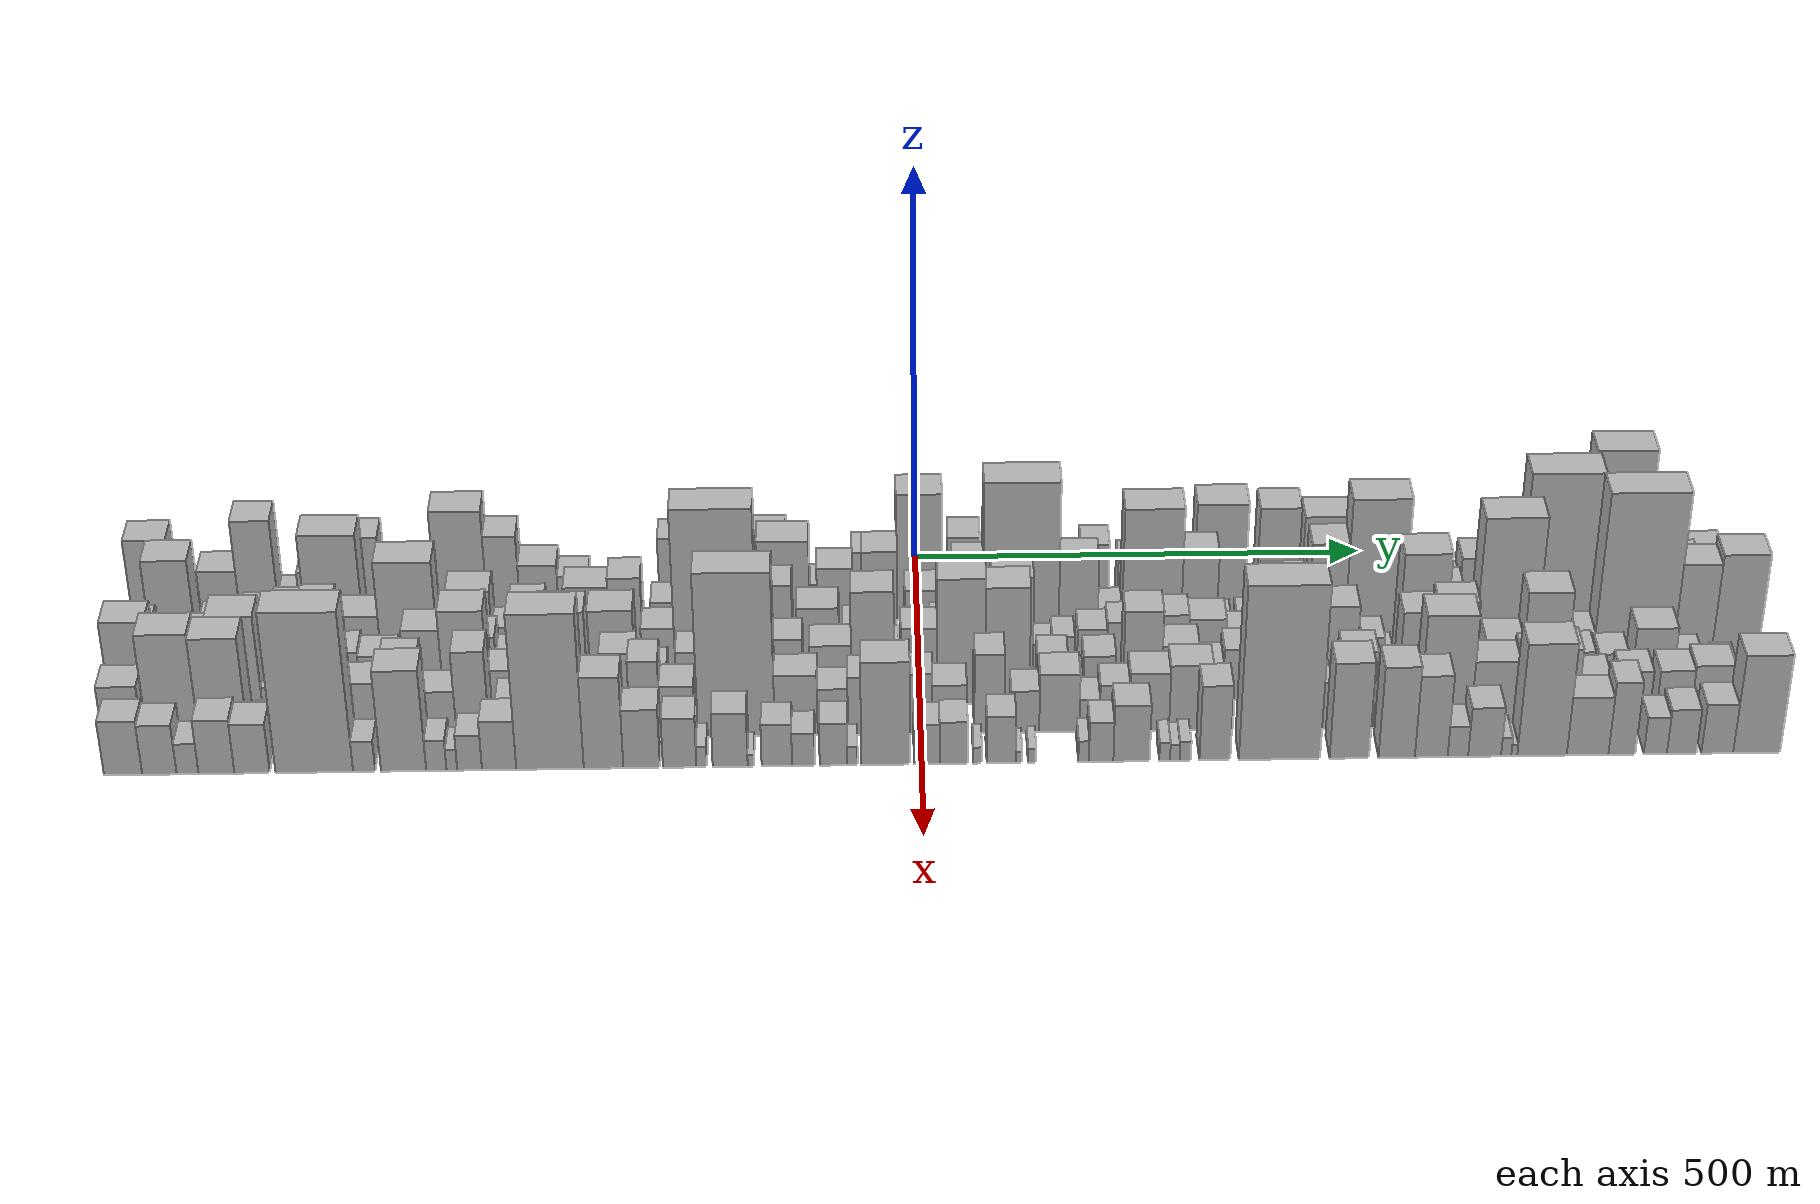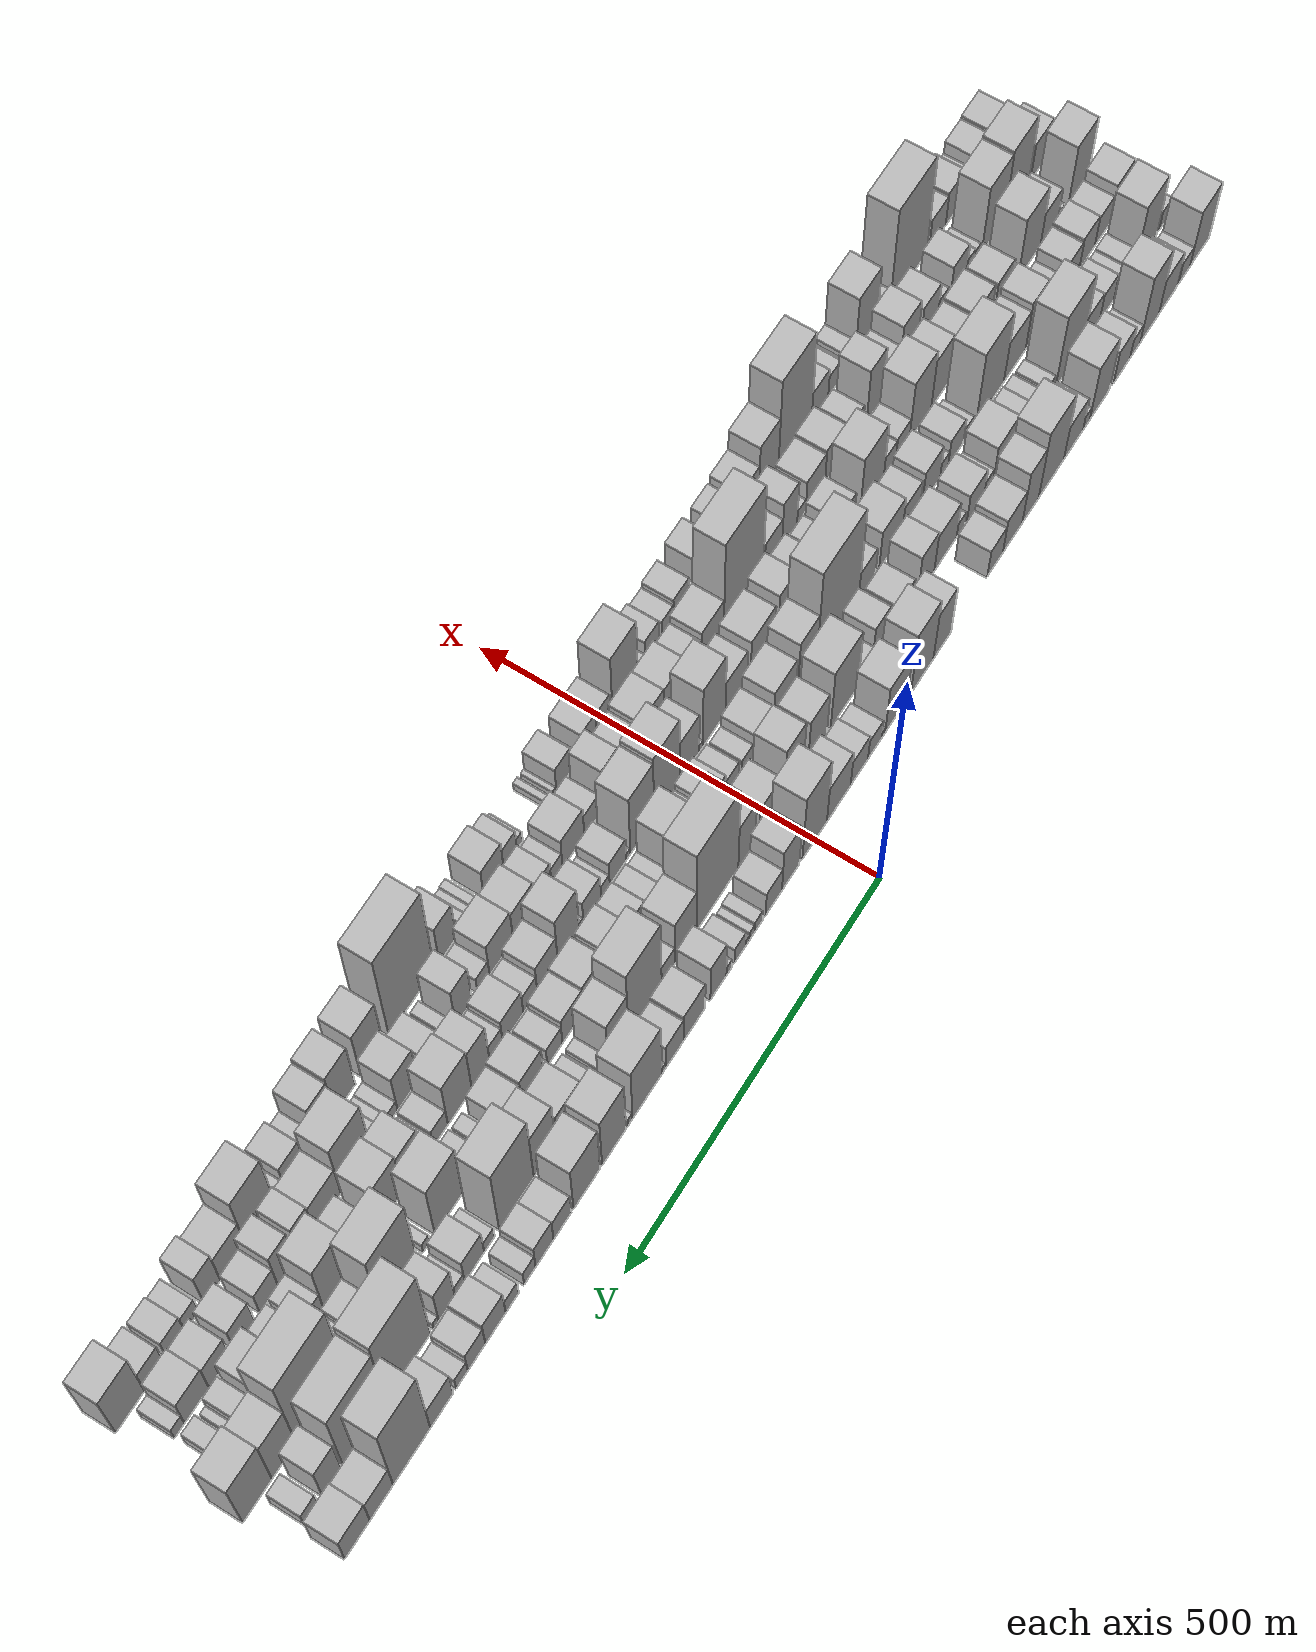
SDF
<sdf version="1.6">
 <world name="default">
  <scene>
   <sky><clouds><speed>12</speed></clouds></sky>
   <ambient>0.4 0.4 0.4 1</ambient>
   <background>0.7 0.7 0.7 1</background>
   <shadows>1</shadows>
  </scene>
  <gravity>0 0 -9.8066</gravity>
  <magnetic_field>6e-06 2.3e-05 -4.2e-05</magnetic_field>
  <physics default="0" name="default_physics" type="ode">
   <ode>
    <solver>
     <type>quick</type>
     <iters>10</iters>
     <sor>1.0</sor>
     <use_dynamic_moi_rescaling>0</use_dynamic_moi_rescaling>
    </solver>
    <constraints>
     <cfm>0</cfm>
     <erp>0.2</erp>
     <contact_max_correcting_vel>100</contact_max_correcting_vel>
     <contact_surface_layer>0.001</contact_surface_layer>
    </constraints>
   </ode>
   <max_step_size>0.004</max_step_size>
   <real_time_factor>1</real_time_factor>
   <real_time_update_rate>250</real_time_update_rate>
  </physics>
  <light name="sun" type="directional">
   <pose>0 0 10 0 0 0</pose>
   <diffuse>0.8 0.8 0.8 1</diffuse>
   <specular>0.2 0.2 0.2 1</specular>
   <attenuation>
    <range>1000</range>
    <constant>0.9</constant>
    <linear>0.01</linear>
    <quadratic>0.001</quadratic>
   </attenuation>
   <direction>-0.5 0.1 -0.9</direction>
  </light>
  <model name="building_1">
   <static>1</static>
   <pose>100.0000 -836.9546 0 0.000000 0.000000 0.000000</pose>
   <link name="link">
    <pose>0 0 58.50 0 0 0</pose>
    <collision name="collision"><geometry><box><size>40.0000 46.0908 117.0000</size></box></geometry></collision>
    <visual name="visual">
     <cast_shadows>0</cast_shadows>
     <geometry><box><size>40.0000 46.0908 117.0000</size></box></geometry>
     <material>
      <script>
       <uri>model://HANNAS_wall/materials/scripts</uri>
       <uri>model://HANNAS_wall/materials/textures</uri>
       <name>vrc/HANNAS_wall</name>
      </script>
     </material>
    </visual>
   </link>
  </model>
  <model name="building_2">
   <static>1</static>
   <pose>100.0000 -800.7105 0 0.000000 0.000000 0.000000</pose>
   <link name="link">
    <pose>0 0 22.50 0 0 0</pose>
    <collision name="collision"><geometry><box><size>40.0000 26.3974 45.0000</size></box></geometry></collision>
    <visual name="visual">
     <cast_shadows>0</cast_shadows>
     <geometry><box><size>40.0000 26.3974 45.0000</size></box></geometry>
     <material>
      <script>
       <uri>model://HANNAS_wall/materials/scripts</uri>
       <uri>model://HANNAS_wall/materials/textures</uri>
       <name>vrc/HANNAS_wall</name>
      </script>
     </material>
    </visual>
   </link>
  </model>
  <model name="building_3">
   <static>1</static>
   <pose>100.0000 -763.3502 0 0.000000 0.000000 0.000000</pose>
   <link name="link">
    <pose>0 0 37.50 0 0 0</pose>
    <collision name="collision"><geometry><box><size>40.0000 42.3233 75.0000</size></box></geometry></collision>
    <visual name="visual">
     <cast_shadows>0</cast_shadows>
     <geometry><box><size>40.0000 42.3233 75.0000</size></box></geometry>
     <material>
      <script>
       <uri>model://HANNAS_wall/materials/scripts</uri>
       <uri>model://HANNAS_wall/materials/textures</uri>
       <name>vrc/HANNAS_wall</name>
      </script>
     </material>
    </visual>
   </link>
  </model>
  <model name="building_4">
   <static>1</static>
   <pose>100.0000 -720.8452 0 0.000000 0.000000 0.000000</pose>
   <link name="link">
    <pose>0 0 70.50 0 0 0</pose>
    <collision name="collision"><geometry><box><size>40.0000 42.6867 141.0000</size></box></geometry></collision>
    <visual name="visual">
     <cast_shadows>0</cast_shadows>
     <geometry><box><size>40.0000 42.6867 141.0000</size></box></geometry>
     <material>
      <script>
       <uri>model://HANNAS_wall/materials/scripts</uri>
       <uri>model://HANNAS_wall/materials/textures</uri>
       <name>vrc/HANNAS_wall</name>
      </script>
     </material>
    </visual>
   </link>
  </model>
  <model name="building_5">
   <static>1</static>
   <pose>100.0000 -687.9397 0 0.000000 0.000000 0.000000</pose>
   <link name="link">
    <pose>0 0 21.00 0 0 0</pose>
    <collision name="collision"><geometry><box><size>40.0000 23.1242 42.0000</size></box></geometry></collision>
    <visual name="visual">
     <cast_shadows>0</cast_shadows>
     <geometry><box><size>40.0000 23.1242 42.0000</size></box></geometry>
     <material>
      <script>
       <uri>model://HANNAS_wall/materials/scripts</uri>
       <uri>model://HANNAS_wall/materials/textures</uri>
       <name>vrc/HANNAS_wall</name>
      </script>
     </material>
    </visual>
   </link>
  </model>
  <model name="building_6">
   <static>1</static>
   <pose>100.0000 -657.6483 0 0.000000 0.000000 0.000000</pose>
   <link name="link">
    <pose>0 0 36.00 0 0 0</pose>
    <collision name="collision"><geometry><box><size>40.0000 37.4587 72.0000</size></box></geometry></collision>
    <visual name="visual">
     <cast_shadows>0</cast_shadows>
     <geometry><box><size>40.0000 37.4587 72.0000</size></box></geometry>
     <material>
      <script>
       <uri>model://HANNAS_wall/materials/scripts</uri>
       <uri>model://HANNAS_wall/materials/textures</uri>
       <name>vrc/HANNAS_wall</name>
      </script>
     </material>
    </visual>
   </link>
  </model>
  <model name="building_7">
   <static>1</static>
   <pose>100.0000 -607.7722 0 0.000000 0.000000 0.000000</pose>
   <link name="link">
    <pose>0 0 58.50 0 0 0</pose>
    <collision name="collision"><geometry><box><size>40.0000 44.2936 117.0000</size></box></geometry></collision>
    <visual name="visual">
     <cast_shadows>0</cast_shadows>
     <geometry><box><size>40.0000 44.2936 117.0000</size></box></geometry>
     <material>
      <script>
       <uri>model://HANNAS_wall/materials/scripts</uri>
       <uri>model://HANNAS_wall/materials/textures</uri>
       <name>vrc/HANNAS_wall</name>
      </script>
     </material>
    </visual>
   </link>
  </model>
  <model name="building_8">
   <static>1</static>
   <pose>100.0000 -578.1136 0 0.000000 0.000000 0.000000</pose>
   <link name="link">
    <pose>0 0 15.00 0 0 0</pose>
    <collision name="collision"><geometry><box><size>40.0000 15.0235 30.0000</size></box></geometry></collision>
    <visual name="visual">
     <cast_shadows>0</cast_shadows>
     <geometry><box><size>40.0000 15.0235 30.0000</size></box></geometry>
     <material>
      <script>
       <uri>model://HANNAS_wall/materials/scripts</uri>
       <uri>model://HANNAS_wall/materials/textures</uri>
       <name>vrc/HANNAS_wall</name>
      </script>
     </material>
    </visual>
   </link>
  </model>
  <model name="building_9">
   <static>1</static>
   <pose>100.0000 -549.1109 0 0.000000 0.000000 0.000000</pose>
   <link name="link">
    <pose>0 0 37.50 0 0 0</pose>
    <collision name="collision"><geometry><box><size>40.0000 42.9820 75.0000</size></box></geometry></collision>
    <visual name="visual">
     <cast_shadows>0</cast_shadows>
     <geometry><box><size>40.0000 42.9820 75.0000</size></box></geometry>
     <material>
      <script>
       <uri>model://HANNAS_wall/materials/scripts</uri>
       <uri>model://HANNAS_wall/materials/textures</uri>
       <name>vrc/HANNAS_wall</name>
      </script>
     </material>
    </visual>
   </link>
  </model>
  <model name="building_10">
   <static>1</static>
   <pose>100.0000 -499.6481 0 0.000000 0.000000 0.000000</pose>
   <link name="link">
    <pose>0 0 75.00 0 0 0</pose>
    <collision name="collision"><geometry><box><size>40.0000 55.9435 150.0000</size></box></geometry></collision>
    <visual name="visual">
     <cast_shadows>0</cast_shadows>
     <geometry><box><size>40.0000 55.9435 150.0000</size></box></geometry>
     <material>
      <script>
       <uri>model://HANNAS_wall/materials/scripts</uri>
       <uri>model://HANNAS_wall/materials/textures</uri>
       <name>vrc/HANNAS_wall</name>
      </script>
     </material>
    </visual>
   </link>
  </model>
  <model name="building_11">
   <static>1</static>
   <pose>100.0000 -453.7469 0 0.000000 0.000000 0.000000</pose>
   <link name="link">
    <pose>0 0 58.50 0 0 0</pose>
    <collision name="collision"><geometry><box><size>40.0000 35.8590 117.0000</size></box></geometry></collision>
    <visual name="visual">
     <cast_shadows>0</cast_shadows>
     <geometry><box><size>40.0000 35.8590 117.0000</size></box></geometry>
     <material>
      <script>
       <uri>model://HANNAS_wall/materials/scripts</uri>
       <uri>model://HANNAS_wall/materials/textures</uri>
       <name>vrc/HANNAS_wall</name>
      </script>
     </material>
    </visual>
   </link>
  </model>
  <model name="building_12">
   <static>1</static>
   <pose>100.0000 -414.7524 0 0.000000 0.000000 0.000000</pose>
   <link name="link">
    <pose>0 0 39.00 0 0 0</pose>
    <collision name="collision"><geometry><box><size>40.0000 42.1300 78.0000</size></box></geometry></collision>
    <visual name="visual">
     <cast_shadows>0</cast_shadows>
     <geometry><box><size>40.0000 42.1300 78.0000</size></box></geometry>
     <material>
      <script>
       <uri>model://HANNAS_wall/materials/scripts</uri>
       <uri>model://HANNAS_wall/materials/textures</uri>
       <name>vrc/HANNAS_wall</name>
      </script>
     </material>
    </visual>
   </link>
  </model>
  <model name="building_13">
   <static>1</static>
   <pose>100.0000 -376.7579 0 0.000000 0.000000 0.000000</pose>
   <link name="link">
    <pose>0 0 31.50 0 0 0</pose>
    <collision name="collision"><geometry><box><size>40.0000 33.8590 63.0000</size></box></geometry></collision>
    <visual name="visual">
     <cast_shadows>0</cast_shadows>
     <geometry><box><size>40.0000 33.8590 63.0000</size></box></geometry>
     <material>
      <script>
       <uri>model://HANNAS_wall/materials/scripts</uri>
       <uri>model://HANNAS_wall/materials/textures</uri>
       <name>vrc/HANNAS_wall</name>
      </script>
     </material>
    </visual>
   </link>
  </model>
  <model name="building_14">
   <static>1</static>
   <pose>100.0000 -263.6347 0 0.000000 0.000000 0.000000</pose>
   <link name="link">
    <pose>0 0 55.50 0 0 0</pose>
    <collision name="collision"><geometry><box><size>40.0000 38.1291 111.0000</size></box></geometry></collision>
    <visual name="visual">
     <cast_shadows>0</cast_shadows>
     <geometry><box><size>40.0000 38.1291 111.0000</size></box></geometry>
     <material>
      <script>
       <uri>model://HANNAS_wall/materials/scripts</uri>
       <uri>model://HANNAS_wall/materials/textures</uri>
       <name>vrc/HANNAS_wall</name>
      </script>
     </material>
    </visual>
   </link>
  </model>
  <model name="building_15">
   <static>1</static>
   <pose>100.0000 -220.7925 0 0.000000 0.000000 0.000000</pose>
   <link name="link">
    <pose>0 0 73.50 0 0 0</pose>
    <collision name="collision"><geometry><box><size>40.0000 47.5555 147.0000</size></box></geometry></collision>
    <visual name="visual">
     <cast_shadows>0</cast_shadows>
     <geometry><box><size>40.0000 47.5555 147.0000</size></box></geometry>
     <material>
      <script>
       <uri>model://HANNAS_wall/materials/scripts</uri>
       <uri>model://HANNAS_wall/materials/textures</uri>
       <name>vrc/HANNAS_wall</name>
      </script>
     </material>
    </visual>
   </link>
  </model>
  <model name="building_16">
   <static>1</static>
   <pose>100.0000 -192.9283 0 0.000000 0.000000 0.000000</pose>
   <link name="link">
    <pose>0 0 9.00 0 0 0</pose>
    <collision name="collision"><geometry><box><size>40.0000 8.1729 18.0000</size></box></geometry></collision>
    <visual name="visual">
     <cast_shadows>0</cast_shadows>
     <geometry><box><size>40.0000 8.1729 18.0000</size></box></geometry>
     <material>
      <script>
       <uri>model://HANNAS_wall/materials/scripts</uri>
       <uri>model://HANNAS_wall/materials/textures</uri>
       <name>vrc/HANNAS_wall</name>
      </script>
     </material>
    </visual>
   </link>
  </model>
  <model name="building_17">
   <static>1</static>
   <pose>100.0000 -166.1689 0 0.000000 0.000000 0.000000</pose>
   <link name="link">
    <pose>0 0 57.00 0 0 0</pose>
    <collision name="collision"><geometry><box><size>40.0000 45.3458 114.0000</size></box></geometry></collision>
    <visual name="visual">
     <cast_shadows>0</cast_shadows>
     <geometry><box><size>40.0000 45.3458 114.0000</size></box></geometry>
     <material>
      <script>
       <uri>model://HANNAS_wall/materials/scripts</uri>
       <uri>model://HANNAS_wall/materials/textures</uri>
       <name>vrc/HANNAS_wall</name>
      </script>
     </material>
    </visual>
   </link>
  </model>
  <model name="building_18">
   <static>1</static>
   <pose>100.0000 -139.8257 0 0.000000 0.000000 0.000000</pose>
   <link name="link">
    <pose>0 0 7.50 0 0 0</pose>
    <collision name="collision"><geometry><box><size>40.0000 7.3405 15.0000</size></box></geometry></collision>
    <visual name="visual">
     <cast_shadows>0</cast_shadows>
     <geometry><box><size>40.0000 7.3405 15.0000</size></box></geometry>
     <material>
      <script>
       <uri>model://HANNAS_wall/materials/scripts</uri>
       <uri>model://HANNAS_wall/materials/textures</uri>
       <name>vrc/HANNAS_wall</name>
      </script>
     </material>
    </visual>
   </link>
  </model>
  <model name="building_19">
   <static>1</static>
   <pose>100.0000 -121.9752 0 0.000000 0.000000 0.000000</pose>
   <link name="link">
    <pose>0 0 24.00 0 0 0</pose>
    <collision name="collision"><geometry><box><size>40.0000 28.3605 48.0000</size></box></geometry></collision>
    <visual name="visual">
     <cast_shadows>0</cast_shadows>
     <geometry><box><size>40.0000 28.3605 48.0000</size></box></geometry>
     <material>
      <script>
       <uri>model://HANNAS_wall/materials/scripts</uri>
       <uri>model://HANNAS_wall/materials/textures</uri>
       <name>vrc/HANNAS_wall</name>
      </script>
     </material>
    </visual>
   </link>
  </model>
  <model name="building_20">
   <static>1</static>
   <pose>100.0000 -89.8973 0 0.000000 0.000000 0.000000</pose>
   <link name="link">
    <pose>0 0 31.50 0 0 0</pose>
    <collision name="collision"><geometry><box><size>40.0000 35.7953 63.0000</size></box></geometry></collision>
    <visual name="visual">
     <cast_shadows>0</cast_shadows>
     <geometry><box><size>40.0000 35.7953 63.0000</size></box></geometry>
     <material>
      <script>
       <uri>model://HANNAS_wall/materials/scripts</uri>
       <uri>model://HANNAS_wall/materials/textures</uri>
       <name>vrc/HANNAS_wall</name>
      </script>
     </material>
    </visual>
   </link>
  </model>
  <model name="building_21">
   <static>1</static>
   <pose>100.0000 -47.6946 0 0.000000 0.000000 0.000000</pose>
   <link name="link">
    <pose>0 0 45.00 0 0 0</pose>
    <collision name="collision"><geometry><box><size>40.0000 48.6101 90.0000</size></box></geometry></collision>
    <visual name="visual">
     <cast_shadows>0</cast_shadows>
     <geometry><box><size>40.0000 48.6101 90.0000</size></box></geometry>
     <material>
      <script>
       <uri>model://HANNAS_wall/materials/scripts</uri>
       <uri>model://HANNAS_wall/materials/textures</uri>
       <name>vrc/HANNAS_wall</name>
      </script>
     </material>
    </visual>
   </link>
  </model>
  <model name="building_22">
   <static>1</static>
   <pose>100.0000 1.5828 0 0.000000 0.000000 0.000000</pose>
   <link name="link">
    <pose>0 0 82.50 0 0 0</pose>
    <collision name="collision"><geometry><box><size>40.0000 49.9448 165.0000</size></box></geometry></collision>
    <visual name="visual">
     <cast_shadows>0</cast_shadows>
     <geometry><box><size>40.0000 49.9448 165.0000</size></box></geometry>
     <material>
      <script>
       <uri>model://HANNAS_wall/materials/scripts</uri>
       <uri>model://HANNAS_wall/materials/textures</uri>
       <name>vrc/HANNAS_wall</name>
      </script>
     </material>
    </visual>
   </link>
  </model>
  <model name="building_23">
   <static>1</static>
   <pose>100.0000 50.1426 0 0.000000 0.000000 0.000000</pose>
   <link name="link">
    <pose>0 0 54.00 0 0 0</pose>
    <collision name="collision"><geometry><box><size>40.0000 35.1748 108.0000</size></box></geometry></collision>
    <visual name="visual">
     <cast_shadows>0</cast_shadows>
     <geometry><box><size>40.0000 35.1748 108.0000</size></box></geometry>
     <material>
      <script>
       <uri>model://HANNAS_wall/materials/scripts</uri>
       <uri>model://HANNAS_wall/materials/textures</uri>
       <name>vrc/HANNAS_wall</name>
      </script>
     </material>
    </visual>
   </link>
  </model>
  <model name="building_24">
   <static>1</static>
   <pose>100.0000 84.0728 0 0.000000 0.000000 0.000000</pose>
   <link name="link">
    <pose>0 0 31.50 0 0 0</pose>
    <collision name="collision"><geometry><box><size>40.0000 32.6855 63.0000</size></box></geometry></collision>
    <visual name="visual">
     <cast_shadows>0</cast_shadows>
     <geometry><box><size>40.0000 32.6855 63.0000</size></box></geometry>
     <material>
      <script>
       <uri>model://HANNAS_wall/materials/scripts</uri>
       <uri>model://HANNAS_wall/materials/textures</uri>
       <name>vrc/HANNAS_wall</name>
      </script>
     </material>
    </visual>
   </link>
  </model>
  <model name="building_25">
   <static>1</static>
   <pose>100.0000 114.4004 0 0.000000 0.000000 0.000000</pose>
   <link name="link">
    <pose>0 0 15.00 0 0 0</pose>
    <collision name="collision"><geometry><box><size>40.0000 15.9697 30.0000</size></box></geometry></collision>
    <visual name="visual">
     <cast_shadows>0</cast_shadows>
     <geometry><box><size>40.0000 15.9697 30.0000</size></box></geometry>
     <material>
      <script>
       <uri>model://HANNAS_wall/materials/scripts</uri>
       <uri>model://HANNAS_wall/materials/textures</uri>
       <name>vrc/HANNAS_wall</name>
      </script>
     </material>
    </visual>
   </link>
  </model>
  <model name="building_26">
   <static>1</static>
   <pose>100.0000 127.3732 0 0.000000 0.000000 0.000000</pose>
   <link name="link">
    <pose>0 0 12.00 0 0 0</pose>
    <collision name="collision"><geometry><box><size>40.0000 9.9760 24.0000</size></box></geometry></collision>
    <visual name="visual">
     <cast_shadows>0</cast_shadows>
     <geometry><box><size>40.0000 9.9760 24.0000</size></box></geometry>
     <material>
      <script>
       <uri>model://HANNAS_wall/materials/scripts</uri>
       <uri>model://HANNAS_wall/materials/textures</uri>
       <name>vrc/HANNAS_wall</name>
      </script>
     </material>
    </visual>
   </link>
  </model>
  <model name="building_27">
   <static>1</static>
   <pose>100.0000 136.0910 0 0.000000 0.000000 0.000000</pose>
   <link name="link">
    <pose>0 0 7.50 0 0 0</pose>
    <collision name="collision"><geometry><box><size>40.0000 7.4596 15.0000</size></box></geometry></collision>
    <visual name="visual">
     <cast_shadows>0</cast_shadows>
     <geometry><box><size>40.0000 7.4596 15.0000</size></box></geometry>
     <material>
      <script>
       <uri>model://HANNAS_wall/materials/scripts</uri>
       <uri>model://HANNAS_wall/materials/textures</uri>
       <name>vrc/HANNAS_wall</name>
      </script>
     </material>
    </visual>
   </link>
  </model>
  <model name="building_28">
   <static>1</static>
   <pose>100.0000 150.8315 0 0.000000 0.000000 0.000000</pose>
   <link name="link">
    <pose>0 0 21.00 0 0 0</pose>
    <collision name="collision"><geometry><box><size>40.0000 22.0215 42.0000</size></box></geometry></collision>
    <visual name="visual">
     <cast_shadows>0</cast_shadows>
     <geometry><box><size>40.0000 22.0215 42.0000</size></box></geometry>
     <material>
      <script>
       <uri>model://HANNAS_wall/materials/scripts</uri>
       <uri>model://HANNAS_wall/materials/textures</uri>
       <name>vrc/HANNAS_wall</name>
      </script>
     </material>
    </visual>
   </link>
  </model>
  <model name="building_29">
   <static>1</static>
   <pose>100.0000 172.4460 0 0.000000 0.000000 0.000000</pose>
   <link name="link">
    <pose>0 0 12.00 0 0 0</pose>
    <collision name="collision"><geometry><box><size>40.0000 11.2074 24.0000</size></box></geometry></collision>
    <visual name="visual">
     <cast_shadows>0</cast_shadows>
     <geometry><box><size>40.0000 11.2074 24.0000</size></box></geometry>
     <material>
      <script>
       <uri>model://HANNAS_wall/materials/scripts</uri>
       <uri>model://HANNAS_wall/materials/textures</uri>
       <name>vrc/HANNAS_wall</name>
      </script>
     </material>
    </visual>
   </link>
  </model>
  <model name="building_30">
   <static>1</static>
   <pose>100.0000 193.8048 0 0.000000 0.000000 0.000000</pose>
   <link name="link">
    <pose>0 0 48.00 0 0 0</pose>
    <collision name="collision"><geometry><box><size>40.0000 31.5103 96.0000</size></box></geometry></collision>
    <visual name="visual">
     <cast_shadows>0</cast_shadows>
     <geometry><box><size>40.0000 31.5103 96.0000</size></box></geometry>
     <material>
      <script>
       <uri>model://HANNAS_wall/materials/scripts</uri>
       <uri>model://HANNAS_wall/materials/textures</uri>
       <name>vrc/HANNAS_wall</name>
      </script>
     </material>
    </visual>
   </link>
  </model>
  <model name="building_31">
   <static>1</static>
   <pose>100.0000 240.4752 0 0.000000 0.000000 0.000000</pose>
   <link name="link">
    <pose>0 0 37.50 0 0 0</pose>
    <collision name="collision"><geometry><box><size>40.0000 41.8304 75.0000</size></box></geometry></collision>
    <visual name="visual">
     <cast_shadows>0</cast_shadows>
     <geometry><box><size>40.0000 41.8304 75.0000</size></box></geometry>
     <material>
      <script>
       <uri>model://HANNAS_wall/materials/scripts</uri>
       <uri>model://HANNAS_wall/materials/textures</uri>
       <name>vrc/HANNAS_wall</name>
      </script>
     </material>
    </visual>
   </link>
  </model>
  <model name="building_32">
   <static>1</static>
   <pose>100.0000 278.7799 0 0.000000 0.000000 0.000000</pose>
   <link name="link">
    <pose>0 0 33.00 0 0 0</pose>
    <collision name="collision"><geometry><box><size>40.0000 34.7790 66.0000</size></box></geometry></collision>
    <visual name="visual">
     <cast_shadows>0</cast_shadows>
     <geometry><box><size>40.0000 34.7790 66.0000</size></box></geometry>
     <material>
      <script>
       <uri>model://HANNAS_wall/materials/scripts</uri>
       <uri>model://HANNAS_wall/materials/textures</uri>
       <name>vrc/HANNAS_wall</name>
      </script>
     </material>
    </visual>
   </link>
  </model>
  <model name="building_33">
   <static>1</static>
   <pose>100.0000 299.8718 0 0.000000 0.000000 0.000000</pose>
   <link name="link">
    <pose>0 0 9.00 0 0 0</pose>
    <collision name="collision"><geometry><box><size>40.0000 7.4049 18.0000</size></box></geometry></collision>
    <visual name="visual">
     <cast_shadows>0</cast_shadows>
     <geometry><box><size>40.0000 7.4049 18.0000</size></box></geometry>
     <material>
      <script>
       <uri>model://HANNAS_wall/materials/scripts</uri>
       <uri>model://HANNAS_wall/materials/textures</uri>
       <name>vrc/HANNAS_wall</name>
      </script>
     </material>
    </visual>
   </link>
  </model>
  <model name="building_34">
   <static>1</static>
   <pose>100.0000 331.7933 0 0.000000 0.000000 0.000000</pose>
   <link name="link">
    <pose>0 0 73.50 0 0 0</pose>
    <collision name="collision"><geometry><box><size>40.0000 56.4381 147.0000</size></box></geometry></collision>
    <visual name="visual">
     <cast_shadows>0</cast_shadows>
     <geometry><box><size>40.0000 56.4381 147.0000</size></box></geometry>
     <material>
      <script>
       <uri>model://HANNAS_wall/materials/scripts</uri>
       <uri>model://HANNAS_wall/materials/textures</uri>
       <name>vrc/HANNAS_wall</name>
      </script>
     </material>
    </visual>
   </link>
  </model>
  <model name="building_35">
   <static>1</static>
   <pose>100.0000 364.6440 0 0.000000 0.000000 0.000000</pose>
   <link name="link">
    <pose>0 0 10.50 0 0 0</pose>
    <collision name="collision"><geometry><box><size>40.0000 9.2634 21.0000</size></box></geometry></collision>
    <visual name="visual">
     <cast_shadows>0</cast_shadows>
     <geometry><box><size>40.0000 9.2634 21.0000</size></box></geometry>
     <material>
      <script>
       <uri>model://HANNAS_wall/materials/scripts</uri>
       <uri>model://HANNAS_wall/materials/textures</uri>
       <name>vrc/HANNAS_wall</name>
      </script>
     </material>
    </visual>
   </link>
  </model>
  <model name="building_36">
   <static>1</static>
   <pose>100.0000 394.9189 0 0.000000 0.000000 0.000000</pose>
   <link name="link">
    <pose>0 0 70.50 0 0 0</pose>
    <collision name="collision"><geometry><box><size>40.0000 45.2863 141.0000</size></box></geometry></collision>
    <visual name="visual">
     <cast_shadows>0</cast_shadows>
     <geometry><box><size>40.0000 45.2863 141.0000</size></box></geometry>
     <material>
      <script>
       <uri>model://HANNAS_wall/materials/scripts</uri>
       <uri>model://HANNAS_wall/materials/textures</uri>
       <name>vrc/HANNAS_wall</name>
      </script>
     </material>
    </visual>
   </link>
  </model>
  <model name="building_37">
   <static>1</static>
   <pose>100.0000 446.4588 0 0.000000 0.000000 0.000000</pose>
   <link name="link">
    <pose>0 0 64.50 0 0 0</pose>
    <collision name="collision"><geometry><box><size>40.0000 49.7935 129.0000</size></box></geometry></collision>
    <visual name="visual">
     <cast_shadows>0</cast_shadows>
     <geometry><box><size>40.0000 49.7935 129.0000</size></box></geometry>
     <material>
      <script>
       <uri>model://HANNAS_wall/materials/scripts</uri>
       <uri>model://HANNAS_wall/materials/textures</uri>
       <name>vrc/HANNAS_wall</name>
      </script>
     </material>
    </visual>
   </link>
  </model>
  <model name="building_38">
   <static>1</static>
   <pose>100.0000 491.9619 0 0.000000 0.000000 0.000000</pose>
   <link name="link">
    <pose>0 0 30.00 0 0 0</pose>
    <collision name="collision"><geometry><box><size>40.0000 33.2126 60.0000</size></box></geometry></collision>
    <visual name="visual">
     <cast_shadows>0</cast_shadows>
     <geometry><box><size>40.0000 33.2126 60.0000</size></box></geometry>
     <material>
      <script>
       <uri>model://HANNAS_wall/materials/scripts</uri>
       <uri>model://HANNAS_wall/materials/textures</uri>
       <name>vrc/HANNAS_wall</name>
      </script>
     </material>
    </visual>
   </link>
  </model>
  <model name="building_39">
   <static>1</static>
   <pose>100.0000 525.1306 0 0.000000 0.000000 0.000000</pose>
   <link name="link">
    <pose>0 0 33.00 0 0 0</pose>
    <collision name="collision"><geometry><box><size>40.0000 33.1248 66.0000</size></box></geometry></collision>
    <visual name="visual">
     <cast_shadows>0</cast_shadows>
     <geometry><box><size>40.0000 33.1248 66.0000</size></box></geometry>
     <material>
      <script>
       <uri>model://HANNAS_wall/materials/scripts</uri>
       <uri>model://HANNAS_wall/materials/textures</uri>
       <name>vrc/HANNAS_wall</name>
      </script>
     </material>
    </visual>
   </link>
  </model>
  <model name="building_40">
   <static>1</static>
   <pose>100.0000 552.2777 0 0.000000 0.000000 0.000000</pose>
   <link name="link">
    <pose>0 0 21.00 0 0 0</pose>
    <collision name="collision"><geometry><box><size>40.0000 21.1694 42.0000</size></box></geometry></collision>
    <visual name="visual">
     <cast_shadows>0</cast_shadows>
     <geometry><box><size>40.0000 21.1694 42.0000</size></box></geometry>
     <material>
      <script>
       <uri>model://HANNAS_wall/materials/scripts</uri>
       <uri>model://HANNAS_wall/materials/textures</uri>
       <name>vrc/HANNAS_wall</name>
      </script>
     </material>
    </visual>
   </link>
  </model>
  <model name="building_41">
   <static>1</static>
   <pose>100.0000 584.7728 0 0.000000 0.000000 0.000000</pose>
   <link name="link">
    <pose>0 0 21.00 0 0 0</pose>
    <collision name="collision"><geometry><box><size>40.0000 23.8207 42.0000</size></box></geometry></collision>
    <visual name="visual">
     <cast_shadows>0</cast_shadows>
     <geometry><box><size>40.0000 23.8207 42.0000</size></box></geometry>
     <material>
      <script>
       <uri>model://HANNAS_wall/materials/scripts</uri>
       <uri>model://HANNAS_wall/materials/textures</uri>
       <name>vrc/HANNAS_wall</name>
      </script>
     </material>
    </visual>
   </link>
  </model>
  <model name="building_42">
   <static>1</static>
   <pose>100.0000 615.1930 0 0.000000 0.000000 0.000000</pose>
   <link name="link">
    <pose>0 0 36.00 0 0 0</pose>
    <collision name="collision"><geometry><box><size>40.0000 37.0197 72.0000</size></box></geometry></collision>
    <visual name="visual">
     <cast_shadows>0</cast_shadows>
     <geometry><box><size>40.0000 37.0197 72.0000</size></box></geometry>
     <material>
      <script>
       <uri>model://HANNAS_wall/materials/scripts</uri>
       <uri>model://HANNAS_wall/materials/textures</uri>
       <name>vrc/HANNAS_wall</name>
      </script>
     </material>
    </visual>
   </link>
  </model>
  <model name="building_43">
   <static>1</static>
   <pose>100.0000 649.6365 0 0.000000 0.000000 0.000000</pose>
   <link name="link">
    <pose>0 0 30.00 0 0 0</pose>
    <collision name="collision"><geometry><box><size>40.0000 31.8674 60.0000</size></box></geometry></collision>
    <visual name="visual">
     <cast_shadows>0</cast_shadows>
     <geometry><box><size>40.0000 31.8674 60.0000</size></box></geometry>
     <material>
      <script>
       <uri>model://HANNAS_wall/materials/scripts</uri>
       <uri>model://HANNAS_wall/materials/textures</uri>
       <name>vrc/HANNAS_wall</name>
      </script>
     </material>
    </visual>
   </link>
  </model>
  <model name="building_44">
   <static>1</static>
   <pose>100.0000 676.1484 0 0.000000 0.000000 0.000000</pose>
   <link name="link">
    <pose>0 0 18.00 0 0 0</pose>
    <collision name="collision"><geometry><box><size>40.0000 21.1563 36.0000</size></box></geometry></collision>
    <visual name="visual">
     <cast_shadows>0</cast_shadows>
     <geometry><box><size>40.0000 21.1563 36.0000</size></box></geometry>
     <material>
      <script>
       <uri>model://HANNAS_wall/materials/scripts</uri>
       <uri>model://HANNAS_wall/materials/textures</uri>
       <name>vrc/HANNAS_wall</name>
      </script>
     </material>
    </visual>
   </link>
  </model>
  <model name="building_45">
   <static>1</static>
   <pose>100.0000 712.2289 0 0.000000 0.000000 0.000000</pose>
   <link name="link">
    <pose>0 0 36.00 0 0 0</pose>
    <collision name="collision"><geometry><box><size>40.0000 41.0048 72.0000</size></box></geometry></collision>
    <visual name="visual">
     <cast_shadows>0</cast_shadows>
     <geometry><box><size>40.0000 41.0048 72.0000</size></box></geometry>
     <material>
      <script>
       <uri>model://HANNAS_wall/materials/scripts</uri>
       <uri>model://HANNAS_wall/materials/textures</uri>
       <name>vrc/HANNAS_wall</name>
      </script>
     </material>
    </visual>
   </link>
  </model>
  <model name="building_46">
   <static>1</static>
   <pose>100.0000 765.6833 0 0.000000 0.000000 0.000000</pose>
   <link name="link">
    <pose>0 0 105.00 0 0 0</pose>
    <collision name="collision"><geometry><box><size>40.0000 65.9039 210.0000</size></box></geometry></collision>
    <visual name="visual">
     <cast_shadows>0</cast_shadows>
     <geometry><box><size>40.0000 65.9039 210.0000</size></box></geometry>
     <material>
      <script>
       <uri>model://HANNAS_wall/materials/scripts</uri>
       <uri>model://HANNAS_wall/materials/textures</uri>
       <name>vrc/HANNAS_wall</name>
      </script>
     </material>
    </visual>
   </link>
  </model>
  <model name="building_47">
   <static>1</static>
   <pose>100.0000 819.1028 0 0.000000 0.000000 0.000000</pose>
   <link name="link">
    <pose>0 0 36.00 0 0 0</pose>
    <collision name="collision"><geometry><box><size>40.0000 40.9353 72.0000</size></box></geometry></collision>
    <visual name="visual">
     <cast_shadows>0</cast_shadows>
     <geometry><box><size>40.0000 40.9353 72.0000</size></box></geometry>
     <material>
      <script>
       <uri>model://HANNAS_wall/materials/scripts</uri>
       <uri>model://HANNAS_wall/materials/textures</uri>
       <name>vrc/HANNAS_wall</name>
      </script>
     </material>
    </visual>
   </link>
  </model>
  <model name="building_48">
   <static>1</static>
   <pose>100.0000 861.5395 0 0.000000 0.000000 0.000000</pose>
   <link name="link">
    <pose>0 0 39.00 0 0 0</pose>
    <collision name="collision"><geometry><box><size>40.0000 43.9381 78.0000</size></box></geometry></collision>
    <visual name="visual">
     <cast_shadows>0</cast_shadows>
     <geometry><box><size>40.0000 43.9381 78.0000</size></box></geometry>
     <material>
      <script>
       <uri>model://HANNAS_wall/materials/scripts</uri>
       <uri>model://HANNAS_wall/materials/textures</uri>
       <name>vrc/HANNAS_wall</name>
      </script>
     </material>
    </visual>
   </link>
  </model>
  <model name="building_49">
   <static>1</static>
   <pose>152.0000 -848.3407 0 0.000000 0.000000 0.000000</pose>
   <link name="link">
    <pose>0 0 21.00 0 0 0</pose>
    <collision name="collision"><geometry><box><size>40.0000 23.3186 42.0000</size></box></geometry></collision>
    <visual name="visual">
     <cast_shadows>0</cast_shadows>
     <geometry><box><size>40.0000 23.3186 42.0000</size></box></geometry>
     <material>
      <script>
       <uri>model://HANNAS_wall/materials/scripts</uri>
       <uri>model://HANNAS_wall/materials/textures</uri>
       <name>vrc/HANNAS_wall</name>
      </script>
     </material>
    </visual>
   </link>
  </model>
  <model name="building_50">
   <static>1</static>
   <pose>152.0000 -806.9948 0 0.000000 0.000000 0.000000</pose>
   <link name="link">
    <pose>0 0 63.00 0 0 0</pose>
    <collision name="collision"><geometry><box><size>40.0000 49.3733 126.0000</size></box></geometry></collision>
    <visual name="visual">
     <cast_shadows>0</cast_shadows>
     <geometry><box><size>40.0000 49.3733 126.0000</size></box></geometry>
     <material>
      <script>
       <uri>model://HANNAS_wall/materials/scripts</uri>
       <uri>model://HANNAS_wall/materials/textures</uri>
       <name>vrc/HANNAS_wall</name>
      </script>
     </material>
    </visual>
   </link>
  </model>
  <model name="building_51">
   <static>1</static>
   <pose>152.0000 -766.2804 0 0.000000 0.000000 0.000000</pose>
   <link name="link">
    <pose>0 0 22.50 0 0 0</pose>
    <collision name="collision"><geometry><box><size>40.0000 24.0554 45.0000</size></box></geometry></collision>
    <visual name="visual">
     <cast_shadows>0</cast_shadows>
     <geometry><box><size>40.0000 24.0554 45.0000</size></box></geometry>
     <material>
      <script>
       <uri>model://HANNAS_wall/materials/scripts</uri>
       <uri>model://HANNAS_wall/materials/textures</uri>
       <name>vrc/HANNAS_wall</name>
      </script>
     </material>
    </visual>
   </link>
  </model>
  <model name="building_52">
   <static>1</static>
   <pose>152.0000 -743.5735 0 0.000000 0.000000 0.000000</pose>
   <link name="link">
    <pose>0 0 21.00 0 0 0</pose>
    <collision name="collision"><geometry><box><size>40.0000 21.3583 42.0000</size></box></geometry></collision>
    <visual name="visual">
     <cast_shadows>0</cast_shadows>
     <geometry><box><size>40.0000 21.3583 42.0000</size></box></geometry>
     <material>
      <script>
       <uri>model://HANNAS_wall/materials/scripts</uri>
       <uri>model://HANNAS_wall/materials/textures</uri>
       <name>vrc/HANNAS_wall</name>
      </script>
     </material>
    </visual>
   </link>
  </model>
  <model name="building_53">
   <static>1</static>
   <pose>152.0000 -716.4333 0 0.000000 0.000000 0.000000</pose>
   <link name="link">
    <pose>0 0 28.50 0 0 0</pose>
    <collision name="collision"><geometry><box><size>40.0000 32.9222 57.0000</size></box></geometry></collision>
    <visual name="visual">
     <cast_shadows>0</cast_shadows>
     <geometry><box><size>40.0000 32.9222 57.0000</size></box></geometry>
     <material>
      <script>
       <uri>model://HANNAS_wall/materials/scripts</uri>
       <uri>model://HANNAS_wall/materials/textures</uri>
       <name>vrc/HANNAS_wall</name>
      </script>
     </material>
    </visual>
   </link>
  </model>
  <model name="building_54">
   <static>1</static>
   <pose>152.0000 -681.1485 0 0.000000 0.000000 0.000000</pose>
   <link name="link">
    <pose>0 0 31.50 0 0 0</pose>
    <collision name="collision"><geometry><box><size>40.0000 37.6475 63.0000</size></box></geometry></collision>
    <visual name="visual">
     <cast_shadows>0</cast_shadows>
     <geometry><box><size>40.0000 37.6475 63.0000</size></box></geometry>
     <material>
      <script>
       <uri>model://HANNAS_wall/materials/scripts</uri>
       <uri>model://HANNAS_wall/materials/textures</uri>
       <name>vrc/HANNAS_wall</name>
      </script>
     </material>
    </visual>
   </link>
  </model>
  <model name="building_55">
   <static>1</static>
   <pose>152.0000 -631.4597 0 0.000000 0.000000 0.000000</pose>
   <link name="link">
    <pose>0 0 78.00 0 0 0</pose>
    <collision name="collision"><geometry><box><size>40.0000 61.7300 156.0000</size></box></geometry></collision>
    <visual name="visual">
     <cast_shadows>0</cast_shadows>
     <geometry><box><size>40.0000 61.7300 156.0000</size></box></geometry>
     <material>
      <script>
       <uri>model://HANNAS_wall/materials/scripts</uri>
       <uri>model://HANNAS_wall/materials/textures</uri>
       <name>vrc/HANNAS_wall</name>
      </script>
     </material>
    </visual>
   </link>
  </model>
  <model name="building_56">
   <static>1</static>
   <pose>152.0000 -587.0116 0 0.000000 0.000000 0.000000</pose>
   <link name="link">
    <pose>0 0 18.00 0 0 0</pose>
    <collision name="collision"><geometry><box><size>40.0000 19.1662 36.0000</size></box></geometry></collision>
    <visual name="visual">
     <cast_shadows>0</cast_shadows>
     <geometry><box><size>40.0000 19.1662 36.0000</size></box></geometry>
     <material>
      <script>
       <uri>model://HANNAS_wall/materials/scripts</uri>
       <uri>model://HANNAS_wall/materials/textures</uri>
       <name>vrc/HANNAS_wall</name>
      </script>
     </material>
    </visual>
   </link>
  </model>
  <model name="building_57">
   <static>1</static>
   <pose>152.0000 -559.1922 0 0.000000 0.000000 0.000000</pose>
   <link name="link">
    <pose>0 0 21.00 0 0 0</pose>
    <collision name="collision"><geometry><box><size>40.0000 22.4726 42.0000</size></box></geometry></collision>
    <visual name="visual">
     <cast_shadows>0</cast_shadows>
     <geometry><box><size>40.0000 22.4726 42.0000</size></box></geometry>
     <material>
      <script>
       <uri>model://HANNAS_wall/materials/scripts</uri>
       <uri>model://HANNAS_wall/materials/textures</uri>
       <name>vrc/HANNAS_wall</name>
      </script>
     </material>
    </visual>
   </link>
  </model>
  <model name="building_58">
   <static>1</static>
   <pose>152.0000 -533.6218 0 0.000000 0.000000 0.000000</pose>
   <link name="link">
    <pose>0 0 24.00 0 0 0</pose>
    <collision name="collision"><geometry><box><size>40.0000 28.6683 48.0000</size></box></geometry></collision>
    <visual name="visual">
     <cast_shadows>0</cast_shadows>
     <geometry><box><size>40.0000 28.6683 48.0000</size></box></geometry>
     <material>
      <script>
       <uri>model://HANNAS_wall/materials/scripts</uri>
       <uri>model://HANNAS_wall/materials/textures</uri>
       <name>vrc/HANNAS_wall</name>
      </script>
     </material>
    </visual>
   </link>
  </model>
  <model name="building_59">
   <static>1</static>
   <pose>152.0000 -486.4755 0 0.000000 0.000000 0.000000</pose>
   <link name="link">
    <pose>0 0 40.50 0 0 0</pose>
    <collision name="collision"><geometry><box><size>40.0000 47.6243 81.0000</size></box></geometry></collision>
    <visual name="visual">
     <cast_shadows>0</cast_shadows>
     <geometry><box><size>40.0000 47.6243 81.0000</size></box></geometry>
     <material>
      <script>
       <uri>model://HANNAS_wall/materials/scripts</uri>
       <uri>model://HANNAS_wall/materials/textures</uri>
       <name>vrc/HANNAS_wall</name>
      </script>
     </material>
    </visual>
   </link>
  </model>
  <model name="building_60">
   <static>1</static>
   <pose>152.0000 -452.9226 0 0.000000 0.000000 0.000000</pose>
   <link name="link">
    <pose>0 0 16.50 0 0 0</pose>
    <collision name="collision"><geometry><box><size>40.0000 19.4815 33.0000</size></box></geometry></collision>
    <visual name="visual">
     <cast_shadows>0</cast_shadows>
     <geometry><box><size>40.0000 19.4815 33.0000</size></box></geometry>
     <material>
      <script>
       <uri>model://HANNAS_wall/materials/scripts</uri>
       <uri>model://HANNAS_wall/materials/textures</uri>
       <name>vrc/HANNAS_wall</name>
      </script>
     </material>
    </visual>
   </link>
  </model>
  <model name="building_61">
   <static>1</static>
   <pose>152.0000 -424.2948 0 0.000000 0.000000 0.000000</pose>
   <link name="link">
    <pose>0 0 31.50 0 0 0</pose>
    <collision name="collision"><geometry><box><size>40.0000 37.7740 63.0000</size></box></geometry></collision>
    <visual name="visual">
     <cast_shadows>0</cast_shadows>
     <geometry><box><size>40.0000 37.7740 63.0000</size></box></geometry>
     <material>
      <script>
       <uri>model://HANNAS_wall/materials/scripts</uri>
       <uri>model://HANNAS_wall/materials/textures</uri>
       <name>vrc/HANNAS_wall</name>
      </script>
     </material>
    </visual>
   </link>
  </model>
  <model name="building_62">
   <static>1</static>
   <pose>152.0000 -392.3795 0 0.000000 0.000000 0.000000</pose>
   <link name="link">
    <pose>0 0 16.50 0 0 0</pose>
    <collision name="collision"><geometry><box><size>40.0000 18.0567 33.0000</size></box></geometry></collision>
    <visual name="visual">
     <cast_shadows>0</cast_shadows>
     <geometry><box><size>40.0000 18.0567 33.0000</size></box></geometry>
     <material>
      <script>
       <uri>model://HANNAS_wall/materials/scripts</uri>
       <uri>model://HANNAS_wall/materials/textures</uri>
       <name>vrc/HANNAS_wall</name>
      </script>
     </material>
    </visual>
   </link>
  </model>
  <model name="building_63">
   <static>1</static>
   <pose>152.0000 -359.3087 0 0.000000 0.000000 0.000000</pose>
   <link name="link">
    <pose>0 0 42.00 0 0 0</pose>
    <collision name="collision"><geometry><box><size>40.0000 48.0849 84.0000</size></box></geometry></collision>
    <visual name="visual">
     <cast_shadows>0</cast_shadows>
     <geometry><box><size>40.0000 48.0849 84.0000</size></box></geometry>
     <material>
      <script>
       <uri>model://HANNAS_wall/materials/scripts</uri>
       <uri>model://HANNAS_wall/materials/textures</uri>
       <name>vrc/HANNAS_wall</name>
      </script>
     </material>
    </visual>
   </link>
  </model>
  <model name="building_64">
   <static>1</static>
   <pose>152.0000 -317.4862 0 0.000000 0.000000 0.000000</pose>
   <link name="link">
    <pose>0 0 48.00 0 0 0</pose>
    <collision name="collision"><geometry><box><size>40.0000 35.5601 96.0000</size></box></geometry></collision>
    <visual name="visual">
     <cast_shadows>0</cast_shadows>
     <geometry><box><size>40.0000 35.5601 96.0000</size></box></geometry>
     <material>
      <script>
       <uri>model://HANNAS_wall/materials/scripts</uri>
       <uri>model://HANNAS_wall/materials/textures</uri>
       <name>vrc/HANNAS_wall</name>
      </script>
     </material>
    </visual>
   </link>
  </model>
  <model name="building_65">
   <static>1</static>
   <pose>152.0000 -270.8084 0 0.000000 0.000000 0.000000</pose>
   <link name="link">
    <pose>0 0 31.50 0 0 0</pose>
    <collision name="collision"><geometry><box><size>40.0000 37.7956 63.0000</size></box></geometry></collision>
    <visual name="visual">
     <cast_shadows>0</cast_shadows>
     <geometry><box><size>40.0000 37.7956 63.0000</size></box></geometry>
     <material>
      <script>
       <uri>model://HANNAS_wall/materials/scripts</uri>
       <uri>model://HANNAS_wall/materials/textures</uri>
       <name>vrc/HANNAS_wall</name>
      </script>
     </material>
    </visual>
   </link>
  </model>
  <model name="building_66">
   <static>1</static>
   <pose>152.0000 -243.9761 0 0.000000 0.000000 0.000000</pose>
   <link name="link">
    <pose>0 0 15.00 0 0 0</pose>
    <collision name="collision"><geometry><box><size>40.0000 15.8689 30.0000</size></box></geometry></collision>
    <visual name="visual">
     <cast_shadows>0</cast_shadows>
     <geometry><box><size>40.0000 15.8689 30.0000</size></box></geometry>
     <material>
      <script>
       <uri>model://HANNAS_wall/materials/scripts</uri>
       <uri>model://HANNAS_wall/materials/textures</uri>
       <name>vrc/HANNAS_wall</name>
      </script>
     </material>
    </visual>
   </link>
  </model>
  <model name="building_67">
   <static>1</static>
   <pose>152.0000 -219.7628 0 0.000000 0.000000 0.000000</pose>
   <link name="link">
    <pose>0 0 46.50 0 0 0</pose>
    <collision name="collision"><geometry><box><size>40.0000 32.5576 93.0000</size></box></geometry></collision>
    <visual name="visual">
     <cast_shadows>0</cast_shadows>
     <geometry><box><size>40.0000 32.5576 93.0000</size></box></geometry>
     <material>
      <script>
       <uri>model://HANNAS_wall/materials/scripts</uri>
       <uri>model://HANNAS_wall/materials/textures</uri>
       <name>vrc/HANNAS_wall</name>
      </script>
     </material>
    </visual>
   </link>
  </model>
  <model name="building_68">
   <static>1</static>
   <pose>152.0000 -188.7724 0 0.000000 0.000000 0.000000</pose>
   <link name="link">
    <pose>0 0 25.50 0 0 0</pose>
    <collision name="collision"><geometry><box><size>40.0000 29.4231 51.0000</size></box></geometry></collision>
    <visual name="visual">
     <cast_shadows>0</cast_shadows>
     <geometry><box><size>40.0000 29.4231 51.0000</size></box></geometry>
     <material>
      <script>
       <uri>model://HANNAS_wall/materials/scripts</uri>
       <uri>model://HANNAS_wall/materials/textures</uri>
       <name>vrc/HANNAS_wall</name>
      </script>
     </material>
    </visual>
   </link>
  </model>
  <model name="building_69">
   <static>1</static>
   <pose>152.0000 -145.8640 0 0.000000 0.000000 0.000000</pose>
   <link name="link">
    <pose>0 0 70.50 0 0 0</pose>
    <collision name="collision"><geometry><box><size>40.0000 56.3937 141.0000</size></box></geometry></collision>
    <visual name="visual">
     <cast_shadows>0</cast_shadows>
     <geometry><box><size>40.0000 56.3937 141.0000</size></box></geometry>
     <material>
      <script>
       <uri>model://HANNAS_wall/materials/scripts</uri>
       <uri>model://HANNAS_wall/materials/textures</uri>
       <name>vrc/HANNAS_wall</name>
      </script>
     </material>
    </visual>
   </link>
  </model>
  <model name="building_70">
   <static>1</static>
   <pose>152.0000 -90.4046 0 0.000000 0.000000 0.000000</pose>
   <link name="link">
    <pose>0 0 52.50 0 0 0</pose>
    <collision name="collision"><geometry><box><size>40.0000 38.5252 105.0000</size></box></geometry></collision>
    <visual name="visual">
     <cast_shadows>0</cast_shadows>
     <geometry><box><size>40.0000 38.5252 105.0000</size></box></geometry>
     <material>
      <script>
       <uri>model://HANNAS_wall/materials/scripts</uri>
       <uri>model://HANNAS_wall/materials/textures</uri>
       <name>vrc/HANNAS_wall</name>
      </script>
     </material>
    </visual>
   </link>
  </model>
  <model name="building_71">
   <static>1</static>
   <pose>152.0000 -42.0251 0 0.000000 0.000000 0.000000</pose>
   <link name="link">
    <pose>0 0 63.00 0 0 0</pose>
    <collision name="collision"><geometry><box><size>40.0000 38.2337 126.0000</size></box></geometry></collision>
    <visual name="visual">
     <cast_shadows>0</cast_shadows>
     <geometry><box><size>40.0000 38.2337 126.0000</size></box></geometry>
     <material>
      <script>
       <uri>model://HANNAS_wall/materials/scripts</uri>
       <uri>model://HANNAS_wall/materials/textures</uri>
       <name>vrc/HANNAS_wall</name>
      </script>
     </material>
    </visual>
   </link>
  </model>
  <model name="building_72">
   <static>1</static>
   <pose>152.0000 6.5891 0 0.000000 0.000000 0.000000</pose>
   <link name="link">
    <pose>0 0 37.50 0 0 0</pose>
    <collision name="collision"><geometry><box><size>40.0000 42.9946 75.0000</size></box></geometry></collision>
    <visual name="visual">
     <cast_shadows>0</cast_shadows>
     <geometry><box><size>40.0000 42.9946 75.0000</size></box></geometry>
     <material>
      <script>
       <uri>model://HANNAS_wall/materials/scripts</uri>
       <uri>model://HANNAS_wall/materials/textures</uri>
       <name>vrc/HANNAS_wall</name>
      </script>
     </material>
    </visual>
   </link>
  </model>
  <model name="building_73">
   <static>1</static>
   <pose>152.0000 53.0285 0 0.000000 0.000000 0.000000</pose>
   <link name="link">
    <pose>0 0 55.50 0 0 0</pose>
    <collision name="collision"><geometry><box><size>40.0000 33.8843 111.0000</size></box></geometry></collision>
    <visual name="visual">
     <cast_shadows>0</cast_shadows>
     <geometry><box><size>40.0000 33.8843 111.0000</size></box></geometry>
     <material>
      <script>
       <uri>model://HANNAS_wall/materials/scripts</uri>
       <uri>model://HANNAS_wall/materials/textures</uri>
       <name>vrc/HANNAS_wall</name>
      </script>
     </material>
    </visual>
   </link>
  </model>
  <model name="building_74">
   <static>1</static>
   <pose>152.0000 111.1788 0 0.000000 0.000000 0.000000</pose>
   <link name="link">
    <pose>0 0 106.50 0 0 0</pose>
    <collision name="collision"><geometry><box><size>40.0000 82.4162 213.0000</size></box></geometry></collision>
    <visual name="visual">
     <cast_shadows>0</cast_shadows>
     <geometry><box><size>40.0000 82.4162 213.0000</size></box></geometry>
     <material>
      <script>
       <uri>model://HANNAS_wall/materials/scripts</uri>
       <uri>model://HANNAS_wall/materials/textures</uri>
       <name>vrc/HANNAS_wall</name>
      </script>
     </material>
    </visual>
   </link>
  </model>
  <model name="building_75">
   <static>1</static>
   <pose>152.0000 173.5644 0 0.000000 0.000000 0.000000</pose>
   <link name="link">
    <pose>0 0 57.00 0 0 0</pose>
    <collision name="collision"><geometry><box><size>40.0000 42.3550 114.0000</size></box></geometry></collision>
    <visual name="visual">
     <cast_shadows>0</cast_shadows>
     <geometry><box><size>40.0000 42.3550 114.0000</size></box></geometry>
     <material>
      <script>
       <uri>model://HANNAS_wall/materials/scripts</uri>
       <uri>model://HANNAS_wall/materials/textures</uri>
       <name>vrc/HANNAS_wall</name>
      </script>
     </material>
    </visual>
   </link>
  </model>
  <model name="building_76">
   <static>1</static>
   <pose>152.0000 207.9130 0 0.000000 0.000000 0.000000</pose>
   <link name="link">
    <pose>0 0 24.00 0 0 0</pose>
    <collision name="collision"><geometry><box><size>40.0000 26.3423 48.0000</size></box></geometry></collision>
    <visual name="visual">
     <cast_shadows>0</cast_shadows>
     <geometry><box><size>40.0000 26.3423 48.0000</size></box></geometry>
     <material>
      <script>
       <uri>model://HANNAS_wall/materials/scripts</uri>
       <uri>model://HANNAS_wall/materials/textures</uri>
       <name>vrc/HANNAS_wall</name>
      </script>
     </material>
    </visual>
   </link>
  </model>
  <model name="building_77">
   <static>1</static>
   <pose>152.0000 253.2773 0 0.000000 0.000000 0.000000</pose>
   <link name="link">
    <pose>0 0 88.50 0 0 0</pose>
    <collision name="collision"><geometry><box><size>40.0000 64.3863 177.0000</size></box></geometry></collision>
    <visual name="visual">
     <cast_shadows>0</cast_shadows>
     <geometry><box><size>40.0000 64.3863 177.0000</size></box></geometry>
     <material>
      <script>
       <uri>model://HANNAS_wall/materials/scripts</uri>
       <uri>model://HANNAS_wall/materials/textures</uri>
       <name>vrc/HANNAS_wall</name>
      </script>
     </material>
    </visual>
   </link>
  </model>
  <model name="building_78">
   <static>1</static>
   <pose>152.0000 304.8685 0 0.000000 0.000000 0.000000</pose>
   <link name="link">
    <pose>0 0 60.00 0 0 0</pose>
    <collision name="collision"><geometry><box><size>40.0000 38.7960 120.0000</size></box></geometry></collision>
    <visual name="visual">
     <cast_shadows>0</cast_shadows>
     <geometry><box><size>40.0000 38.7960 120.0000</size></box></geometry>
     <material>
      <script>
       <uri>model://HANNAS_wall/materials/scripts</uri>
       <uri>model://HANNAS_wall/materials/textures</uri>
       <name>vrc/HANNAS_wall</name>
      </script>
     </material>
    </visual>
   </link>
  </model>
  <model name="building_79">
   <static>1</static>
   <pose>152.0000 332.5723 0 0.000000 0.000000 0.000000</pose>
   <link name="link">
    <pose>0 0 15.00 0 0 0</pose>
    <collision name="collision"><geometry><box><size>40.0000 16.6116 30.0000</size></box></geometry></collision>
    <visual name="visual">
     <cast_shadows>0</cast_shadows>
     <geometry><box><size>40.0000 16.6116 30.0000</size></box></geometry>
     <material>
      <script>
       <uri>model://HANNAS_wall/materials/scripts</uri>
       <uri>model://HANNAS_wall/materials/textures</uri>
       <name>vrc/HANNAS_wall</name>
      </script>
     </material>
    </visual>
   </link>
  </model>
  <model name="building_80">
   <static>1</static>
   <pose>152.0000 343.9072 0 0.000000 0.000000 0.000000</pose>
   <link name="link">
    <pose>0 0 7.50 0 0 0</pose>
    <collision name="collision"><geometry><box><size>40.0000 6.0582 15.0000</size></box></geometry></collision>
    <visual name="visual">
     <cast_shadows>0</cast_shadows>
     <geometry><box><size>40.0000 6.0582 15.0000</size></box></geometry>
     <material>
      <script>
       <uri>model://HANNAS_wall/materials/scripts</uri>
       <uri>model://HANNAS_wall/materials/textures</uri>
       <name>vrc/HANNAS_wall</name>
      </script>
     </material>
    </visual>
   </link>
  </model>
  <model name="building_81">
   <static>1</static>
   <pose>152.0000 356.7137 0 0.000000 0.000000 0.000000</pose>
   <link name="link">
    <pose>0 0 16.50 0 0 0</pose>
    <collision name="collision"><geometry><box><size>40.0000 19.5550 33.0000</size></box></geometry></collision>
    <visual name="visual">
     <cast_shadows>0</cast_shadows>
     <geometry><box><size>40.0000 19.5550 33.0000</size></box></geometry>
     <material>
      <script>
       <uri>model://HANNAS_wall/materials/scripts</uri>
       <uri>model://HANNAS_wall/materials/textures</uri>
       <name>vrc/HANNAS_wall</name>
      </script>
     </material>
    </visual>
   </link>
  </model>
  <model name="building_82">
   <static>1</static>
   <pose>152.0000 397.6924 0 0.000000 0.000000 0.000000</pose>
   <link name="link">
    <pose>0 0 40.50 0 0 0</pose>
    <collision name="collision"><geometry><box><size>40.0000 46.4023 81.0000</size></box></geometry></collision>
    <visual name="visual">
     <cast_shadows>0</cast_shadows>
     <geometry><box><size>40.0000 46.4023 81.0000</size></box></geometry>
     <material>
      <script>
       <uri>model://HANNAS_wall/materials/scripts</uri>
       <uri>model://HANNAS_wall/materials/textures</uri>
       <name>vrc/HANNAS_wall</name>
      </script>
     </material>
    </visual>
   </link>
  </model>
  <model name="building_83">
   <static>1</static>
   <pose>152.0000 444.1541 0 0.000000 0.000000 0.000000</pose>
   <link name="link">
    <pose>0 0 64.50 0 0 0</pose>
    <collision name="collision"><geometry><box><size>40.0000 40.5212 129.0000</size></box></geometry></collision>
    <visual name="visual">
     <cast_shadows>0</cast_shadows>
     <geometry><box><size>40.0000 40.5212 129.0000</size></box></geometry>
     <material>
      <script>
       <uri>model://HANNAS_wall/materials/scripts</uri>
       <uri>model://HANNAS_wall/materials/textures</uri>
       <name>vrc/HANNAS_wall</name>
      </script>
     </material>
    </visual>
   </link>
  </model>
  <model name="building_84">
   <static>1</static>
   <pose>152.0000 496.5781 0 0.000000 0.000000 0.000000</pose>
   <link name="link">
    <pose>0 0 93.00 0 0 0</pose>
    <collision name="collision"><geometry><box><size>40.0000 64.3268 186.0000</size></box></geometry></collision>
    <visual name="visual">
     <cast_shadows>0</cast_shadows>
     <geometry><box><size>40.0000 64.3268 186.0000</size></box></geometry>
     <material>
      <script>
       <uri>model://HANNAS_wall/materials/scripts</uri>
       <uri>model://HANNAS_wall/materials/textures</uri>
       <name>vrc/HANNAS_wall</name>
      </script>
     </material>
    </visual>
   </link>
  </model>
  <model name="building_85">
   <static>1</static>
   <pose>152.0000 546.3800 0 0.000000 0.000000 0.000000</pose>
   <link name="link">
    <pose>0 0 16.50 0 0 0</pose>
    <collision name="collision"><geometry><box><size>40.0000 19.2770 33.0000</size></box></geometry></collision>
    <visual name="visual">
     <cast_shadows>0</cast_shadows>
     <geometry><box><size>40.0000 19.2770 33.0000</size></box></geometry>
     <material>
      <script>
       <uri>model://HANNAS_wall/materials/scripts</uri>
       <uri>model://HANNAS_wall/materials/textures</uri>
       <name>vrc/HANNAS_wall</name>
      </script>
     </material>
    </visual>
   </link>
  </model>
  <model name="building_86">
   <static>1</static>
   <pose>152.0000 573.8452 0 0.000000 0.000000 0.000000</pose>
   <link name="link">
    <pose>0 0 34.50 0 0 0</pose>
    <collision name="collision"><geometry><box><size>40.0000 35.6533 69.0000</size></box></geometry></collision>
    <visual name="visual">
     <cast_shadows>0</cast_shadows>
     <geometry><box><size>40.0000 35.6533 69.0000</size></box></geometry>
     <material>
      <script>
       <uri>model://HANNAS_wall/materials/scripts</uri>
       <uri>model://HANNAS_wall/materials/textures</uri>
       <name>vrc/HANNAS_wall</name>
      </script>
     </material>
    </visual>
   </link>
  </model>
  <model name="building_87">
   <static>1</static>
   <pose>152.0000 600.6065 0 0.000000 0.000000 0.000000</pose>
   <link name="link">
    <pose>0 0 15.00 0 0 0</pose>
    <collision name="collision"><geometry><box><size>40.0000 17.8693 30.0000</size></box></geometry></collision>
    <visual name="visual">
     <cast_shadows>0</cast_shadows>
     <geometry><box><size>40.0000 17.8693 30.0000</size></box></geometry>
     <material>
      <script>
       <uri>model://HANNAS_wall/materials/scripts</uri>
       <uri>model://HANNAS_wall/materials/textures</uri>
       <name>vrc/HANNAS_wall</name>
      </script>
     </material>
    </visual>
   </link>
  </model>
  <model name="building_88">
   <static>1</static>
   <pose>152.0000 624.1690 0 0.000000 0.000000 0.000000</pose>
   <link name="link">
    <pose>0 0 48.00 0 0 0</pose>
    <collision name="collision"><geometry><box><size>40.0000 29.2557 96.0000</size></box></geometry></collision>
    <visual name="visual">
     <cast_shadows>0</cast_shadows>
     <geometry><box><size>40.0000 29.2557 96.0000</size></box></geometry>
     <material>
      <script>
       <uri>model://HANNAS_wall/materials/scripts</uri>
       <uri>model://HANNAS_wall/materials/textures</uri>
       <name>vrc/HANNAS_wall</name>
      </script>
     </material>
    </visual>
   </link>
  </model>
  <model name="building_89">
   <static>1</static>
   <pose>152.0000 643.6117 0 0.000000 0.000000 0.000000</pose>
   <link name="link">
    <pose>0 0 10.50 0 0 0</pose>
    <collision name="collision"><geometry><box><size>40.0000 9.6298 21.0000</size></box></geometry></collision>
    <visual name="visual">
     <cast_shadows>0</cast_shadows>
     <geometry><box><size>40.0000 9.6298 21.0000</size></box></geometry>
     <material>
      <script>
       <uri>model://HANNAS_wall/materials/scripts</uri>
       <uri>model://HANNAS_wall/materials/textures</uri>
       <name>vrc/HANNAS_wall</name>
      </script>
     </material>
    </visual>
   </link>
  </model>
  <model name="building_90">
   <static>1</static>
   <pose>152.0000 693.3766 0 0.000000 0.000000 0.000000</pose>
   <link name="link">
    <pose>0 0 108.00 0 0 0</pose>
    <collision name="collision"><geometry><box><size>40.0000 79.8999 216.0000</size></box></geometry></collision>
    <visual name="visual">
     <cast_shadows>0</cast_shadows>
     <geometry><box><size>40.0000 79.8999 216.0000</size></box></geometry>
     <material>
      <script>
       <uri>model://HANNAS_wall/materials/scripts</uri>
       <uri>model://HANNAS_wall/materials/textures</uri>
       <name>vrc/HANNAS_wall</name>
      </script>
     </material>
    </visual>
   </link>
  </model>
  <model name="building_91">
   <static>1</static>
   <pose>152.0000 771.0886 0 0.000000 0.000000 0.000000</pose>
   <link name="link">
    <pose>0 0 94.50 0 0 0</pose>
    <collision name="collision"><geometry><box><size>40.0000 75.5242 189.0000</size></box></geometry></collision>
    <visual name="visual">
     <cast_shadows>0</cast_shadows>
     <geometry><box><size>40.0000 75.5242 189.0000</size></box></geometry>
     <material>
      <script>
       <uri>model://HANNAS_wall/materials/scripts</uri>
       <uri>model://HANNAS_wall/materials/textures</uri>
       <name>vrc/HANNAS_wall</name>
      </script>
     </material>
    </visual>
   </link>
  </model>
  <model name="building_92">
   <static>1</static>
   <pose>152.0000 828.2086 0 0.000000 0.000000 0.000000</pose>
   <link name="link">
    <pose>0 0 51.00 0 0 0</pose>
    <collision name="collision"><geometry><box><size>40.0000 32.7158 102.0000</size></box></geometry></collision>
    <visual name="visual">
     <cast_shadows>0</cast_shadows>
     <geometry><box><size>40.0000 32.7158 102.0000</size></box></geometry>
     <material>
      <script>
       <uri>model://HANNAS_wall/materials/scripts</uri>
       <uri>model://HANNAS_wall/materials/textures</uri>
       <name>vrc/HANNAS_wall</name>
      </script>
     </material>
    </visual>
   </link>
  </model>
  <model name="building_93">
   <static>1</static>
   <pose>152.0000 864.6587 0 0.000000 0.000000 0.000000</pose>
   <link name="link">
    <pose>0 0 21.00 0 0 0</pose>
    <collision name="collision"><geometry><box><size>40.0000 24.1844 42.0000</size></box></geometry></collision>
    <visual name="visual">
     <cast_shadows>0</cast_shadows>
     <geometry><box><size>40.0000 24.1844 42.0000</size></box></geometry>
     <material>
      <script>
       <uri>model://HANNAS_wall/materials/scripts</uri>
       <uri>model://HANNAS_wall/materials/textures</uri>
       <name>vrc/HANNAS_wall</name>
      </script>
     </material>
    </visual>
   </link>
  </model>
  <model name="building_94">
   <static>1</static>
   <pose>204.0000 -839.3285 0 0.000000 0.000000 0.000000</pose>
   <link name="link">
    <pose>0 0 39.00 0 0 0</pose>
    <collision name="collision"><geometry><box><size>40.0000 41.3431 78.0000</size></box></geometry></collision>
    <visual name="visual">
     <cast_shadows>0</cast_shadows>
     <geometry><box><size>40.0000 41.3431 78.0000</size></box></geometry>
     <material>
      <script>
       <uri>model://HANNAS_wall/materials/scripts</uri>
       <uri>model://HANNAS_wall/materials/textures</uri>
       <name>vrc/HANNAS_wall</name>
      </script>
     </material>
    </visual>
   </link>
  </model>
  <model name="building_95">
   <static>1</static>
   <pose>204.0000 -798.7464 0 0.000000 0.000000 0.000000</pose>
   <link name="link">
    <pose>0 0 30.00 0 0 0</pose>
    <collision name="collision"><geometry><box><size>40.0000 33.8210 60.0000</size></box></geometry></collision>
    <visual name="visual">
     <cast_shadows>0</cast_shadows>
     <geometry><box><size>40.0000 33.8210 60.0000</size></box></geometry>
     <material>
      <script>
       <uri>model://HANNAS_wall/materials/scripts</uri>
       <uri>model://HANNAS_wall/materials/textures</uri>
       <name>vrc/HANNAS_wall</name>
      </script>
     </material>
    </visual>
   </link>
  </model>
  <model name="building_96">
   <static>1</static>
   <pose>204.0000 -763.7818 0 0.000000 0.000000 0.000000</pose>
   <link name="link">
    <pose>0 0 33.00 0 0 0</pose>
    <collision name="collision"><geometry><box><size>40.0000 36.1082 66.0000</size></box></geometry></collision>
    <visual name="visual">
     <cast_shadows>0</cast_shadows>
     <geometry><box><size>40.0000 36.1082 66.0000</size></box></geometry>
     <material>
      <script>
       <uri>model://HANNAS_wall/materials/scripts</uri>
       <uri>model://HANNAS_wall/materials/textures</uri>
       <name>vrc/HANNAS_wall</name>
      </script>
     </material>
    </visual>
   </link>
  </model>
  <model name="building_97">
   <static>1</static>
   <pose>204.0000 -729.1029 0 0.000000 0.000000 0.000000</pose>
   <link name="link">
    <pose>0 0 30.00 0 0 0</pose>
    <collision name="collision"><geometry><box><size>40.0000 33.2497 60.0000</size></box></geometry></collision>
    <visual name="visual">
     <cast_shadows>0</cast_shadows>
     <geometry><box><size>40.0000 33.2497 60.0000</size></box></geometry>
     <material>
      <script>
       <uri>model://HANNAS_wall/materials/scripts</uri>
       <uri>model://HANNAS_wall/materials/textures</uri>
       <name>vrc/HANNAS_wall</name>
      </script>
     </material>
    </visual>
   </link>
  </model>
  <model name="building_98">
   <static>1</static>
   <pose>204.0000 -704.1733 0 0.000000 0.000000 0.000000</pose>
   <link name="link">
    <pose>0 0 16.50 0 0 0</pose>
    <collision name="collision"><geometry><box><size>40.0000 16.6094 33.0000</size></box></geometry></collision>
    <visual name="visual">
     <cast_shadows>0</cast_shadows>
     <geometry><box><size>40.0000 16.6094 33.0000</size></box></geometry>
     <material>
      <script>
       <uri>model://HANNAS_wall/materials/scripts</uri>
       <uri>model://HANNAS_wall/materials/textures</uri>
       <name>vrc/HANNAS_wall</name>
      </script>
     </material>
    </visual>
   </link>
  </model>
  <model name="building_99">
   <static>1</static>
   <pose>204.0000 -691.5956 0 0.000000 0.000000 0.000000</pose>
   <link name="link">
    <pose>0 0 10.50 0 0 0</pose>
    <collision name="collision"><geometry><box><size>40.0000 8.5460 21.0000</size></box></geometry></collision>
    <visual name="visual">
     <cast_shadows>0</cast_shadows>
     <geometry><box><size>40.0000 8.5460 21.0000</size></box></geometry>
     <material>
      <script>
       <uri>model://HANNAS_wall/materials/scripts</uri>
       <uri>model://HANNAS_wall/materials/textures</uri>
       <name>vrc/HANNAS_wall</name>
      </script>
     </material>
    </visual>
   </link>
  </model>
  <model name="building_100">
   <static>1</static>
   <pose>204.0000 -675.3369 0 0.000000 0.000000 0.000000</pose>
   <link name="link">
    <pose>0 0 12.00 0 0 0</pose>
    <collision name="collision"><geometry><box><size>40.0000 11.9713 24.0000</size></box></geometry></collision>
    <visual name="visual">
     <cast_shadows>0</cast_shadows>
     <geometry><box><size>40.0000 11.9713 24.0000</size></box></geometry>
     <material>
      <script>
       <uri>model://HANNAS_wall/materials/scripts</uri>
       <uri>model://HANNAS_wall/materials/textures</uri>
       <name>vrc/HANNAS_wall</name>
      </script>
     </material>
    </visual>
   </link>
  </model>
  <model name="building_101">
   <static>1</static>
   <pose>204.0000 -665.6635 0 0.000000 0.000000 0.000000</pose>
   <link name="link">
    <pose>0 0 7.50 0 0 0</pose>
    <collision name="collision"><geometry><box><size>40.0000 7.3756 15.0000</size></box></geometry></collision>
    <visual name="visual">
     <cast_shadows>0</cast_shadows>
     <geometry><box><size>40.0000 7.3756 15.0000</size></box></geometry>
     <material>
      <script>
       <uri>model://HANNAS_wall/materials/scripts</uri>
       <uri>model://HANNAS_wall/materials/textures</uri>
       <name>vrc/HANNAS_wall</name>
      </script>
     </material>
    </visual>
   </link>
  </model>
  <model name="building_102">
   <static>1</static>
   <pose>204.0000 -643.3787 0 0.000000 0.000000 0.000000</pose>
   <link name="link">
    <pose>0 0 51.00 0 0 0</pose>
    <collision name="collision"><geometry><box><size>40.0000 37.1941 102.0000</size></box></geometry></collision>
    <visual name="visual">
     <cast_shadows>0</cast_shadows>
     <geometry><box><size>40.0000 37.1941 102.0000</size></box></geometry>
     <material>
      <script>
       <uri>model://HANNAS_wall/materials/scripts</uri>
       <uri>model://HANNAS_wall/materials/textures</uri>
       <name>vrc/HANNAS_wall</name>
      </script>
     </material>
    </visual>
   </link>
  </model>
  <model name="building_103">
   <static>1</static>
   <pose>204.0000 -600.5441 0 0.000000 0.000000 0.000000</pose>
   <link name="link">
    <pose>0 0 43.50 0 0 0</pose>
    <collision name="collision"><geometry><box><size>40.0000 48.4751 87.0000</size></box></geometry></collision>
    <visual name="visual">
     <cast_shadows>0</cast_shadows>
     <geometry><box><size>40.0000 48.4751 87.0000</size></box></geometry>
     <material>
      <script>
       <uri>model://HANNAS_wall/materials/scripts</uri>
       <uri>model://HANNAS_wall/materials/textures</uri>
       <name>vrc/HANNAS_wall</name>
      </script>
     </material>
    </visual>
   </link>
  </model>
  <model name="building_104">
   <static>1</static>
   <pose>204.0000 -545.6280 0 0.000000 0.000000 0.000000</pose>
   <link name="link">
    <pose>0 0 78.00 0 0 0</pose>
    <collision name="collision"><geometry><box><size>40.0000 61.3572 156.0000</size></box></geometry></collision>
    <visual name="visual">
     <cast_shadows>0</cast_shadows>
     <geometry><box><size>40.0000 61.3572 156.0000</size></box></geometry>
     <material>
      <script>
       <uri>model://HANNAS_wall/materials/scripts</uri>
       <uri>model://HANNAS_wall/materials/textures</uri>
       <name>vrc/HANNAS_wall</name>
      </script>
     </material>
    </visual>
   </link>
  </model>
  <model name="building_105">
   <static>1</static>
   <pose>204.0000 -501.0361 0 0.000000 0.000000 0.000000</pose>
   <link name="link">
    <pose>0 0 15.00 0 0 0</pose>
    <collision name="collision"><geometry><box><size>40.0000 15.8264 30.0000</size></box></geometry></collision>
    <visual name="visual">
     <cast_shadows>0</cast_shadows>
     <geometry><box><size>40.0000 15.8264 30.0000</size></box></geometry>
     <material>
      <script>
       <uri>model://HANNAS_wall/materials/scripts</uri>
       <uri>model://HANNAS_wall/materials/textures</uri>
       <name>vrc/HANNAS_wall</name>
      </script>
     </material>
    </visual>
   </link>
  </model>
  <model name="building_106">
   <static>1</static>
   <pose>204.0000 -470.7865 0 0.000000 0.000000 0.000000</pose>
   <link name="link">
    <pose>0 0 28.50 0 0 0</pose>
    <collision name="collision"><geometry><box><size>40.0000 32.6728 57.0000</size></box></geometry></collision>
    <visual name="visual">
     <cast_shadows>0</cast_shadows>
     <geometry><box><size>40.0000 32.6728 57.0000</size></box></geometry>
     <material>
      <script>
       <uri>model://HANNAS_wall/materials/scripts</uri>
       <uri>model://HANNAS_wall/materials/textures</uri>
       <name>vrc/HANNAS_wall</name>
      </script>
     </material>
    </visual>
   </link>
  </model>
  <model name="building_107">
   <static>1</static>
   <pose>204.0000 -445.6400 0 0.000000 0.000000 0.000000</pose>
   <link name="link">
    <pose>0 0 16.50 0 0 0</pose>
    <collision name="collision"><geometry><box><size>40.0000 17.6203 33.0000</size></box></geometry></collision>
    <visual name="visual">
     <cast_shadows>0</cast_shadows>
     <geometry><box><size>40.0000 17.6203 33.0000</size></box></geometry>
     <material>
      <script>
       <uri>model://HANNAS_wall/materials/scripts</uri>
       <uri>model://HANNAS_wall/materials/textures</uri>
       <name>vrc/HANNAS_wall</name>
      </script>
     </material>
    </visual>
   </link>
  </model>
  <model name="building_108">
   <static>1</static>
   <pose>204.0000 -417.3247 0 0.000000 0.000000 0.000000</pose>
   <link name="link">
    <pose>0 0 37.50 0 0 0</pose>
    <collision name="collision"><geometry><box><size>40.0000 39.0101 75.0000</size></box></geometry></collision>
    <visual name="visual">
     <cast_shadows>0</cast_shadows>
     <geometry><box><size>40.0000 39.0101 75.0000</size></box></geometry>
     <material>
      <script>
       <uri>model://HANNAS_wall/materials/scripts</uri>
       <uri>model://HANNAS_wall/materials/textures</uri>
       <name>vrc/HANNAS_wall</name>
      </script>
     </material>
    </visual>
   </link>
  </model>
  <model name="building_109">
   <static>1</static>
   <pose>204.0000 -373.7194 0 0.000000 0.000000 0.000000</pose>
   <link name="link">
    <pose>0 0 33.00 0 0 0</pose>
    <collision name="collision"><geometry><box><size>40.0000 38.2007 66.0000</size></box></geometry></collision>
    <visual name="visual">
     <cast_shadows>0</cast_shadows>
     <geometry><box><size>40.0000 38.2007 66.0000</size></box></geometry>
     <material>
      <script>
       <uri>model://HANNAS_wall/materials/scripts</uri>
       <uri>model://HANNAS_wall/materials/textures</uri>
       <name>vrc/HANNAS_wall</name>
      </script>
     </material>
    </visual>
   </link>
  </model>
  <model name="building_110">
   <static>1</static>
   <pose>204.0000 -330.2801 0 0.000000 0.000000 0.000000</pose>
   <link name="link">
    <pose>0 0 45.00 0 0 0</pose>
    <collision name="collision"><geometry><box><size>40.0000 48.6779 90.0000</size></box></geometry></collision>
    <visual name="visual">
     <cast_shadows>0</cast_shadows>
     <geometry><box><size>40.0000 48.6779 90.0000</size></box></geometry>
     <material>
      <script>
       <uri>model://HANNAS_wall/materials/scripts</uri>
       <uri>model://HANNAS_wall/materials/textures</uri>
       <name>vrc/HANNAS_wall</name>
      </script>
     </material>
    </visual>
   </link>
  </model>
  <model name="building_111">
   <static>1</static>
   <pose>204.0000 -280.1822 0 0.000000 0.000000 0.000000</pose>
   <link name="link">
    <pose>0 0 33.00 0 0 0</pose>
    <collision name="collision"><geometry><box><size>40.0000 35.5178 66.0000</size></box></geometry></collision>
    <visual name="visual">
     <cast_shadows>0</cast_shadows>
     <geometry><box><size>40.0000 35.5178 66.0000</size></box></geometry>
     <material>
      <script>
       <uri>model://HANNAS_wall/materials/scripts</uri>
       <uri>model://HANNAS_wall/materials/textures</uri>
       <name>vrc/HANNAS_wall</name>
      </script>
     </material>
    </visual>
   </link>
  </model>
  <model name="building_112">
   <static>1</static>
   <pose>204.0000 -218.7964 0 0.000000 0.000000 0.000000</pose>
   <link name="link">
    <pose>0 0 109.50 0 0 0</pose>
    <collision name="collision"><geometry><box><size>40.0000 87.2537 219.0000</size></box></geometry></collision>
    <visual name="visual">
     <cast_shadows>0</cast_shadows>
     <geometry><box><size>40.0000 87.2537 219.0000</size></box></geometry>
     <material>
      <script>
       <uri>model://HANNAS_wall/materials/scripts</uri>
       <uri>model://HANNAS_wall/materials/textures</uri>
       <name>vrc/HANNAS_wall</name>
      </script>
     </material>
    </visual>
   </link>
  </model>
  <model name="building_113">
   <static>1</static>
   <pose>204.0000 -155.4561 0 0.000000 0.000000 0.000000</pose>
   <link name="link">
    <pose>0 0 60.00 0 0 0</pose>
    <collision name="collision"><geometry><box><size>40.0000 39.4269 120.0000</size></box></geometry></collision>
    <visual name="visual">
     <cast_shadows>0</cast_shadows>
     <geometry><box><size>40.0000 39.4269 120.0000</size></box></geometry>
     <material>
      <script>
       <uri>model://HANNAS_wall/materials/scripts</uri>
       <uri>model://HANNAS_wall/materials/textures</uri>
       <name>vrc/HANNAS_wall</name>
      </script>
     </material>
    </visual>
   </link>
  </model>
  <model name="building_114">
   <static>1</static>
   <pose>204.0000 -108.9257 0 0.000000 0.000000 0.000000</pose>
   <link name="link">
    <pose>0 0 45.00 0 0 0</pose>
    <collision name="collision"><geometry><box><size>40.0000 45.6339 90.0000</size></box></geometry></collision>
    <visual name="visual">
     <cast_shadows>0</cast_shadows>
     <geometry><box><size>40.0000 45.6339 90.0000</size></box></geometry>
     <material>
      <script>
       <uri>model://HANNAS_wall/materials/scripts</uri>
       <uri>model://HANNAS_wall/materials/textures</uri>
       <name>vrc/HANNAS_wall</name>
      </script>
     </material>
    </visual>
   </link>
  </model>
  <model name="building_115">
   <static>1</static>
   <pose>204.0000 -63.7250 0 0.000000 0.000000 0.000000</pose>
   <link name="link">
    <pose>0 0 33.00 0 0 0</pose>
    <collision name="collision"><geometry><box><size>40.0000 38.7676 66.0000</size></box></geometry></collision>
    <visual name="visual">
     <cast_shadows>0</cast_shadows>
     <geometry><box><size>40.0000 38.7676 66.0000</size></box></geometry>
     <material>
      <script>
       <uri>model://HANNAS_wall/materials/scripts</uri>
       <uri>model://HANNAS_wall/materials/textures</uri>
       <name>vrc/HANNAS_wall</name>
      </script>
     </material>
    </visual>
   </link>
  </model>
  <model name="building_116">
   <static>1</static>
   <pose>204.0000 -33.2406 0 0.000000 0.000000 0.000000</pose>
   <link name="link">
    <pose>0 0 19.50 0 0 0</pose>
    <collision name="collision"><geometry><box><size>40.0000 22.2011 39.0000</size></box></geometry></collision>
    <visual name="visual">
     <cast_shadows>0</cast_shadows>
     <geometry><box><size>40.0000 22.2011 39.0000</size></box></geometry>
     <material>
      <script>
       <uri>model://HANNAS_wall/materials/scripts</uri>
       <uri>model://HANNAS_wall/materials/textures</uri>
       <name>vrc/HANNAS_wall</name>
      </script>
     </material>
    </visual>
   </link>
  </model>
  <model name="building_117">
   <static>1</static>
   <pose>204.0000 -2.3273 0 0.000000 0.000000 0.000000</pose>
   <link name="link">
    <pose>0 0 24.00 0 0 0</pose>
    <collision name="collision"><geometry><box><size>40.0000 27.6255 48.0000</size></box></geometry></collision>
    <visual name="visual">
     <cast_shadows>0</cast_shadows>
     <geometry><box><size>40.0000 27.6255 48.0000</size></box></geometry>
     <material>
      <script>
       <uri>model://HANNAS_wall/materials/scripts</uri>
       <uri>model://HANNAS_wall/materials/textures</uri>
       <name>vrc/HANNAS_wall</name>
      </script>
     </material>
    </visual>
   </link>
  </model>
  <model name="building_118">
   <static>1</static>
   <pose>204.0000 29.8373 0 0.000000 0.000000 0.000000</pose>
   <link name="link">
    <pose>0 0 34.50 0 0 0</pose>
    <collision name="collision"><geometry><box><size>40.0000 36.7036 69.0000</size></box></geometry></collision>
    <visual name="visual">
     <cast_shadows>0</cast_shadows>
     <geometry><box><size>40.0000 36.7036 69.0000</size></box></geometry>
     <material>
      <script>
       <uri>model://HANNAS_wall/materials/scripts</uri>
       <uri>model://HANNAS_wall/materials/textures</uri>
       <name>vrc/HANNAS_wall</name>
      </script>
     </material>
    </visual>
   </link>
  </model>
  <model name="building_119">
   <static>1</static>
   <pose>204.0000 62.6332 0 0.000000 0.000000 0.000000</pose>
   <link name="link">
    <pose>0 0 27.00 0 0 0</pose>
    <collision name="collision"><geometry><box><size>40.0000 28.8883 54.0000</size></box></geometry></collision>
    <visual name="visual">
     <cast_shadows>0</cast_shadows>
     <geometry><box><size>40.0000 28.8883 54.0000</size></box></geometry>
     <material>
      <script>
       <uri>model://HANNAS_wall/materials/scripts</uri>
       <uri>model://HANNAS_wall/materials/textures</uri>
       <name>vrc/HANNAS_wall</name>
      </script>
     </material>
    </visual>
   </link>
  </model>
  <model name="building_120">
   <static>1</static>
   <pose>204.0000 99.6560 0 0.000000 0.000000 0.000000</pose>
   <link name="link">
    <pose>0 0 63.00 0 0 0</pose>
    <collision name="collision"><geometry><box><size>40.0000 45.1573 126.0000</size></box></geometry></collision>
    <visual name="visual">
     <cast_shadows>0</cast_shadows>
     <geometry><box><size>40.0000 45.1573 126.0000</size></box></geometry>
     <material>
      <script>
       <uri>model://HANNAS_wall/materials/scripts</uri>
       <uri>model://HANNAS_wall/materials/textures</uri>
       <name>vrc/HANNAS_wall</name>
      </script>
     </material>
    </visual>
   </link>
  </model>
  <model name="building_121">
   <static>1</static>
   <pose>204.0000 132.4400 0 0.000000 0.000000 0.000000</pose>
   <link name="link">
    <pose>0 0 19.50 0 0 0</pose>
    <collision name="collision"><geometry><box><size>40.0000 20.4106 39.0000</size></box></geometry></collision>
    <visual name="visual">
     <cast_shadows>0</cast_shadows>
     <geometry><box><size>40.0000 20.4106 39.0000</size></box></geometry>
     <material>
      <script>
       <uri>model://HANNAS_wall/materials/scripts</uri>
       <uri>model://HANNAS_wall/materials/textures</uri>
       <name>vrc/HANNAS_wall</name>
      </script>
     </material>
    </visual>
   </link>
  </model>
  <model name="building_122">
   <static>1</static>
   <pose>204.0000 154.8102 0 0.000000 0.000000 0.000000</pose>
   <link name="link">
    <pose>0 0 24.00 0 0 0</pose>
    <collision name="collision"><geometry><box><size>40.0000 24.3299 48.0000</size></box></geometry></collision>
    <visual name="visual">
     <cast_shadows>0</cast_shadows>
     <geometry><box><size>40.0000 24.3299 48.0000</size></box></geometry>
     <material>
      <script>
       <uri>model://HANNAS_wall/materials/scripts</uri>
       <uri>model://HANNAS_wall/materials/textures</uri>
       <name>vrc/HANNAS_wall</name>
      </script>
     </material>
    </visual>
   </link>
  </model>
  <model name="building_123">
   <static>1</static>
   <pose>204.0000 185.9023 0 0.000000 0.000000 0.000000</pose>
   <link name="link">
    <pose>0 0 28.50 0 0 0</pose>
    <collision name="collision"><geometry><box><size>40.0000 31.8543 57.0000</size></box></geometry></collision>
    <visual name="visual">
     <cast_shadows>0</cast_shadows>
     <geometry><box><size>40.0000 31.8543 57.0000</size></box></geometry>
     <material>
      <script>
       <uri>model://HANNAS_wall/materials/scripts</uri>
       <uri>model://HANNAS_wall/materials/textures</uri>
       <name>vrc/HANNAS_wall</name>
      </script>
     </material>
    </visual>
   </link>
  </model>
  <model name="building_124">
   <static>1</static>
   <pose>204.0000 221.2860 0 0.000000 0.000000 0.000000</pose>
   <link name="link">
    <pose>0 0 33.00 0 0 0</pose>
    <collision name="collision"><geometry><box><size>40.0000 38.9131 66.0000</size></box></geometry></collision>
    <visual name="visual">
     <cast_shadows>0</cast_shadows>
     <geometry><box><size>40.0000 38.9131 66.0000</size></box></geometry>
     <material>
      <script>
       <uri>model://HANNAS_wall/materials/scripts</uri>
       <uri>model://HANNAS_wall/materials/textures</uri>
       <name>vrc/HANNAS_wall</name>
      </script>
     </material>
    </visual>
   </link>
  </model>
  <model name="building_125">
   <static>1</static>
   <pose>204.0000 268.5875 0 0.000000 0.000000 0.000000</pose>
   <link name="link">
    <pose>0 0 37.50 0 0 0</pose>
    <collision name="collision"><geometry><box><size>40.0000 41.6898 75.0000</size></box></geometry></collision>
    <visual name="visual">
     <cast_shadows>0</cast_shadows>
     <geometry><box><size>40.0000 41.6898 75.0000</size></box></geometry>
     <material>
      <script>
       <uri>model://HANNAS_wall/materials/scripts</uri>
       <uri>model://HANNAS_wall/materials/textures</uri>
       <name>vrc/HANNAS_wall</name>
      </script>
     </material>
    </visual>
   </link>
  </model>
  <model name="building_126">
   <static>1</static>
   <pose>204.0000 309.5124 0 0.000000 0.000000 0.000000</pose>
   <link name="link">
    <pose>0 0 34.50 0 0 0</pose>
    <collision name="collision"><geometry><box><size>40.0000 40.1600 69.0000</size></box></geometry></collision>
    <visual name="visual">
     <cast_shadows>0</cast_shadows>
     <geometry><box><size>40.0000 40.1600 69.0000</size></box></geometry>
     <material>
      <script>
       <uri>model://HANNAS_wall/materials/scripts</uri>
       <uri>model://HANNAS_wall/materials/textures</uri>
       <name>vrc/HANNAS_wall</name>
      </script>
     </material>
    </visual>
   </link>
  </model>
  <model name="building_127">
   <static>1</static>
   <pose>204.0000 343.8004 0 0.000000 0.000000 0.000000</pose>
   <link name="link">
    <pose>0 0 25.50 0 0 0</pose>
    <collision name="collision"><geometry><box><size>40.0000 28.4162 51.0000</size></box></geometry></collision>
    <visual name="visual">
     <cast_shadows>0</cast_shadows>
     <geometry><box><size>40.0000 28.4162 51.0000</size></box></geometry>
     <material>
      <script>
       <uri>model://HANNAS_wall/materials/scripts</uri>
       <uri>model://HANNAS_wall/materials/textures</uri>
       <name>vrc/HANNAS_wall</name>
      </script>
     </material>
    </visual>
   </link>
  </model>
  <model name="building_128">
   <static>1</static>
   <pose>204.0000 361.8283 0 0.000000 0.000000 0.000000</pose>
   <link name="link">
    <pose>0 0 9.00 0 0 0</pose>
    <collision name="collision"><geometry><box><size>40.0000 7.6396 18.0000</size></box></geometry></collision>
    <visual name="visual">
     <cast_shadows>0</cast_shadows>
     <geometry><box><size>40.0000 7.6396 18.0000</size></box></geometry>
     <material>
      <script>
       <uri>model://HANNAS_wall/materials/scripts</uri>
       <uri>model://HANNAS_wall/materials/textures</uri>
       <name>vrc/HANNAS_wall</name>
      </script>
     </material>
    </visual>
   </link>
  </model>
  <model name="building_129">
   <static>1</static>
   <pose>204.0000 385.8455 0 0.000000 0.000000 0.000000</pose>
   <link name="link">
    <pose>0 0 36.00 0 0 0</pose>
    <collision name="collision"><geometry><box><size>40.0000 40.3947 72.0000</size></box></geometry></collision>
    <visual name="visual">
     <cast_shadows>0</cast_shadows>
     <geometry><box><size>40.0000 40.3947 72.0000</size></box></geometry>
     <material>
      <script>
       <uri>model://HANNAS_wall/materials/scripts</uri>
       <uri>model://HANNAS_wall/materials/textures</uri>
       <name>vrc/HANNAS_wall</name>
      </script>
     </material>
    </visual>
   </link>
  </model>
  <model name="building_130">
   <static>1</static>
   <pose>204.0000 424.8188 0 0.000000 0.000000 0.000000</pose>
   <link name="link">
    <pose>0 0 31.50 0 0 0</pose>
    <collision name="collision"><geometry><box><size>40.0000 37.5519 63.0000</size></box></geometry></collision>
    <visual name="visual">
     <cast_shadows>0</cast_shadows>
     <geometry><box><size>40.0000 37.5519 63.0000</size></box></geometry>
     <material>
      <script>
       <uri>model://HANNAS_wall/materials/scripts</uri>
       <uri>model://HANNAS_wall/materials/textures</uri>
       <name>vrc/HANNAS_wall</name>
      </script>
     </material>
    </visual>
   </link>
  </model>
  <model name="building_131">
   <static>1</static>
   <pose>204.0000 462.0382 0 0.000000 0.000000 0.000000</pose>
   <link name="link">
    <pose>0 0 16.50 0 0 0</pose>
    <collision name="collision"><geometry><box><size>40.0000 18.8869 33.0000</size></box></geometry></collision>
    <visual name="visual">
     <cast_shadows>0</cast_shadows>
     <geometry><box><size>40.0000 18.8869 33.0000</size></box></geometry>
     <material>
      <script>
       <uri>model://HANNAS_wall/materials/scripts</uri>
       <uri>model://HANNAS_wall/materials/textures</uri>
       <name>vrc/HANNAS_wall</name>
      </script>
     </material>
    </visual>
   </link>
  </model>
  <model name="building_132">
   <static>1</static>
   <pose>204.0000 488.8367 0 0.000000 0.000000 0.000000</pose>
   <link name="link">
    <pose>0 0 21.00 0 0 0</pose>
    <collision name="collision"><geometry><box><size>40.0000 24.7100 42.0000</size></box></geometry></collision>
    <visual name="visual">
     <cast_shadows>0</cast_shadows>
     <geometry><box><size>40.0000 24.7100 42.0000</size></box></geometry>
     <material>
      <script>
       <uri>model://HANNAS_wall/materials/scripts</uri>
       <uri>model://HANNAS_wall/materials/textures</uri>
       <name>vrc/HANNAS_wall</name>
      </script>
     </material>
    </visual>
   </link>
  </model>
  <model name="building_133">
   <static>1</static>
   <pose>204.0000 506.4346 0 0.000000 0.000000 0.000000</pose>
   <link name="link">
    <pose>0 0 10.50 0 0 0</pose>
    <collision name="collision"><geometry><box><size>40.0000 10.4859 21.0000</size></box></geometry></collision>
    <visual name="visual">
     <cast_shadows>0</cast_shadows>
     <geometry><box><size>40.0000 10.4859 21.0000</size></box></geometry>
     <material>
      <script>
       <uri>model://HANNAS_wall/materials/scripts</uri>
       <uri>model://HANNAS_wall/materials/textures</uri>
       <name>vrc/HANNAS_wall</name>
      </script>
     </material>
    </visual>
   </link>
  </model>
  <model name="building_134">
   <static>1</static>
   <pose>204.0000 541.2451 0 0.000000 0.000000 0.000000</pose>
   <link name="link">
    <pose>0 0 75.00 0 0 0</pose>
    <collision name="collision"><geometry><box><size>40.0000 51.1350 150.0000</size></box></geometry></collision>
    <visual name="visual">
     <cast_shadows>0</cast_shadows>
     <geometry><box><size>40.0000 51.1350 150.0000</size></box></geometry>
     <material>
      <script>
       <uri>model://HANNAS_wall/materials/scripts</uri>
       <uri>model://HANNAS_wall/materials/textures</uri>
       <name>vrc/HANNAS_wall</name>
      </script>
     </material>
    </visual>
   </link>
  </model>
  <model name="building_135">
   <static>1</static>
   <pose>204.0000 582.1087 0 0.000000 0.000000 0.000000</pose>
   <link name="link">
    <pose>0 0 13.50 0 0 0</pose>
    <collision name="collision"><geometry><box><size>40.0000 12.5923 27.0000</size></box></geometry></collision>
    <visual name="visual">
     <cast_shadows>0</cast_shadows>
     <geometry><box><size>40.0000 12.5923 27.0000</size></box></geometry>
     <material>
      <script>
       <uri>model://HANNAS_wall/materials/scripts</uri>
       <uri>model://HANNAS_wall/materials/textures</uri>
       <name>vrc/HANNAS_wall</name>
      </script>
     </material>
    </visual>
   </link>
  </model>
  <model name="building_136">
   <static>1</static>
   <pose>204.0000 631.5544 0 0.000000 0.000000 0.000000</pose>
   <link name="link">
    <pose>0 0 97.50 0 0 0</pose>
    <collision name="collision"><geometry><box><size>40.0000 66.2992 195.0000</size></box></geometry></collision>
    <visual name="visual">
     <cast_shadows>0</cast_shadows>
     <geometry><box><size>40.0000 66.2992 195.0000</size></box></geometry>
     <material>
      <script>
       <uri>model://HANNAS_wall/materials/scripts</uri>
       <uri>model://HANNAS_wall/materials/textures</uri>
       <name>vrc/HANNAS_wall</name>
      </script>
     </material>
    </visual>
   </link>
  </model>
  <model name="building_137">
   <static>1</static>
   <pose>204.0000 683.0806 0 0.000000 0.000000 0.000000</pose>
   <link name="link">
    <pose>0 0 33.00 0 0 0</pose>
    <collision name="collision"><geometry><box><size>40.0000 36.7530 66.0000</size></box></geometry></collision>
    <visual name="visual">
     <cast_shadows>0</cast_shadows>
     <geometry><box><size>40.0000 36.7530 66.0000</size></box></geometry>
     <material>
      <script>
       <uri>model://HANNAS_wall/materials/scripts</uri>
       <uri>model://HANNAS_wall/materials/textures</uri>
       <name>vrc/HANNAS_wall</name>
      </script>
     </material>
    </visual>
   </link>
  </model>
  <model name="building_138">
   <static>1</static>
   <pose>204.0000 714.5822 0 0.000000 0.000000 0.000000</pose>
   <link name="link">
    <pose>0 0 22.50 0 0 0</pose>
    <collision name="collision"><geometry><box><size>40.0000 26.2503 45.0000</size></box></geometry></collision>
    <visual name="visual">
     <cast_shadows>0</cast_shadows>
     <geometry><box><size>40.0000 26.2503 45.0000</size></box></geometry>
     <material>
      <script>
       <uri>model://HANNAS_wall/materials/scripts</uri>
       <uri>model://HANNAS_wall/materials/textures</uri>
       <name>vrc/HANNAS_wall</name>
      </script>
     </material>
    </visual>
   </link>
  </model>
  <model name="building_139">
   <static>1</static>
   <pose>204.0000 770.8709 0 0.000000 0.000000 0.000000</pose>
   <link name="link">
    <pose>0 0 112.50 0 0 0</pose>
    <collision name="collision"><geometry><box><size>40.0000 86.3272 225.0000</size></box></geometry></collision>
    <visual name="visual">
     <cast_shadows>0</cast_shadows>
     <geometry><box><size>40.0000 86.3272 225.0000</size></box></geometry>
     <material>
      <script>
       <uri>model://HANNAS_wall/materials/scripts</uri>
       <uri>model://HANNAS_wall/materials/textures</uri>
       <name>vrc/HANNAS_wall</name>
      </script>
     </material>
    </visual>
   </link>
  </model>
  <model name="building_140">
   <static>1</static>
   <pose>204.0000 835.0405 0 0.000000 0.000000 0.000000</pose>
   <link name="link">
    <pose>0 0 66.00 0 0 0</pose>
    <collision name="collision"><geometry><box><size>40.0000 42.0120 132.0000</size></box></geometry></collision>
    <visual name="visual">
     <cast_shadows>0</cast_shadows>
     <geometry><box><size>40.0000 42.0120 132.0000</size></box></geometry>
     <material>
      <script>
       <uri>model://HANNAS_wall/materials/scripts</uri>
       <uri>model://HANNAS_wall/materials/textures</uri>
       <name>vrc/HANNAS_wall</name>
      </script>
     </material>
    </visual>
   </link>
  </model>
  <model name="building_141">
   <static>1</static>
   <pose>204.0000 881.3185 0 0.000000 0.000000 0.000000</pose>
   <link name="link">
    <pose>0 0 72.00 0 0 0</pose>
    <collision name="collision"><geometry><box><size>40.0000 50.5440 144.0000</size></box></geometry></collision>
    <visual name="visual">
     <cast_shadows>0</cast_shadows>
     <geometry><box><size>40.0000 50.5440 144.0000</size></box></geometry>
     <material>
      <script>
       <uri>model://HANNAS_wall/materials/scripts</uri>
       <uri>model://HANNAS_wall/materials/textures</uri>
       <name>vrc/HANNAS_wall</name>
      </script>
     </material>
    </visual>
   </link>
  </model>
  <model name="building_142">
   <static>1</static>
   <pose>256.0000 -836.6003 0 0.000000 0.000000 0.000000</pose>
   <link name="link">
    <pose>0 0 60.00 0 0 0</pose>
    <collision name="collision"><geometry><box><size>40.0000 46.7994 120.0000</size></box></geometry></collision>
    <visual name="visual">
     <cast_shadows>0</cast_shadows>
     <geometry><box><size>40.0000 46.7994 120.0000</size></box></geometry>
     <material>
      <script>
       <uri>model://HANNAS_wall/materials/scripts</uri>
       <uri>model://HANNAS_wall/materials/textures</uri>
       <name>vrc/HANNAS_wall</name>
      </script>
     </material>
    </visual>
   </link>
  </model>
  <model name="building_143">
   <static>1</static>
   <pose>256.0000 -800.9864 0 0.000000 0.000000 0.000000</pose>
   <link name="link">
    <pose>0 0 7.50 0 0 0</pose>
    <collision name="collision"><geometry><box><size>40.0000 6.4284 15.0000</size></box></geometry></collision>
    <visual name="visual">
     <cast_shadows>0</cast_shadows>
     <geometry><box><size>40.0000 6.4284 15.0000</size></box></geometry>
     <material>
      <script>
       <uri>model://HANNAS_wall/materials/scripts</uri>
       <uri>model://HANNAS_wall/materials/textures</uri>
       <name>vrc/HANNAS_wall</name>
      </script>
     </material>
    </visual>
   </link>
  </model>
  <model name="building_144">
   <static>1</static>
   <pose>256.0000 -769.0156 0 0.000000 0.000000 0.000000</pose>
   <link name="link">
    <pose>0 0 34.50 0 0 0</pose>
    <collision name="collision"><geometry><box><size>40.0000 39.5131 69.0000</size></box></geometry></collision>
    <visual name="visual">
     <cast_shadows>0</cast_shadows>
     <geometry><box><size>40.0000 39.5131 69.0000</size></box></geometry>
     <material>
      <script>
       <uri>model://HANNAS_wall/materials/scripts</uri>
       <uri>model://HANNAS_wall/materials/textures</uri>
       <name>vrc/HANNAS_wall</name>
      </script>
     </material>
    </visual>
   </link>
  </model>
  <model name="building_145">
   <static>1</static>
   <pose>256.0000 -724.0854 0 0.000000 0.000000 0.000000</pose>
   <link name="link">
    <pose>0 0 63.00 0 0 0</pose>
    <collision name="collision"><geometry><box><size>40.0000 50.3472 126.0000</size></box></geometry></collision>
    <visual name="visual">
     <cast_shadows>0</cast_shadows>
     <geometry><box><size>40.0000 50.3472 126.0000</size></box></geometry>
     <material>
      <script>
       <uri>model://HANNAS_wall/materials/scripts</uri>
       <uri>model://HANNAS_wall/materials/textures</uri>
       <name>vrc/HANNAS_wall</name>
      </script>
     </material>
    </visual>
   </link>
  </model>
  <model name="building_146">
   <static>1</static>
   <pose>256.0000 -690.6358 0 0.000000 0.000000 0.000000</pose>
   <link name="link">
    <pose>0 0 16.50 0 0 0</pose>
    <collision name="collision"><geometry><box><size>40.0000 16.5521 33.0000</size></box></geometry></collision>
    <visual name="visual">
     <cast_shadows>0</cast_shadows>
     <geometry><box><size>40.0000 16.5521 33.0000</size></box></geometry>
     <material>
      <script>
       <uri>model://HANNAS_wall/materials/scripts</uri>
       <uri>model://HANNAS_wall/materials/textures</uri>
       <name>vrc/HANNAS_wall</name>
      </script>
     </material>
    </visual>
   </link>
  </model>
  <model name="building_147">
   <static>1</static>
   <pose>256.0000 -663.6301 0 0.000000 0.000000 0.000000</pose>
   <link name="link">
    <pose>0 0 34.50 0 0 0</pose>
    <collision name="collision"><geometry><box><size>40.0000 37.4593 69.0000</size></box></geometry></collision>
    <visual name="visual">
     <cast_shadows>0</cast_shadows>
     <geometry><box><size>40.0000 37.4593 69.0000</size></box></geometry>
     <material>
      <script>
       <uri>model://HANNAS_wall/materials/scripts</uri>
       <uri>model://HANNAS_wall/materials/textures</uri>
       <name>vrc/HANNAS_wall</name>
      </script>
     </material>
    </visual>
   </link>
  </model>
  <model name="building_148">
   <static>1</static>
   <pose>256.0000 -641.1919 0 0.000000 0.000000 0.000000</pose>
   <link name="link">
    <pose>0 0 9.00 0 0 0</pose>
    <collision name="collision"><geometry><box><size>40.0000 7.4171 18.0000</size></box></geometry></collision>
    <visual name="visual">
     <cast_shadows>0</cast_shadows>
     <geometry><box><size>40.0000 7.4171 18.0000</size></box></geometry>
     <material>
      <script>
       <uri>model://HANNAS_wall/materials/scripts</uri>
       <uri>model://HANNAS_wall/materials/textures</uri>
       <name>vrc/HANNAS_wall</name>
      </script>
     </material>
    </visual>
   </link>
  </model>
  <model name="building_149">
   <static>1</static>
   <pose>256.0000 -615.4898 0 0.000000 0.000000 0.000000</pose>
   <link name="link">
    <pose>0 0 39.00 0 0 0</pose>
    <collision name="collision"><geometry><box><size>40.0000 43.9872 78.0000</size></box></geometry></collision>
    <visual name="visual">
     <cast_shadows>0</cast_shadows>
     <geometry><box><size>40.0000 43.9872 78.0000</size></box></geometry>
     <material>
      <script>
       <uri>model://HANNAS_wall/materials/scripts</uri>
       <uri>model://HANNAS_wall/materials/textures</uri>
       <name>vrc/HANNAS_wall</name>
      </script>
     </material>
    </visual>
   </link>
  </model>
  <model name="building_150">
   <static>1</static>
   <pose>256.0000 -573.6468 0 0.000000 0.000000 0.000000</pose>
   <link name="link">
    <pose>0 0 36.00 0 0 0</pose>
    <collision name="collision"><geometry><box><size>40.0000 39.6987 72.0000</size></box></geometry></collision>
    <visual name="visual">
     <cast_shadows>0</cast_shadows>
     <geometry><box><size>40.0000 39.6987 72.0000</size></box></geometry>
     <material>
      <script>
       <uri>model://HANNAS_wall/materials/scripts</uri>
       <uri>model://HANNAS_wall/materials/textures</uri>
       <name>vrc/HANNAS_wall</name>
      </script>
     </material>
    </visual>
   </link>
  </model>
  <model name="building_151">
   <static>1</static>
   <pose>256.0000 -526.0276 0 0.000000 0.000000 0.000000</pose>
   <link name="link">
    <pose>0 0 52.50 0 0 0</pose>
    <collision name="collision"><geometry><box><size>40.0000 39.5398 105.0000</size></box></geometry></collision>
    <visual name="visual">
     <cast_shadows>0</cast_shadows>
     <geometry><box><size>40.0000 39.5398 105.0000</size></box></geometry>
     <material>
      <script>
       <uri>model://HANNAS_wall/materials/scripts</uri>
       <uri>model://HANNAS_wall/materials/textures</uri>
       <name>vrc/HANNAS_wall</name>
      </script>
     </material>
    </visual>
   </link>
  </model>
  <model name="building_152">
   <static>1</static>
   <pose>256.0000 -482.3636 0 0.000000 0.000000 0.000000</pose>
   <link name="link">
    <pose>0 0 64.50 0 0 0</pose>
    <collision name="collision"><geometry><box><size>40.0000 47.7882 129.0000</size></box></geometry></collision>
    <visual name="visual">
     <cast_shadows>0</cast_shadows>
     <geometry><box><size>40.0000 47.7882 129.0000</size></box></geometry>
     <material>
      <script>
       <uri>model://HANNAS_wall/materials/scripts</uri>
       <uri>model://HANNAS_wall/materials/textures</uri>
       <name>vrc/HANNAS_wall</name>
      </script>
     </material>
    </visual>
   </link>
  </model>
  <model name="building_153">
   <static>1</static>
   <pose>256.0000 -443.7558 0 0.000000 0.000000 0.000000</pose>
   <link name="link">
    <pose>0 0 25.50 0 0 0</pose>
    <collision name="collision"><geometry><box><size>40.0000 29.4273 51.0000</size></box></geometry></collision>
    <visual name="visual">
     <cast_shadows>0</cast_shadows>
     <geometry><box><size>40.0000 29.4273 51.0000</size></box></geometry>
     <material>
      <script>
       <uri>model://HANNAS_wall/materials/scripts</uri>
       <uri>model://HANNAS_wall/materials/textures</uri>
       <name>vrc/HANNAS_wall</name>
      </script>
     </material>
    </visual>
   </link>
  </model>
  <model name="building_154">
   <static>1</static>
   <pose>256.0000 -416.1713 0 0.000000 0.000000 0.000000</pose>
   <link name="link">
    <pose>0 0 24.00 0 0 0</pose>
    <collision name="collision"><geometry><box><size>40.0000 25.7418 48.0000</size></box></geometry></collision>
    <visual name="visual">
     <cast_shadows>0</cast_shadows>
     <geometry><box><size>40.0000 25.7418 48.0000</size></box></geometry>
     <material>
      <script>
       <uri>model://HANNAS_wall/materials/scripts</uri>
       <uri>model://HANNAS_wall/materials/textures</uri>
       <name>vrc/HANNAS_wall</name>
      </script>
     </material>
    </visual>
   </link>
  </model>
  <model name="building_155">
   <static>1</static>
   <pose>256.0000 -378.1142 0 0.000000 0.000000 0.000000</pose>
   <link name="link">
    <pose>0 0 63.00 0 0 0</pose>
    <collision name="collision"><geometry><box><size>40.0000 50.3724 126.0000</size></box></geometry></collision>
    <visual name="visual">
     <cast_shadows>0</cast_shadows>
     <geometry><box><size>40.0000 50.3724 126.0000</size></box></geometry>
     <material>
      <script>
       <uri>model://HANNAS_wall/materials/scripts</uri>
       <uri>model://HANNAS_wall/materials/textures</uri>
       <name>vrc/HANNAS_wall</name>
      </script>
     </material>
    </visual>
   </link>
  </model>
  <model name="building_156">
   <static>1</static>
   <pose>256.0000 -348.5246 0 0.000000 0.000000 0.000000</pose>
   <link name="link">
    <pose>0 0 10.50 0 0 0</pose>
    <collision name="collision"><geometry><box><size>40.0000 8.8067 21.0000</size></box></geometry></collision>
    <visual name="visual">
     <cast_shadows>0</cast_shadows>
     <geometry><box><size>40.0000 8.8067 21.0000</size></box></geometry>
     <material>
      <script>
       <uri>model://HANNAS_wall/materials/scripts</uri>
       <uri>model://HANNAS_wall/materials/textures</uri>
       <name>vrc/HANNAS_wall</name>
      </script>
     </material>
    </visual>
   </link>
  </model>
  <model name="building_157">
   <static>1</static>
   <pose>256.0000 -320.8390 0 0.000000 0.000000 0.000000</pose>
   <link name="link">
    <pose>0 0 36.00 0 0 0</pose>
    <collision name="collision"><geometry><box><size>40.0000 38.5646 72.0000</size></box></geometry></collision>
    <visual name="visual">
     <cast_shadows>0</cast_shadows>
     <geometry><box><size>40.0000 38.5646 72.0000</size></box></geometry>
     <material>
      <script>
       <uri>model://HANNAS_wall/materials/scripts</uri>
       <uri>model://HANNAS_wall/materials/textures</uri>
       <name>vrc/HANNAS_wall</name>
      </script>
     </material>
    </visual>
   </link>
  </model>
  <model name="building_158">
   <static>1</static>
   <pose>256.0000 -283.3070 0 0.000000 0.000000 0.000000</pose>
   <link name="link">
    <pose>0 0 25.50 0 0 0</pose>
    <collision name="collision"><geometry><box><size>40.0000 28.4994 51.0000</size></box></geometry></collision>
    <visual name="visual">
     <cast_shadows>0</cast_shadows>
     <geometry><box><size>40.0000 28.4994 51.0000</size></box></geometry>
     <material>
      <script>
       <uri>model://HANNAS_wall/materials/scripts</uri>
       <uri>model://HANNAS_wall/materials/textures</uri>
       <name>vrc/HANNAS_wall</name>
      </script>
     </material>
    </visual>
   </link>
  </model>
  <model name="building_159">
   <static>1</static>
   <pose>256.0000 -264.0469 0 0.000000 0.000000 0.000000</pose>
   <link name="link">
    <pose>0 0 10.50 0 0 0</pose>
    <collision name="collision"><geometry><box><size>40.0000 10.0209 21.0000</size></box></geometry></collision>
    <visual name="visual">
     <cast_shadows>0</cast_shadows>
     <geometry><box><size>40.0000 10.0209 21.0000</size></box></geometry>
     <material>
      <script>
       <uri>model://HANNAS_wall/materials/scripts</uri>
       <uri>model://HANNAS_wall/materials/textures</uri>
       <name>vrc/HANNAS_wall</name>
      </script>
     </material>
    </visual>
   </link>
  </model>
  <model name="building_160">
   <static>1</static>
   <pose>256.0000 -238.0964 0 0.000000 0.000000 0.000000</pose>
   <link name="link">
    <pose>0 0 36.00 0 0 0</pose>
    <collision name="collision"><geometry><box><size>40.0000 41.8801 72.0000</size></box></geometry></collision>
    <visual name="visual">
     <cast_shadows>0</cast_shadows>
     <geometry><box><size>40.0000 41.8801 72.0000</size></box></geometry>
     <material>
      <script>
       <uri>model://HANNAS_wall/materials/scripts</uri>
       <uri>model://HANNAS_wall/materials/textures</uri>
       <name>vrc/HANNAS_wall</name>
      </script>
     </material>
    </visual>
   </link>
  </model>
  <model name="building_161">
   <static>1</static>
   <pose>256.0000 -199.1491 0 0.000000 0.000000 0.000000</pose>
   <link name="link">
    <pose>0 0 49.50 0 0 0</pose>
    <collision name="collision"><geometry><box><size>40.0000 36.0144 99.0000</size></box></geometry></collision>
    <visual name="visual">
     <cast_shadows>0</cast_shadows>
     <geometry><box><size>40.0000 36.0144 99.0000</size></box></geometry>
     <material>
      <script>
       <uri>model://HANNAS_wall/materials/scripts</uri>
       <uri>model://HANNAS_wall/materials/textures</uri>
       <name>vrc/HANNAS_wall</name>
      </script>
     </material>
    </visual>
   </link>
  </model>
  <model name="building_162">
   <static>1</static>
   <pose>256.0000 -149.3006 0 0.000000 0.000000 0.000000</pose>
   <link name="link">
    <pose>0 0 43.50 0 0 0</pose>
    <collision name="collision"><geometry><box><size>40.0000 49.6825 87.0000</size></box></geometry></collision>
    <visual name="visual">
     <cast_shadows>0</cast_shadows>
     <geometry><box><size>40.0000 49.6825 87.0000</size></box></geometry>
     <material>
      <script>
       <uri>model://HANNAS_wall/materials/scripts</uri>
       <uri>model://HANNAS_wall/materials/textures</uri>
       <name>vrc/HANNAS_wall</name>
      </script>
     </material>
    </visual>
   </link>
  </model>
  <model name="building_163">
   <static>1</static>
   <pose>256.0000 -95.3129 0 0.000000 0.000000 0.000000</pose>
   <link name="link">
    <pose>0 0 39.00 0 0 0</pose>
    <collision name="collision"><geometry><box><size>40.0000 44.2929 78.0000</size></box></geometry></collision>
    <visual name="visual">
     <cast_shadows>0</cast_shadows>
     <geometry><box><size>40.0000 44.2929 78.0000</size></box></geometry>
     <material>
      <script>
       <uri>model://HANNAS_wall/materials/scripts</uri>
       <uri>model://HANNAS_wall/materials/textures</uri>
       <name>vrc/HANNAS_wall</name>
      </script>
     </material>
    </visual>
   </link>
  </model>
  <model name="building_164">
   <static>1</static>
   <pose>256.0000 -50.4108 0 0.000000 0.000000 0.000000</pose>
   <link name="link">
    <pose>0 0 73.50 0 0 0</pose>
    <collision name="collision"><geometry><box><size>40.0000 45.5113 147.0000</size></box></geometry></collision>
    <visual name="visual">
     <cast_shadows>0</cast_shadows>
     <geometry><box><size>40.0000 45.5113 147.0000</size></box></geometry>
     <material>
      <script>
       <uri>model://HANNAS_wall/materials/scripts</uri>
       <uri>model://HANNAS_wall/materials/textures</uri>
       <name>vrc/HANNAS_wall</name>
      </script>
     </material>
    </visual>
   </link>
  </model>
  <model name="building_165">
   <static>1</static>
   <pose>256.0000 -24.0487 0 0.000000 0.000000 0.000000</pose>
   <link name="link">
    <pose>0 0 9.00 0 0 0</pose>
    <collision name="collision"><geometry><box><size>40.0000 7.2129 18.0000</size></box></geometry></collision>
    <visual name="visual">
     <cast_shadows>0</cast_shadows>
     <geometry><box><size>40.0000 7.2129 18.0000</size></box></geometry>
     <material>
      <script>
       <uri>model://HANNAS_wall/materials/scripts</uri>
       <uri>model://HANNAS_wall/materials/textures</uri>
       <name>vrc/HANNAS_wall</name>
      </script>
     </material>
    </visual>
   </link>
  </model>
  <model name="building_166">
   <static>1</static>
   <pose>256.0000 -1.1761 0 0.000000 0.000000 0.000000</pose>
   <link name="link">
    <pose>0 0 49.50 0 0 0</pose>
    <collision name="collision"><geometry><box><size>40.0000 38.5323 99.0000</size></box></geometry></collision>
    <visual name="visual">
     <cast_shadows>0</cast_shadows>
     <geometry><box><size>40.0000 38.5323 99.0000</size></box></geometry>
     <material>
      <script>
       <uri>model://HANNAS_wall/materials/scripts</uri>
       <uri>model://HANNAS_wall/materials/textures</uri>
       <name>vrc/HANNAS_wall</name>
      </script>
     </material>
    </visual>
   </link>
  </model>
  <model name="building_167">
   <static>1</static>
   <pose>256.0000 43.7951 0 0.000000 0.000000 0.000000</pose>
   <link name="link">
    <pose>0 0 81.00 0 0 0</pose>
    <collision name="collision"><geometry><box><size>40.0000 51.4102 162.0000</size></box></geometry></collision>
    <visual name="visual">
     <cast_shadows>0</cast_shadows>
     <geometry><box><size>40.0000 51.4102 162.0000</size></box></geometry>
     <material>
      <script>
       <uri>model://HANNAS_wall/materials/scripts</uri>
       <uri>model://HANNAS_wall/materials/textures</uri>
       <name>vrc/HANNAS_wall</name>
      </script>
     </material>
    </visual>
   </link>
  </model>
  <model name="building_168">
   <static>1</static>
   <pose>256.0000 93.0092 0 0.000000 0.000000 0.000000</pose>
   <link name="link">
    <pose>0 0 75.00 0 0 0</pose>
    <collision name="collision"><geometry><box><size>40.0000 47.0178 150.0000</size></box></geometry></collision>
    <visual name="visual">
     <cast_shadows>0</cast_shadows>
     <geometry><box><size>40.0000 47.0178 150.0000</size></box></geometry>
     <material>
      <script>
       <uri>model://HANNAS_wall/materials/scripts</uri>
       <uri>model://HANNAS_wall/materials/textures</uri>
       <name>vrc/HANNAS_wall</name>
      </script>
     </material>
    </visual>
   </link>
  </model>
  <model name="building_169">
   <static>1</static>
   <pose>256.0000 120.5200 0 0.000000 0.000000 0.000000</pose>
   <link name="link">
    <pose>0 0 9.00 0 0 0</pose>
    <collision name="collision"><geometry><box><size>40.0000 8.0039 18.0000</size></box></geometry></collision>
    <visual name="visual">
     <cast_shadows>0</cast_shadows>
     <geometry><box><size>40.0000 8.0039 18.0000</size></box></geometry>
     <material>
      <script>
       <uri>model://HANNAS_wall/materials/scripts</uri>
       <uri>model://HANNAS_wall/materials/textures</uri>
       <name>vrc/HANNAS_wall</name>
      </script>
     </material>
    </visual>
   </link>
  </model>
  <model name="building_170">
   <static>1</static>
   <pose>256.0000 140.7242 0 0.000000 0.000000 0.000000</pose>
   <link name="link">
    <pose>0 0 30.00 0 0 0</pose>
    <collision name="collision"><geometry><box><size>40.0000 32.4044 60.0000</size></box></geometry></collision>
    <visual name="visual">
     <cast_shadows>0</cast_shadows>
     <geometry><box><size>40.0000 32.4044 60.0000</size></box></geometry>
     <material>
      <script>
       <uri>model://HANNAS_wall/materials/scripts</uri>
       <uri>model://HANNAS_wall/materials/textures</uri>
       <name>vrc/HANNAS_wall</name>
      </script>
     </material>
    </visual>
   </link>
  </model>
  <model name="building_171">
   <static>1</static>
   <pose>256.0000 165.2822 0 0.000000 0.000000 0.000000</pose>
   <link name="link">
    <pose>0 0 15.00 0 0 0</pose>
    <collision name="collision"><geometry><box><size>40.0000 16.7117 30.0000</size></box></geometry></collision>
    <visual name="visual">
     <cast_shadows>0</cast_shadows>
     <geometry><box><size>40.0000 16.7117 30.0000</size></box></geometry>
     <material>
      <script>
       <uri>model://HANNAS_wall/materials/scripts</uri>
       <uri>model://HANNAS_wall/materials/textures</uri>
       <name>vrc/HANNAS_wall</name>
      </script>
     </material>
    </visual>
   </link>
  </model>
  <model name="building_172">
   <static>1</static>
   <pose>256.0000 190.8120 0 0.000000 0.000000 0.000000</pose>
   <link name="link">
    <pose>0 0 30.00 0 0 0</pose>
    <collision name="collision"><geometry><box><size>40.0000 34.3480 60.0000</size></box></geometry></collision>
    <visual name="visual">
     <cast_shadows>0</cast_shadows>
     <geometry><box><size>40.0000 34.3480 60.0000</size></box></geometry>
     <material>
      <script>
       <uri>model://HANNAS_wall/materials/scripts</uri>
       <uri>model://HANNAS_wall/materials/textures</uri>
       <name>vrc/HANNAS_wall</name>
      </script>
     </material>
    </visual>
   </link>
  </model>
  <model name="building_173">
   <static>1</static>
   <pose>256.0000 212.0589 0 0.000000 0.000000 0.000000</pose>
   <link name="link">
    <pose>0 0 9.00 0 0 0</pose>
    <collision name="collision"><geometry><box><size>40.0000 8.1457 18.0000</size></box></geometry></collision>
    <visual name="visual">
     <cast_shadows>0</cast_shadows>
     <geometry><box><size>40.0000 8.1457 18.0000</size></box></geometry>
     <material>
      <script>
       <uri>model://HANNAS_wall/materials/scripts</uri>
       <uri>model://HANNAS_wall/materials/textures</uri>
       <name>vrc/HANNAS_wall</name>
      </script>
     </material>
    </visual>
   </link>
  </model>
  <model name="building_174">
   <static>1</static>
   <pose>256.0000 236.6557 0 0.000000 0.000000 0.000000</pose>
   <link name="link">
    <pose>0 0 58.50 0 0 0</pose>
    <collision name="collision"><geometry><box><size>40.0000 41.0479 117.0000</size></box></geometry></collision>
    <visual name="visual">
     <cast_shadows>0</cast_shadows>
     <geometry><box><size>40.0000 41.0479 117.0000</size></box></geometry>
     <material>
      <script>
       <uri>model://HANNAS_wall/materials/scripts</uri>
       <uri>model://HANNAS_wall/materials/textures</uri>
       <name>vrc/HANNAS_wall</name>
      </script>
     </material>
    </visual>
   </link>
  </model>
  <model name="building_175">
   <static>1</static>
   <pose>256.0000 276.7361 0 0.000000 0.000000 0.000000</pose>
   <link name="link">
    <pose>0 0 36.00 0 0 0</pose>
    <collision name="collision"><geometry><box><size>40.0000 39.1129 72.0000</size></box></geometry></collision>
    <visual name="visual">
     <cast_shadows>0</cast_shadows>
     <geometry><box><size>40.0000 39.1129 72.0000</size></box></geometry>
     <material>
      <script>
       <uri>model://HANNAS_wall/materials/scripts</uri>
       <uri>model://HANNAS_wall/materials/textures</uri>
       <name>vrc/HANNAS_wall</name>
      </script>
     </material>
    </visual>
   </link>
  </model>
  <model name="building_176">
   <static>1</static>
   <pose>256.0000 309.6155 0 0.000000 0.000000 0.000000</pose>
   <link name="link">
    <pose>0 0 24.00 0 0 0</pose>
    <collision name="collision"><geometry><box><size>40.0000 26.6460 48.0000</size></box></geometry></collision>
    <visual name="visual">
     <cast_shadows>0</cast_shadows>
     <geometry><box><size>40.0000 26.6460 48.0000</size></box></geometry>
     <material>
      <script>
       <uri>model://HANNAS_wall/materials/scripts</uri>
       <uri>model://HANNAS_wall/materials/textures</uri>
       <name>vrc/HANNAS_wall</name>
      </script>
     </material>
    </visual>
   </link>
  </model>
  <model name="building_177">
   <static>1</static>
   <pose>256.0000 342.2350 0 0.000000 0.000000 0.000000</pose>
   <link name="link">
    <pose>0 0 33.00 0 0 0</pose>
    <collision name="collision"><geometry><box><size>40.0000 38.5928 66.0000</size></box></geometry></collision>
    <visual name="visual">
     <cast_shadows>0</cast_shadows>
     <geometry><box><size>40.0000 38.5928 66.0000</size></box></geometry>
     <material>
      <script>
       <uri>model://HANNAS_wall/materials/scripts</uri>
       <uri>model://HANNAS_wall/materials/textures</uri>
       <name>vrc/HANNAS_wall</name>
      </script>
     </material>
    </visual>
   </link>
  </model>
  <model name="building_178">
   <static>1</static>
   <pose>256.0000 373.7380 0 0.000000 0.000000 0.000000</pose>
   <link name="link">
    <pose>0 0 24.00 0 0 0</pose>
    <collision name="collision"><geometry><box><size>40.0000 24.4133 48.0000</size></box></geometry></collision>
    <visual name="visual">
     <cast_shadows>0</cast_shadows>
     <geometry><box><size>40.0000 24.4133 48.0000</size></box></geometry>
     <material>
      <script>
       <uri>model://HANNAS_wall/materials/scripts</uri>
       <uri>model://HANNAS_wall/materials/textures</uri>
       <name>vrc/HANNAS_wall</name>
      </script>
     </material>
    </visual>
   </link>
  </model>
  <model name="building_179">
   <static>1</static>
   <pose>256.0000 402.7512 0 0.000000 0.000000 0.000000</pose>
   <link name="link">
    <pose>0 0 55.50 0 0 0</pose>
    <collision name="collision"><geometry><box><size>40.0000 33.6131 111.0000</size></box></geometry></collision>
    <visual name="visual">
     <cast_shadows>0</cast_shadows>
     <geometry><box><size>40.0000 33.6131 111.0000</size></box></geometry>
     <material>
      <script>
       <uri>model://HANNAS_wall/materials/scripts</uri>
       <uri>model://HANNAS_wall/materials/textures</uri>
       <name>vrc/HANNAS_wall</name>
      </script>
     </material>
    </visual>
   </link>
  </model>
  <model name="building_180">
   <static>1</static>
   <pose>256.0000 441.7667 0 0.000000 0.000000 0.000000</pose>
   <link name="link">
    <pose>0 0 60.00 0 0 0</pose>
    <collision name="collision"><geometry><box><size>40.0000 44.4179 120.0000</size></box></geometry></collision>
    <visual name="visual">
     <cast_shadows>0</cast_shadows>
     <geometry><box><size>40.0000 44.4179 120.0000</size></box></geometry>
     <material>
      <script>
       <uri>model://HANNAS_wall/materials/scripts</uri>
       <uri>model://HANNAS_wall/materials/textures</uri>
       <name>vrc/HANNAS_wall</name>
      </script>
     </material>
    </visual>
   </link>
  </model>
  <model name="building_181">
   <static>1</static>
   <pose>256.0000 477.4345 0 0.000000 0.000000 0.000000</pose>
   <link name="link">
    <pose>0 0 24.00 0 0 0</pose>
    <collision name="collision"><geometry><box><size>40.0000 26.9178 48.0000</size></box></geometry></collision>
    <visual name="visual">
     <cast_shadows>0</cast_shadows>
     <geometry><box><size>40.0000 26.9178 48.0000</size></box></geometry>
     <material>
      <script>
       <uri>model://HANNAS_wall/materials/scripts</uri>
       <uri>model://HANNAS_wall/materials/textures</uri>
       <name>vrc/HANNAS_wall</name>
      </script>
     </material>
    </visual>
   </link>
  </model>
  <model name="building_182">
   <static>1</static>
   <pose>256.0000 500.6521 0 0.000000 0.000000 0.000000</pose>
   <link name="link">
    <pose>0 0 18.00 0 0 0</pose>
    <collision name="collision"><geometry><box><size>40.0000 19.5173 36.0000</size></box></geometry></collision>
    <visual name="visual">
     <cast_shadows>0</cast_shadows>
     <geometry><box><size>40.0000 19.5173 36.0000</size></box></geometry>
     <material>
      <script>
       <uri>model://HANNAS_wall/materials/scripts</uri>
       <uri>model://HANNAS_wall/materials/textures</uri>
       <name>vrc/HANNAS_wall</name>
      </script>
     </material>
    </visual>
   </link>
  </model>
  <model name="building_183">
   <static>1</static>
   <pose>256.0000 528.6396 0 0.000000 0.000000 0.000000</pose>
   <link name="link">
    <pose>0 0 55.50 0 0 0</pose>
    <collision name="collision"><geometry><box><size>40.0000 36.4577 111.0000</size></box></geometry></collision>
    <visual name="visual">
     <cast_shadows>0</cast_shadows>
     <geometry><box><size>40.0000 36.4577 111.0000</size></box></geometry>
     <material>
      <script>
       <uri>model://HANNAS_wall/materials/scripts</uri>
       <uri>model://HANNAS_wall/materials/textures</uri>
       <name>vrc/HANNAS_wall</name>
      </script>
     </material>
    </visual>
   </link>
  </model>
  <model name="building_184">
   <static>1</static>
   <pose>256.0000 568.6945 0 0.000000 0.000000 0.000000</pose>
   <link name="link">
    <pose>0 0 61.50 0 0 0</pose>
    <collision name="collision"><geometry><box><size>40.0000 43.6522 123.0000</size></box></geometry></collision>
    <visual name="visual">
     <cast_shadows>0</cast_shadows>
     <geometry><box><size>40.0000 43.6522 123.0000</size></box></geometry>
     <material>
      <script>
       <uri>model://HANNAS_wall/materials/scripts</uri>
       <uri>model://HANNAS_wall/materials/textures</uri>
       <name>vrc/HANNAS_wall</name>
      </script>
     </material>
    </visual>
   </link>
  </model>
  <model name="building_185">
   <static>1</static>
   <pose>256.0000 595.2394 0 0.000000 0.000000 0.000000</pose>
   <link name="link">
    <pose>0 0 10.50 0 0 0</pose>
    <collision name="collision"><geometry><box><size>40.0000 9.4376 21.0000</size></box></geometry></collision>
    <visual name="visual">
     <cast_shadows>0</cast_shadows>
     <geometry><box><size>40.0000 9.4376 21.0000</size></box></geometry>
     <material>
      <script>
       <uri>model://HANNAS_wall/materials/scripts</uri>
       <uri>model://HANNAS_wall/materials/textures</uri>
       <name>vrc/HANNAS_wall</name>
      </script>
     </material>
    </visual>
   </link>
  </model>
  <model name="building_186">
   <static>1</static>
   <pose>256.0000 620.3201 0 0.000000 0.000000 0.000000</pose>
   <link name="link">
    <pose>0 0 37.50 0 0 0</pose>
    <collision name="collision"><geometry><box><size>40.0000 40.7239 75.0000</size></box></geometry></collision>
    <visual name="visual">
     <cast_shadows>0</cast_shadows>
     <geometry><box><size>40.0000 40.7239 75.0000</size></box></geometry>
     <material>
      <script>
       <uri>model://HANNAS_wall/materials/scripts</uri>
       <uri>model://HANNAS_wall/materials/textures</uri>
       <name>vrc/HANNAS_wall</name>
      </script>
     </material>
    </visual>
   </link>
  </model>
  <model name="building_187">
   <static>1</static>
   <pose>256.0000 664.8126 0 0.000000 0.000000 0.000000</pose>
   <link name="link">
    <pose>0 0 67.50 0 0 0</pose>
    <collision name="collision"><geometry><box><size>40.0000 48.2611 135.0000</size></box></geometry></collision>
    <visual name="visual">
     <cast_shadows>0</cast_shadows>
     <geometry><box><size>40.0000 48.2611 135.0000</size></box></geometry>
     <material>
      <script>
       <uri>model://HANNAS_wall/materials/scripts</uri>
       <uri>model://HANNAS_wall/materials/textures</uri>
       <name>vrc/HANNAS_wall</name>
      </script>
     </material>
    </visual>
   </link>
  </model>
  <model name="building_188">
   <static>1</static>
   <pose>256.0000 703.8640 0 0.000000 0.000000 0.000000</pose>
   <link name="link">
    <pose>0 0 28.50 0 0 0</pose>
    <collision name="collision"><geometry><box><size>40.0000 29.8417 57.0000</size></box></geometry></collision>
    <visual name="visual">
     <cast_shadows>0</cast_shadows>
     <geometry><box><size>40.0000 29.8417 57.0000</size></box></geometry>
     <material>
      <script>
       <uri>model://HANNAS_wall/materials/scripts</uri>
       <uri>model://HANNAS_wall/materials/textures</uri>
       <name>vrc/HANNAS_wall</name>
      </script>
     </material>
    </visual>
   </link>
  </model>
  <model name="building_189">
   <static>1</static>
   <pose>256.0000 738.7289 0 0.000000 0.000000 0.000000</pose>
   <link name="link">
    <pose>0 0 27.00 0 0 0</pose>
    <collision name="collision"><geometry><box><size>40.0000 31.8881 54.0000</size></box></geometry></collision>
    <visual name="visual">
     <cast_shadows>0</cast_shadows>
     <geometry><box><size>40.0000 31.8881 54.0000</size></box></geometry>
     <material>
      <script>
       <uri>model://HANNAS_wall/materials/scripts</uri>
       <uri>model://HANNAS_wall/materials/textures</uri>
       <name>vrc/HANNAS_wall</name>
      </script>
     </material>
    </visual>
   </link>
  </model>
  <model name="building_190">
   <static>1</static>
   <pose>256.0000 781.9064 0 0.000000 0.000000 0.000000</pose>
   <link name="link">
    <pose>0 0 43.50 0 0 0</pose>
    <collision name="collision"><geometry><box><size>40.0000 44.4669 87.0000</size></box></geometry></collision>
    <visual name="visual">
     <cast_shadows>0</cast_shadows>
     <geometry><box><size>40.0000 44.4669 87.0000</size></box></geometry>
     <material>
      <script>
       <uri>model://HANNAS_wall/materials/scripts</uri>
       <uri>model://HANNAS_wall/materials/textures</uri>
       <name>vrc/HANNAS_wall</name>
      </script>
     </material>
    </visual>
   </link>
  </model>
  <model name="building_191">
   <static>1</static>
   <pose>256.0000 820.3130 0 0.000000 0.000000 0.000000</pose>
   <link name="link">
    <pose>0 0 25.50 0 0 0</pose>
    <collision name="collision"><geometry><box><size>40.0000 26.3464 51.0000</size></box></geometry></collision>
    <visual name="visual">
     <cast_shadows>0</cast_shadows>
     <geometry><box><size>40.0000 26.3464 51.0000</size></box></geometry>
     <material>
      <script>
       <uri>model://HANNAS_wall/materials/scripts</uri>
       <uri>model://HANNAS_wall/materials/textures</uri>
       <name>vrc/HANNAS_wall</name>
      </script>
     </material>
    </visual>
   </link>
  </model>
  <model name="building_192">
   <static>1</static>
   <pose>256.0000 838.6364 0 0.000000 0.000000 0.000000</pose>
   <link name="link">
    <pose>0 0 10.50 0 0 0</pose>
    <collision name="collision"><geometry><box><size>40.0000 10.3004 21.0000</size></box></geometry></collision>
    <visual name="visual">
     <cast_shadows>0</cast_shadows>
     <geometry><box><size>40.0000 10.3004 21.0000</size></box></geometry>
     <material>
      <script>
       <uri>model://HANNAS_wall/materials/scripts</uri>
       <uri>model://HANNAS_wall/materials/textures</uri>
       <name>vrc/HANNAS_wall</name>
      </script>
     </material>
    </visual>
   </link>
  </model>
  <model name="building_193">
   <static>1</static>
   <pose>256.0000 860.4022 0 0.000000 0.000000 0.000000</pose>
   <link name="link">
    <pose>0 0 19.50 0 0 0</pose>
    <collision name="collision"><geometry><box><size>40.0000 23.2312 39.0000</size></box></geometry></collision>
    <visual name="visual">
     <cast_shadows>0</cast_shadows>
     <geometry><box><size>40.0000 23.2312 39.0000</size></box></geometry>
     <material>
      <script>
       <uri>model://HANNAS_wall/materials/scripts</uri>
       <uri>model://HANNAS_wall/materials/textures</uri>
       <name>vrc/HANNAS_wall</name>
      </script>
     </material>
    </visual>
   </link>
  </model>
  <model name="building_194">
   <static>1</static>
   <pose>308.0000 -838.9709 0 0.000000 0.000000 0.000000</pose>
   <link name="link">
    <pose>0 0 37.50 0 0 0</pose>
    <collision name="collision"><geometry><box><size>40.0000 42.0582 75.0000</size></box></geometry></collision>
    <visual name="visual">
     <cast_shadows>0</cast_shadows>
     <geometry><box><size>40.0000 42.0582 75.0000</size></box></geometry>
     <material>
      <script>
       <uri>model://HANNAS_wall/materials/scripts</uri>
       <uri>model://HANNAS_wall/materials/textures</uri>
       <name>vrc/HANNAS_wall</name>
      </script>
     </material>
    </visual>
   </link>
  </model>
  <model name="building_195">
   <static>1</static>
   <pose>308.0000 -785.8591 0 0.000000 0.000000 0.000000</pose>
   <link name="link">
    <pose>0 0 70.50 0 0 0</pose>
    <collision name="collision"><geometry><box><size>40.0000 54.1654 141.0000</size></box></geometry></collision>
    <visual name="visual">
     <cast_shadows>0</cast_shadows>
     <geometry><box><size>40.0000 54.1654 141.0000</size></box></geometry>
     <material>
      <script>
       <uri>model://HANNAS_wall/materials/scripts</uri>
       <uri>model://HANNAS_wall/materials/textures</uri>
       <name>vrc/HANNAS_wall</name>
      </script>
     </material>
    </visual>
   </link>
  </model>
  <model name="building_196">
   <static>1</static>
   <pose>308.0000 -733.1106 0 0.000000 0.000000 0.000000</pose>
   <link name="link">
    <pose>0 0 67.50 0 0 0</pose>
    <collision name="collision"><geometry><box><size>40.0000 51.3316 135.0000</size></box></geometry></collision>
    <visual name="visual">
     <cast_shadows>0</cast_shadows>
     <geometry><box><size>40.0000 51.3316 135.0000</size></box></geometry>
     <material>
      <script>
       <uri>model://HANNAS_wall/materials/scripts</uri>
       <uri>model://HANNAS_wall/materials/textures</uri>
       <name>vrc/HANNAS_wall</name>
      </script>
     </material>
    </visual>
   </link>
  </model>
  <model name="building_197">
   <static>1</static>
   <pose>308.0000 -697.1808 0 0.000000 0.000000 0.000000</pose>
   <link name="link">
    <pose>0 0 13.50 0 0 0</pose>
    <collision name="collision"><geometry><box><size>40.0000 12.5280 27.0000</size></box></geometry></collision>
    <visual name="visual">
     <cast_shadows>0</cast_shadows>
     <geometry><box><size>40.0000 12.5280 27.0000</size></box></geometry>
     <material>
      <script>
       <uri>model://HANNAS_wall/materials/scripts</uri>
       <uri>model://HANNAS_wall/materials/textures</uri>
       <name>vrc/HANNAS_wall</name>
      </script>
     </material>
    </visual>
   </link>
  </model>
  <model name="building_198">
   <static>1</static>
   <pose>308.0000 -681.6894 0 0.000000 0.000000 0.000000</pose>
   <link name="link">
    <pose>0 0 16.50 0 0 0</pose>
    <collision name="collision"><geometry><box><size>40.0000 18.4548 33.0000</size></box></geometry></collision>
    <visual name="visual">
     <cast_shadows>0</cast_shadows>
     <geometry><box><size>40.0000 18.4548 33.0000</size></box></geometry>
     <material>
      <script>
       <uri>model://HANNAS_wall/materials/scripts</uri>
       <uri>model://HANNAS_wall/materials/textures</uri>
       <name>vrc/HANNAS_wall</name>
      </script>
     </material>
    </visual>
   </link>
  </model>
  <model name="building_199">
   <static>1</static>
   <pose>308.0000 -654.8012 0 0.000000 0.000000 0.000000</pose>
   <link name="link">
    <pose>0 0 34.50 0 0 0</pose>
    <collision name="collision"><geometry><box><size>40.0000 35.3216 69.0000</size></box></geometry></collision>
    <visual name="visual">
     <cast_shadows>0</cast_shadows>
     <geometry><box><size>40.0000 35.3216 69.0000</size></box></geometry>
     <material>
      <script>
       <uri>model://HANNAS_wall/materials/scripts</uri>
       <uri>model://HANNAS_wall/materials/textures</uri>
       <name>vrc/HANNAS_wall</name>
      </script>
     </material>
    </visual>
   </link>
  </model>
  <model name="building_200">
   <static>1</static>
   <pose>308.0000 -633.8613 0 0.000000 0.000000 0.000000</pose>
   <link name="link">
    <pose>0 0 7.50 0 0 0</pose>
    <collision name="collision"><geometry><box><size>40.0000 6.5582 15.0000</size></box></geometry></collision>
    <visual name="visual">
     <cast_shadows>0</cast_shadows>
     <geometry><box><size>40.0000 6.5582 15.0000</size></box></geometry>
     <material>
      <script>
       <uri>model://HANNAS_wall/materials/scripts</uri>
       <uri>model://HANNAS_wall/materials/textures</uri>
       <name>vrc/HANNAS_wall</name>
      </script>
     </material>
    </visual>
   </link>
  </model>
  <model name="building_201">
   <static>1</static>
   <pose>308.0000 -620.0903 0 0.000000 0.000000 0.000000</pose>
   <link name="link">
    <pose>0 0 18.00 0 0 0</pose>
    <collision name="collision"><geometry><box><size>40.0000 20.9839 36.0000</size></box></geometry></collision>
    <visual name="visual">
     <cast_shadows>0</cast_shadows>
     <geometry><box><size>40.0000 20.9839 36.0000</size></box></geometry>
     <material>
      <script>
       <uri>model://HANNAS_wall/materials/scripts</uri>
       <uri>model://HANNAS_wall/materials/textures</uri>
       <name>vrc/HANNAS_wall</name>
      </script>
     </material>
    </visual>
   </link>
  </model>
  <model name="building_202">
   <static>1</static>
   <pose>308.0000 -590.5399 0 0.000000 0.000000 0.000000</pose>
   <link name="link">
    <pose>0 0 37.50 0 0 0</pose>
    <collision name="collision"><geometry><box><size>40.0000 38.1168 75.0000</size></box></geometry></collision>
    <visual name="visual">
     <cast_shadows>0</cast_shadows>
     <geometry><box><size>40.0000 38.1168 75.0000</size></box></geometry>
     <material>
      <script>
       <uri>model://HANNAS_wall/materials/scripts</uri>
       <uri>model://HANNAS_wall/materials/textures</uri>
       <name>vrc/HANNAS_wall</name>
      </script>
     </material>
    </visual>
   </link>
  </model>
  <model name="building_203">
   <static>1</static>
   <pose>308.0000 -544.1883 0 0.000000 0.000000 0.000000</pose>
   <link name="link">
    <pose>0 0 52.50 0 0 0</pose>
    <collision name="collision"><geometry><box><size>40.0000 38.5865 105.0000</size></box></geometry></collision>
    <visual name="visual">
     <cast_shadows>0</cast_shadows>
     <geometry><box><size>40.0000 38.5865 105.0000</size></box></geometry>
     <material>
      <script>
       <uri>model://HANNAS_wall/materials/scripts</uri>
       <uri>model://HANNAS_wall/materials/textures</uri>
       <name>vrc/HANNAS_wall</name>
      </script>
     </material>
    </visual>
   </link>
  </model>
  <model name="building_204">
   <static>1</static>
   <pose>308.0000 -506.8499 0 0.000000 0.000000 0.000000</pose>
   <link name="link">
    <pose>0 0 31.50 0 0 0</pose>
    <collision name="collision"><geometry><box><size>40.0000 36.0905 63.0000</size></box></geometry></collision>
    <visual name="visual">
     <cast_shadows>0</cast_shadows>
     <geometry><box><size>40.0000 36.0905 63.0000</size></box></geometry>
     <material>
      <script>
       <uri>model://HANNAS_wall/materials/scripts</uri>
       <uri>model://HANNAS_wall/materials/textures</uri>
       <name>vrc/HANNAS_wall</name>
      </script>
     </material>
    </visual>
   </link>
  </model>
  <model name="building_205">
   <static>1</static>
   <pose>308.0000 -471.5269 0 0.000000 0.000000 0.000000</pose>
   <link name="link">
    <pose>0 0 57.00 0 0 0</pose>
    <collision name="collision"><geometry><box><size>40.0000 34.5555 114.0000</size></box></geometry></collision>
    <visual name="visual">
     <cast_shadows>0</cast_shadows>
     <geometry><box><size>40.0000 34.5555 114.0000</size></box></geometry>
     <material>
      <script>
       <uri>model://HANNAS_wall/materials/scripts</uri>
       <uri>model://HANNAS_wall/materials/textures</uri>
       <name>vrc/HANNAS_wall</name>
      </script>
     </material>
    </visual>
   </link>
  </model>
  <model name="building_206">
   <static>1</static>
   <pose>308.0000 -432.1369 0 0.000000 0.000000 0.000000</pose>
   <link name="link">
    <pose>0 0 25.50 0 0 0</pose>
    <collision name="collision"><geometry><box><size>40.0000 28.2243 51.0000</size></box></geometry></collision>
    <visual name="visual">
     <cast_shadows>0</cast_shadows>
     <geometry><box><size>40.0000 28.2243 51.0000</size></box></geometry>
     <material>
      <script>
       <uri>model://HANNAS_wall/materials/scripts</uri>
       <uri>model://HANNAS_wall/materials/textures</uri>
       <name>vrc/HANNAS_wall</name>
      </script>
     </material>
    </visual>
   </link>
  </model>
  <model name="building_207">
   <static>1</static>
   <pose>308.0000 -411.4995 0 0.000000 0.000000 0.000000</pose>
   <link name="link">
    <pose>0 0 13.50 0 0 0</pose>
    <collision name="collision"><geometry><box><size>40.0000 13.0505 27.0000</size></box></geometry></collision>
    <visual name="visual">
     <cast_shadows>0</cast_shadows>
     <geometry><box><size>40.0000 13.0505 27.0000</size></box></geometry>
     <material>
      <script>
       <uri>model://HANNAS_wall/materials/scripts</uri>
       <uri>model://HANNAS_wall/materials/textures</uri>
       <name>vrc/HANNAS_wall</name>
      </script>
     </material>
    </visual>
   </link>
  </model>
  <model name="building_208">
   <static>1</static>
   <pose>308.0000 -385.0826 0 0.000000 0.000000 0.000000</pose>
   <link name="link">
    <pose>0 0 37.50 0 0 0</pose>
    <collision name="collision"><geometry><box><size>40.0000 39.7833 75.0000</size></box></geometry></collision>
    <visual name="visual">
     <cast_shadows>0</cast_shadows>
     <geometry><box><size>40.0000 39.7833 75.0000</size></box></geometry>
     <material>
      <script>
       <uri>model://HANNAS_wall/materials/scripts</uri>
       <uri>model://HANNAS_wall/materials/textures</uri>
       <name>vrc/HANNAS_wall</name>
      </script>
     </material>
    </visual>
   </link>
  </model>
  <model name="building_209">
   <static>1</static>
   <pose>308.0000 -344.7418 0 0.000000 0.000000 0.000000</pose>
   <link name="link">
    <pose>0 0 34.50 0 0 0</pose>
    <collision name="collision"><geometry><box><size>40.0000 40.8983 69.0000</size></box></geometry></collision>
    <visual name="visual">
     <cast_shadows>0</cast_shadows>
     <geometry><box><size>40.0000 40.8983 69.0000</size></box></geometry>
     <material>
      <script>
       <uri>model://HANNAS_wall/materials/scripts</uri>
       <uri>model://HANNAS_wall/materials/textures</uri>
       <name>vrc/HANNAS_wall</name>
      </script>
     </material>
    </visual>
   </link>
  </model>
  <model name="building_210">
   <static>1</static>
   <pose>308.0000 -315.3176 0 0.000000 0.000000 0.000000</pose>
   <link name="link">
    <pose>0 0 15.00 0 0 0</pose>
    <collision name="collision"><geometry><box><size>40.0000 17.9500 30.0000</size></box></geometry></collision>
    <visual name="visual">
     <cast_shadows>0</cast_shadows>
     <geometry><box><size>40.0000 17.9500 30.0000</size></box></geometry>
     <material>
      <script>
       <uri>model://HANNAS_wall/materials/scripts</uri>
       <uri>model://HANNAS_wall/materials/textures</uri>
       <name>vrc/HANNAS_wall</name>
      </script>
     </material>
    </visual>
   </link>
  </model>
  <model name="building_211">
   <static>1</static>
   <pose>308.0000 -290.5071 0 0.000000 0.000000 0.000000</pose>
   <link name="link">
    <pose>0 0 49.50 0 0 0</pose>
    <collision name="collision"><geometry><box><size>40.0000 31.6709 99.0000</size></box></geometry></collision>
    <visual name="visual">
     <cast_shadows>0</cast_shadows>
     <geometry><box><size>40.0000 31.6709 99.0000</size></box></geometry>
     <material>
      <script>
       <uri>model://HANNAS_wall/materials/scripts</uri>
       <uri>model://HANNAS_wall/materials/textures</uri>
       <name>vrc/HANNAS_wall</name>
      </script>
     </material>
    </visual>
   </link>
  </model>
  <model name="building_212">
   <static>1</static>
   <pose>308.0000 -256.4860 0 0.000000 0.000000 0.000000</pose>
   <link name="link">
    <pose>0 0 33.00 0 0 0</pose>
    <collision name="collision"><geometry><box><size>40.0000 36.3713 66.0000</size></box></geometry></collision>
    <visual name="visual">
     <cast_shadows>0</cast_shadows>
     <geometry><box><size>40.0000 36.3713 66.0000</size></box></geometry>
     <material>
      <script>
       <uri>model://HANNAS_wall/materials/scripts</uri>
       <uri>model://HANNAS_wall/materials/textures</uri>
       <name>vrc/HANNAS_wall</name>
      </script>
     </material>
    </visual>
   </link>
  </model>
  <model name="building_213">
   <static>1</static>
   <pose>308.0000 -194.8196 0 0.000000 0.000000 0.000000</pose>
   <link name="link">
    <pose>0 0 105.00 0 0 0</pose>
    <collision name="collision"><geometry><box><size>40.0000 80.9613 210.0000</size></box></geometry></collision>
    <visual name="visual">
     <cast_shadows>0</cast_shadows>
     <geometry><box><size>40.0000 80.9613 210.0000</size></box></geometry>
     <material>
      <script>
       <uri>model://HANNAS_wall/materials/scripts</uri>
       <uri>model://HANNAS_wall/materials/textures</uri>
       <name>vrc/HANNAS_wall</name>
      </script>
     </material>
    </visual>
   </link>
  </model>
  <model name="building_214">
   <static>1</static>
   <pose>308.0000 -131.7458 0 0.000000 0.000000 0.000000</pose>
   <link name="link">
    <pose>0 0 39.00 0 0 0</pose>
    <collision name="collision"><geometry><box><size>40.0000 45.1864 78.0000</size></box></geometry></collision>
    <visual name="visual">
     <cast_shadows>0</cast_shadows>
     <geometry><box><size>40.0000 45.1864 78.0000</size></box></geometry>
     <material>
      <script>
       <uri>model://HANNAS_wall/materials/scripts</uri>
       <uri>model://HANNAS_wall/materials/textures</uri>
       <name>vrc/HANNAS_wall</name>
      </script>
     </material>
    </visual>
   </link>
  </model>
  <model name="building_215">
   <static>1</static>
   <pose>308.0000 -93.1461 0 0.000000 0.000000 0.000000</pose>
   <link name="link">
    <pose>0 0 30.00 0 0 0</pose>
    <collision name="collision"><geometry><box><size>40.0000 32.0130 60.0000</size></box></geometry></collision>
    <visual name="visual">
     <cast_shadows>0</cast_shadows>
     <geometry><box><size>40.0000 32.0130 60.0000</size></box></geometry>
     <material>
      <script>
       <uri>model://HANNAS_wall/materials/scripts</uri>
       <uri>model://HANNAS_wall/materials/textures</uri>
       <name>vrc/HANNAS_wall</name>
      </script>
     </material>
    </visual>
   </link>
  </model>
  <model name="building_216">
   <static>1</static>
   <pose>308.0000 -55.4847 0 0.000000 0.000000 0.000000</pose>
   <link name="link">
    <pose>0 0 37.50 0 0 0</pose>
    <collision name="collision"><geometry><box><size>40.0000 43.3097 75.0000</size></box></geometry></collision>
    <visual name="visual">
     <cast_shadows>0</cast_shadows>
     <geometry><box><size>40.0000 43.3097 75.0000</size></box></geometry>
     <material>
      <script>
       <uri>model://HANNAS_wall/materials/scripts</uri>
       <uri>model://HANNAS_wall/materials/textures</uri>
       <name>vrc/HANNAS_wall</name>
      </script>
     </material>
    </visual>
   </link>
  </model>
  <model name="building_217">
   <static>1</static>
   <pose>308.0000 -11.0088 0 0.000000 0.000000 0.000000</pose>
   <link name="link">
    <pose>0 0 39.00 0 0 0</pose>
    <collision name="collision"><geometry><box><size>40.0000 45.6421 78.0000</size></box></geometry></collision>
    <visual name="visual">
     <cast_shadows>0</cast_shadows>
     <geometry><box><size>40.0000 45.6421 78.0000</size></box></geometry>
     <material>
      <script>
       <uri>model://HANNAS_wall/materials/scripts</uri>
       <uri>model://HANNAS_wall/materials/textures</uri>
       <name>vrc/HANNAS_wall</name>
      </script>
     </material>
    </visual>
   </link>
  </model>
  <model name="building_218">
   <static>1</static>
   <pose>308.0000 29.9184 0 0.000000 0.000000 0.000000</pose>
   <link name="link">
    <pose>0 0 31.50 0 0 0</pose>
    <collision name="collision"><geometry><box><size>40.0000 36.2124 63.0000</size></box></geometry></collision>
    <visual name="visual">
     <cast_shadows>0</cast_shadows>
     <geometry><box><size>40.0000 36.2124 63.0000</size></box></geometry>
     <material>
      <script>
       <uri>model://HANNAS_wall/materials/scripts</uri>
       <uri>model://HANNAS_wall/materials/textures</uri>
       <name>vrc/HANNAS_wall</name>
      </script>
     </material>
    </visual>
   </link>
  </model>
  <model name="building_219">
   <static>1</static>
   <pose>308.0000 71.8218 0 0.000000 0.000000 0.000000</pose>
   <link name="link">
    <pose>0 0 51.00 0 0 0</pose>
    <collision name="collision"><geometry><box><size>40.0000 31.5944 102.0000</size></box></geometry></collision>
    <visual name="visual">
     <cast_shadows>0</cast_shadows>
     <geometry><box><size>40.0000 31.5944 102.0000</size></box></geometry>
     <material>
      <script>
       <uri>model://HANNAS_wall/materials/scripts</uri>
       <uri>model://HANNAS_wall/materials/textures</uri>
       <name>vrc/HANNAS_wall</name>
      </script>
     </material>
    </visual>
   </link>
  </model>
  <model name="building_220">
   <static>1</static>
   <pose>308.0000 109.6311 0 0.000000 0.000000 0.000000</pose>
   <link name="link">
    <pose>0 0 27.00 0 0 0</pose>
    <collision name="collision"><geometry><box><size>40.0000 30.0243 54.0000</size></box></geometry></collision>
    <visual name="visual">
     <cast_shadows>0</cast_shadows>
     <geometry><box><size>40.0000 30.0243 54.0000</size></box></geometry>
     <material>
      <script>
       <uri>model://HANNAS_wall/materials/scripts</uri>
       <uri>model://HANNAS_wall/materials/textures</uri>
       <name>vrc/HANNAS_wall</name>
      </script>
     </material>
    </visual>
   </link>
  </model>
  <model name="building_221">
   <static>1</static>
   <pose>308.0000 145.8282 0 0.000000 0.000000 0.000000</pose>
   <link name="link">
    <pose>0 0 37.50 0 0 0</pose>
    <collision name="collision"><geometry><box><size>40.0000 42.3698 75.0000</size></box></geometry></collision>
    <visual name="visual">
     <cast_shadows>0</cast_shadows>
     <geometry><box><size>40.0000 42.3698 75.0000</size></box></geometry>
     <material>
      <script>
       <uri>model://HANNAS_wall/materials/scripts</uri>
       <uri>model://HANNAS_wall/materials/textures</uri>
       <name>vrc/HANNAS_wall</name>
      </script>
     </material>
    </visual>
   </link>
  </model>
  <model name="building_222">
   <static>1</static>
   <pose>308.0000 177.6669 0 0.000000 0.000000 0.000000</pose>
   <link name="link">
    <pose>0 0 21.00 0 0 0</pose>
    <collision name="collision"><geometry><box><size>40.0000 21.3076 42.0000</size></box></geometry></collision>
    <visual name="visual">
     <cast_shadows>0</cast_shadows>
     <geometry><box><size>40.0000 21.3076 42.0000</size></box></geometry>
     <material>
      <script>
       <uri>model://HANNAS_wall/materials/scripts</uri>
       <uri>model://HANNAS_wall/materials/textures</uri>
       <name>vrc/HANNAS_wall</name>
      </script>
     </material>
    </visual>
   </link>
  </model>
  <model name="building_223">
   <static>1</static>
   <pose>308.0000 203.9532 0 0.000000 0.000000 0.000000</pose>
   <link name="link">
    <pose>0 0 30.00 0 0 0</pose>
    <collision name="collision"><geometry><box><size>40.0000 31.2651 60.0000</size></box></geometry></collision>
    <visual name="visual">
     <cast_shadows>0</cast_shadows>
     <geometry><box><size>40.0000 31.2651 60.0000</size></box></geometry>
     <material>
      <script>
       <uri>model://HANNAS_wall/materials/scripts</uri>
       <uri>model://HANNAS_wall/materials/textures</uri>
       <name>vrc/HANNAS_wall</name>
      </script>
     </material>
    </visual>
   </link>
  </model>
  <model name="building_224">
   <static>1</static>
   <pose>308.0000 240.7329 0 0.000000 0.000000 0.000000</pose>
   <link name="link">
    <pose>0 0 37.50 0 0 0</pose>
    <collision name="collision"><geometry><box><size>40.0000 42.2944 75.0000</size></box></geometry></collision>
    <visual name="visual">
     <cast_shadows>0</cast_shadows>
     <geometry><box><size>40.0000 42.2944 75.0000</size></box></geometry>
     <material>
      <script>
       <uri>model://HANNAS_wall/materials/scripts</uri>
       <uri>model://HANNAS_wall/materials/textures</uri>
       <name>vrc/HANNAS_wall</name>
      </script>
     </material>
    </visual>
   </link>
  </model>
  <model name="building_225">
   <static>1</static>
   <pose>308.0000 284.2890 0 0.000000 0.000000 0.000000</pose>
   <link name="link">
    <pose>0 0 42.00 0 0 0</pose>
    <collision name="collision"><geometry><box><size>40.0000 44.8176 84.0000</size></box></geometry></collision>
    <visual name="visual">
     <cast_shadows>0</cast_shadows>
     <geometry><box><size>40.0000 44.8176 84.0000</size></box></geometry>
     <material>
      <script>
       <uri>model://HANNAS_wall/materials/scripts</uri>
       <uri>model://HANNAS_wall/materials/textures</uri>
       <name>vrc/HANNAS_wall</name>
      </script>
     </material>
    </visual>
   </link>
  </model>
  <model name="building_226">
   <static>1</static>
   <pose>308.0000 318.1078 0 0.000000 0.000000 0.000000</pose>
   <link name="link">
    <pose>0 0 21.00 0 0 0</pose>
    <collision name="collision"><geometry><box><size>40.0000 22.8201 42.0000</size></box></geometry></collision>
    <visual name="visual">
     <cast_shadows>0</cast_shadows>
     <geometry><box><size>40.0000 22.8201 42.0000</size></box></geometry>
     <material>
      <script>
       <uri>model://HANNAS_wall/materials/scripts</uri>
       <uri>model://HANNAS_wall/materials/textures</uri>
       <name>vrc/HANNAS_wall</name>
      </script>
     </material>
    </visual>
   </link>
  </model>
  <model name="building_227">
   <static>1</static>
   <pose>308.0000 355.0848 0 0.000000 0.000000 0.000000</pose>
   <link name="link">
    <pose>0 0 49.50 0 0 0</pose>
    <collision name="collision"><geometry><box><size>40.0000 31.1339 99.0000</size></box></geometry></collision>
    <visual name="visual">
     <cast_shadows>0</cast_shadows>
     <geometry><box><size>40.0000 31.1339 99.0000</size></box></geometry>
     <material>
      <script>
       <uri>model://HANNAS_wall/materials/scripts</uri>
       <uri>model://HANNAS_wall/materials/textures</uri>
       <name>vrc/HANNAS_wall</name>
      </script>
     </material>
    </visual>
   </link>
  </model>
  <model name="building_228">
   <static>1</static>
   <pose>308.0000 383.5092 0 0.000000 0.000000 0.000000</pose>
   <link name="link">
    <pose>0 0 15.00 0 0 0</pose>
    <collision name="collision"><geometry><box><size>40.0000 15.7151 30.0000</size></box></geometry></collision>
    <visual name="visual">
     <cast_shadows>0</cast_shadows>
     <geometry><box><size>40.0000 15.7151 30.0000</size></box></geometry>
     <material>
      <script>
       <uri>model://HANNAS_wall/materials/scripts</uri>
       <uri>model://HANNAS_wall/materials/textures</uri>
       <name>vrc/HANNAS_wall</name>
      </script>
     </material>
    </visual>
   </link>
  </model>
  <model name="building_229">
   <static>1</static>
   <pose>308.0000 416.5885 0 0.000000 0.000000 0.000000</pose>
   <link name="link">
    <pose>0 0 30.00 0 0 0</pose>
    <collision name="collision"><geometry><box><size>40.0000 30.4435 60.0000</size></box></geometry></collision>
    <visual name="visual">
     <cast_shadows>0</cast_shadows>
     <geometry><box><size>40.0000 30.4435 60.0000</size></box></geometry>
     <material>
      <script>
       <uri>model://HANNAS_wall/materials/scripts</uri>
       <uri>model://HANNAS_wall/materials/textures</uri>
       <name>vrc/HANNAS_wall</name>
      </script>
     </material>
    </visual>
   </link>
  </model>
  <model name="building_230">
   <static>1</static>
   <pose>308.0000 459.5236 0 0.000000 0.000000 0.000000</pose>
   <link name="link">
    <pose>0 0 49.50 0 0 0</pose>
    <collision name="collision"><geometry><box><size>40.0000 37.4267 99.0000</size></box></geometry></collision>
    <visual name="visual">
     <cast_shadows>0</cast_shadows>
     <geometry><box><size>40.0000 37.4267 99.0000</size></box></geometry>
     <material>
      <script>
       <uri>model://HANNAS_wall/materials/scripts</uri>
       <uri>model://HANNAS_wall/materials/textures</uri>
       <name>vrc/HANNAS_wall</name>
      </script>
     </material>
    </visual>
   </link>
  </model>
  <model name="building_231">
   <static>1</static>
   <pose>308.0000 486.3039 0 0.000000 0.000000 0.000000</pose>
   <link name="link">
    <pose>0 0 15.00 0 0 0</pose>
    <collision name="collision"><geometry><box><size>40.0000 16.1340 30.0000</size></box></geometry></collision>
    <visual name="visual">
     <cast_shadows>0</cast_shadows>
     <geometry><box><size>40.0000 16.1340 30.0000</size></box></geometry>
     <material>
      <script>
       <uri>model://HANNAS_wall/materials/scripts</uri>
       <uri>model://HANNAS_wall/materials/textures</uri>
       <name>vrc/HANNAS_wall</name>
      </script>
     </material>
    </visual>
   </link>
  </model>
  <model name="building_232">
   <static>1</static>
   <pose>308.0000 500.5172 0 0.000000 0.000000 0.000000</pose>
   <link name="link">
    <pose>0 0 13.50 0 0 0</pose>
    <collision name="collision"><geometry><box><size>40.0000 12.2925 27.0000</size></box></geometry></collision>
    <visual name="visual">
     <cast_shadows>0</cast_shadows>
     <geometry><box><size>40.0000 12.2925 27.0000</size></box></geometry>
     <material>
      <script>
       <uri>model://HANNAS_wall/materials/scripts</uri>
       <uri>model://HANNAS_wall/materials/textures</uri>
       <name>vrc/HANNAS_wall</name>
      </script>
     </material>
    </visual>
   </link>
  </model>
  <model name="building_233">
   <static>1</static>
   <pose>308.0000 513.2129 0 0.000000 0.000000 0.000000</pose>
   <link name="link">
    <pose>0 0 13.50 0 0 0</pose>
    <collision name="collision"><geometry><box><size>40.0000 13.0989 27.0000</size></box></geometry></collision>
    <visual name="visual">
     <cast_shadows>0</cast_shadows>
     <geometry><box><size>40.0000 13.0989 27.0000</size></box></geometry>
     <material>
      <script>
       <uri>model://HANNAS_wall/materials/scripts</uri>
       <uri>model://HANNAS_wall/materials/textures</uri>
       <name>vrc/HANNAS_wall</name>
      </script>
     </material>
    </visual>
   </link>
  </model>
  <model name="building_234">
   <static>1</static>
   <pose>308.0000 554.0191 0 0.000000 0.000000 0.000000</pose>
   <link name="link">
    <pose>0 0 72.00 0 0 0</pose>
    <collision name="collision"><geometry><box><size>40.0000 54.5135 144.0000</size></box></geometry></collision>
    <visual name="visual">
     <cast_shadows>0</cast_shadows>
     <geometry><box><size>40.0000 54.5135 144.0000</size></box></geometry>
     <material>
      <script>
       <uri>model://HANNAS_wall/materials/scripts</uri>
       <uri>model://HANNAS_wall/materials/textures</uri>
       <name>vrc/HANNAS_wall</name>
      </script>
     </material>
    </visual>
   </link>
  </model>
  <model name="building_235">
   <static>1</static>
   <pose>308.0000 605.0977 0 0.000000 0.000000 0.000000</pose>
   <link name="link">
    <pose>0 0 42.00 0 0 0</pose>
    <collision name="collision"><geometry><box><size>40.0000 47.6438 84.0000</size></box></geometry></collision>
    <visual name="visual">
     <cast_shadows>0</cast_shadows>
     <geometry><box><size>40.0000 47.6438 84.0000</size></box></geometry>
     <material>
      <script>
       <uri>model://HANNAS_wall/materials/scripts</uri>
       <uri>model://HANNAS_wall/materials/textures</uri>
       <name>vrc/HANNAS_wall</name>
      </script>
     </material>
    </visual>
   </link>
  </model>
  <model name="building_236">
   <static>1</static>
   <pose>308.0000 642.9638 0 0.000000 0.000000 0.000000</pose>
   <link name="link">
    <pose>0 0 46.50 0 0 0</pose>
    <collision name="collision"><geometry><box><size>40.0000 28.0884 93.0000</size></box></geometry></collision>
    <visual name="visual">
     <cast_shadows>0</cast_shadows>
     <geometry><box><size>40.0000 28.0884 93.0000</size></box></geometry>
     <material>
      <script>
       <uri>model://HANNAS_wall/materials/scripts</uri>
       <uri>model://HANNAS_wall/materials/textures</uri>
       <name>vrc/HANNAS_wall</name>
      </script>
     </material>
    </visual>
   </link>
  </model>
  <model name="building_237">
   <static>1</static>
   <pose>308.0000 678.2180 0 0.000000 0.000000 0.000000</pose>
   <link name="link">
    <pose>0 0 49.50 0 0 0</pose>
    <collision name="collision"><geometry><box><size>40.0000 30.4201 99.0000</size></box></geometry></collision>
    <visual name="visual">
     <cast_shadows>0</cast_shadows>
     <geometry><box><size>40.0000 30.4201 99.0000</size></box></geometry>
     <material>
      <script>
       <uri>model://HANNAS_wall/materials/scripts</uri>
       <uri>model://HANNAS_wall/materials/textures</uri>
       <name>vrc/HANNAS_wall</name>
      </script>
     </material>
    </visual>
   </link>
  </model>
  <model name="building_238">
   <static>1</static>
   <pose>308.0000 709.6454 0 0.000000 0.000000 0.000000</pose>
   <link name="link">
    <pose>0 0 31.50 0 0 0</pose>
    <collision name="collision"><geometry><box><size>40.0000 32.4346 63.0000</size></box></geometry></collision>
    <visual name="visual">
     <cast_shadows>0</cast_shadows>
     <geometry><box><size>40.0000 32.4346 63.0000</size></box></geometry>
     <material>
      <script>
       <uri>model://HANNAS_wall/materials/scripts</uri>
       <uri>model://HANNAS_wall/materials/textures</uri>
       <name>vrc/HANNAS_wall</name>
      </script>
     </material>
    </visual>
   </link>
  </model>
  <model name="building_239">
   <static>1</static>
   <pose>308.0000 752.5572 0 0.000000 0.000000 0.000000</pose>
   <link name="link">
    <pose>0 0 34.50 0 0 0</pose>
    <collision name="collision"><geometry><box><size>40.0000 35.3892 69.0000</size></box></geometry></collision>
    <visual name="visual">
     <cast_shadows>0</cast_shadows>
     <geometry><box><size>40.0000 35.3892 69.0000</size></box></geometry>
     <material>
      <script>
       <uri>model://HANNAS_wall/materials/scripts</uri>
       <uri>model://HANNAS_wall/materials/textures</uri>
       <name>vrc/HANNAS_wall</name>
      </script>
     </material>
    </visual>
   </link>
  </model>
  <model name="building_240">
   <static>1</static>
   <pose>308.0000 795.7825 0 0.000000 0.000000 0.000000</pose>
   <link name="link">
    <pose>0 0 34.50 0 0 0</pose>
    <collision name="collision"><geometry><box><size>40.0000 37.0614 69.0000</size></box></geometry></collision>
    <visual name="visual">
     <cast_shadows>0</cast_shadows>
     <geometry><box><size>40.0000 37.0614 69.0000</size></box></geometry>
     <material>
      <script>
       <uri>model://HANNAS_wall/materials/scripts</uri>
       <uri>model://HANNAS_wall/materials/textures</uri>
       <name>vrc/HANNAS_wall</name>
      </script>
     </material>
    </visual>
   </link>
  </model>
  <model name="building_241">
   <static>1</static>
   <pose>308.0000 835.2897 0 0.000000 0.000000 0.000000</pose>
   <link name="link">
    <pose>0 0 37.50 0 0 0</pose>
    <collision name="collision"><geometry><box><size>40.0000 41.9528 75.0000</size></box></geometry></collision>
    <visual name="visual">
     <cast_shadows>0</cast_shadows>
     <geometry><box><size>40.0000 41.9528 75.0000</size></box></geometry>
     <material>
      <script>
       <uri>model://HANNAS_wall/materials/scripts</uri>
       <uri>model://HANNAS_wall/materials/textures</uri>
       <name>vrc/HANNAS_wall</name>
      </script>
     </material>
    </visual>
   </link>
  </model>
  <model name="building_242">
   <static>1</static>
   <pose>308.0000 865.1044 0 0.000000 0.000000 0.000000</pose>
   <link name="link">
    <pose>0 0 16.50 0 0 0</pose>
    <collision name="collision"><geometry><box><size>40.0000 17.6765 33.0000</size></box></geometry></collision>
    <visual name="visual">
     <cast_shadows>0</cast_shadows>
     <geometry><box><size>40.0000 17.6765 33.0000</size></box></geometry>
     <material>
      <script>
       <uri>model://HANNAS_wall/materials/scripts</uri>
       <uri>model://HANNAS_wall/materials/textures</uri>
       <name>vrc/HANNAS_wall</name>
      </script>
     </material>
    </visual>
   </link>
  </model>
  <model name="building_243">
   <static>1</static>
   <pose>360.0000 -831.1436 0 0.000000 0.000000 0.000000</pose>
   <link name="link">
    <pose>0 0 34.50 0 0 0</pose>
    <collision name="collision"><geometry><box><size>40.0000 39.7128 69.0000</size></box></geometry></collision>
    <visual name="visual">
     <cast_shadows>0</cast_shadows>
     <geometry><box><size>40.0000 39.7128 69.0000</size></box></geometry>
     <material>
      <script>
       <uri>model://HANNAS_wall/materials/scripts</uri>
       <uri>model://HANNAS_wall/materials/textures</uri>
       <name>vrc/HANNAS_wall</name>
      </script>
     </material>
    </visual>
   </link>
  </model>
  <model name="building_244">
   <static>1</static>
   <pose>360.0000 -793.4251 0 0.000000 0.000000 0.000000</pose>
   <link name="link">
    <pose>0 0 31.50 0 0 0</pose>
    <collision name="collision"><geometry><box><size>40.0000 35.7241 63.0000</size></box></geometry></collision>
    <visual name="visual">
     <cast_shadows>0</cast_shadows>
     <geometry><box><size>40.0000 35.7241 63.0000</size></box></geometry>
     <material>
      <script>
       <uri>model://HANNAS_wall/materials/scripts</uri>
       <uri>model://HANNAS_wall/materials/textures</uri>
       <name>vrc/HANNAS_wall</name>
      </script>
     </material>
    </visual>
   </link>
  </model>
  <model name="building_245">
   <static>1</static>
   <pose>360.0000 -764.2604 0 0.000000 0.000000 0.000000</pose>
   <link name="link">
    <pose>0 0 19.50 0 0 0</pose>
    <collision name="collision"><geometry><box><size>40.0000 22.6053 39.0000</size></box></geometry></collision>
    <visual name="visual">
     <cast_shadows>0</cast_shadows>
     <geometry><box><size>40.0000 22.6053 39.0000</size></box></geometry>
     <material>
      <script>
       <uri>model://HANNAS_wall/materials/scripts</uri>
       <uri>model://HANNAS_wall/materials/textures</uri>
       <name>vrc/HANNAS_wall</name>
      </script>
     </material>
    </visual>
   </link>
  </model>
  <model name="building_246">
   <static>1</static>
   <pose>360.0000 -734.3496 0 0.000000 0.000000 0.000000</pose>
   <link name="link">
    <pose>0 0 34.50 0 0 0</pose>
    <collision name="collision"><geometry><box><size>40.0000 37.2163 69.0000</size></box></geometry></collision>
    <visual name="visual">
     <cast_shadows>0</cast_shadows>
     <geometry><box><size>40.0000 37.2163 69.0000</size></box></geometry>
     <material>
      <script>
       <uri>model://HANNAS_wall/materials/scripts</uri>
       <uri>model://HANNAS_wall/materials/textures</uri>
       <name>vrc/HANNAS_wall</name>
      </script>
     </material>
    </visual>
   </link>
  </model>
  <model name="building_247">
   <static>1</static>
   <pose>360.0000 -697.4027 0 0.000000 0.000000 0.000000</pose>
   <link name="link">
    <pose>0 0 31.50 0 0 0</pose>
    <collision name="collision"><geometry><box><size>40.0000 36.6773 63.0000</size></box></geometry></collision>
    <visual name="visual">
     <cast_shadows>0</cast_shadows>
     <geometry><box><size>40.0000 36.6773 63.0000</size></box></geometry>
     <material>
      <script>
       <uri>model://HANNAS_wall/materials/scripts</uri>
       <uri>model://HANNAS_wall/materials/textures</uri>
       <name>vrc/HANNAS_wall</name>
      </script>
     </material>
    </visual>
   </link>
  </model>
  <model name="building_248">
   <static>1</static>
   <pose>360.0000 -632.8188 0 0.000000 0.000000 0.000000</pose>
   <link name="link">
    <pose>0 0 102.00 0 0 0</pose>
    <collision name="collision"><geometry><box><size>40.0000 80.4906 204.0000</size></box></geometry></collision>
    <visual name="visual">
     <cast_shadows>0</cast_shadows>
     <geometry><box><size>40.0000 80.4906 204.0000</size></box></geometry>
     <material>
      <script>
       <uri>model://HANNAS_wall/materials/scripts</uri>
       <uri>model://HANNAS_wall/materials/textures</uri>
       <name>vrc/HANNAS_wall</name>
      </script>
     </material>
    </visual>
   </link>
  </model>
  <model name="building_249">
   <static>1</static>
   <pose>360.0000 -581.0777 0 0.000000 0.000000 0.000000</pose>
   <link name="link">
    <pose>0 0 19.50 0 0 0</pose>
    <collision name="collision"><geometry><box><size>40.0000 22.9915 39.0000</size></box></geometry></collision>
    <visual name="visual">
     <cast_shadows>0</cast_shadows>
     <geometry><box><size>40.0000 22.9915 39.0000</size></box></geometry>
     <material>
      <script>
       <uri>model://HANNAS_wall/materials/scripts</uri>
       <uri>model://HANNAS_wall/materials/textures</uri>
       <name>vrc/HANNAS_wall</name>
      </script>
     </material>
    </visual>
   </link>
  </model>
  <model name="building_250">
   <static>1</static>
   <pose>360.0000 -540.0688 0 0.000000 0.000000 0.000000</pose>
   <link name="link">
    <pose>0 0 64.50 0 0 0</pose>
    <collision name="collision"><geometry><box><size>40.0000 47.0263 129.0000</size></box></geometry></collision>
    <visual name="visual">
     <cast_shadows>0</cast_shadows>
     <geometry><box><size>40.0000 47.0263 129.0000</size></box></geometry>
     <material>
      <script>
       <uri>model://HANNAS_wall/materials/scripts</uri>
       <uri>model://HANNAS_wall/materials/textures</uri>
       <name>vrc/HANNAS_wall</name>
      </script>
     </material>
    </visual>
   </link>
  </model>
  <model name="building_251">
   <static>1</static>
   <pose>360.0000 -506.0179 0 0.000000 0.000000 0.000000</pose>
   <link name="link">
    <pose>0 0 19.50 0 0 0</pose>
    <collision name="collision"><geometry><box><size>40.0000 21.0756 39.0000</size></box></geometry></collision>
    <visual name="visual">
     <cast_shadows>0</cast_shadows>
     <geometry><box><size>40.0000 21.0756 39.0000</size></box></geometry>
     <material>
      <script>
       <uri>model://HANNAS_wall/materials/scripts</uri>
       <uri>model://HANNAS_wall/materials/textures</uri>
       <name>vrc/HANNAS_wall</name>
      </script>
     </material>
    </visual>
   </link>
  </model>
  <model name="building_252">
   <static>1</static>
   <pose>360.0000 -489.9279 0 0.000000 0.000000 0.000000</pose>
   <link name="link">
    <pose>0 0 13.50 0 0 0</pose>
    <collision name="collision"><geometry><box><size>40.0000 11.1044 27.0000</size></box></geometry></collision>
    <visual name="visual">
     <cast_shadows>0</cast_shadows>
     <geometry><box><size>40.0000 11.1044 27.0000</size></box></geometry>
     <material>
      <script>
       <uri>model://HANNAS_wall/materials/scripts</uri>
       <uri>model://HANNAS_wall/materials/textures</uri>
       <name>vrc/HANNAS_wall</name>
      </script>
     </material>
    </visual>
   </link>
  </model>
  <model name="building_253">
   <static>1</static>
   <pose>360.0000 -471.4752 0 0.000000 0.000000 0.000000</pose>
   <link name="link">
    <pose>0 0 22.50 0 0 0</pose>
    <collision name="collision"><geometry><box><size>40.0000 25.8010 45.0000</size></box></geometry></collision>
    <visual name="visual">
     <cast_shadows>0</cast_shadows>
     <geometry><box><size>40.0000 25.8010 45.0000</size></box></geometry>
     <material>
      <script>
       <uri>model://HANNAS_wall/materials/scripts</uri>
       <uri>model://HANNAS_wall/materials/textures</uri>
       <name>vrc/HANNAS_wall</name>
      </script>
     </material>
    </visual>
   </link>
  </model>
  <model name="building_254">
   <static>1</static>
   <pose>360.0000 -440.7766 0 0.000000 0.000000 0.000000</pose>
   <link name="link">
    <pose>0 0 31.50 0 0 0</pose>
    <collision name="collision"><geometry><box><size>40.0000 35.5961 63.0000</size></box></geometry></collision>
    <visual name="visual">
     <cast_shadows>0</cast_shadows>
     <geometry><box><size>40.0000 35.5961 63.0000</size></box></geometry>
     <material>
      <script>
       <uri>model://HANNAS_wall/materials/scripts</uri>
       <uri>model://HANNAS_wall/materials/textures</uri>
       <name>vrc/HANNAS_wall</name>
      </script>
     </material>
    </visual>
   </link>
  </model>
  <model name="building_255">
   <static>1</static>
   <pose>360.0000 -387.8253 0 0.000000 0.000000 0.000000</pose>
   <link name="link">
    <pose>0 0 99.00 0 0 0</pose>
    <collision name="collision"><geometry><box><size>40.0000 70.3065 198.0000</size></box></geometry></collision>
    <visual name="visual">
     <cast_shadows>0</cast_shadows>
     <geometry><box><size>40.0000 70.3065 198.0000</size></box></geometry>
     <material>
      <script>
       <uri>model://HANNAS_wall/materials/scripts</uri>
       <uri>model://HANNAS_wall/materials/textures</uri>
       <name>vrc/HANNAS_wall</name>
      </script>
     </material>
    </visual>
   </link>
  </model>
  <model name="building_256">
   <static>1</static>
   <pose>360.0000 -332.0346 0 0.000000 0.000000 0.000000</pose>
   <link name="link">
    <pose>0 0 58.50 0 0 0</pose>
    <collision name="collision"><geometry><box><size>40.0000 41.2749 117.0000</size></box></geometry></collision>
    <visual name="visual">
     <cast_shadows>0</cast_shadows>
     <geometry><box><size>40.0000 41.2749 117.0000</size></box></geometry>
     <material>
      <script>
       <uri>model://HANNAS_wall/materials/scripts</uri>
       <uri>model://HANNAS_wall/materials/textures</uri>
       <name>vrc/HANNAS_wall</name>
      </script>
     </material>
    </visual>
   </link>
  </model>
  <model name="building_257">
   <static>1</static>
   <pose>360.0000 -292.3532 0 0.000000 0.000000 0.000000</pose>
   <link name="link">
    <pose>0 0 37.50 0 0 0</pose>
    <collision name="collision"><geometry><box><size>40.0000 38.0878 75.0000</size></box></geometry></collision>
    <visual name="visual">
     <cast_shadows>0</cast_shadows>
     <geometry><box><size>40.0000 38.0878 75.0000</size></box></geometry>
     <material>
      <script>
       <uri>model://HANNAS_wall/materials/scripts</uri>
       <uri>model://HANNAS_wall/materials/textures</uri>
       <name>vrc/HANNAS_wall</name>
      </script>
     </material>
    </visual>
   </link>
  </model>
  <model name="building_258">
   <static>1</static>
   <pose>360.0000 -252.8329 0 0.000000 0.000000 0.000000</pose>
   <link name="link">
    <pose>0 0 31.50 0 0 0</pose>
    <collision name="collision"><geometry><box><size>40.0000 34.9529 63.0000</size></box></geometry></collision>
    <visual name="visual">
     <cast_shadows>0</cast_shadows>
     <geometry><box><size>40.0000 34.9529 63.0000</size></box></geometry>
     <material>
      <script>
       <uri>model://HANNAS_wall/materials/scripts</uri>
       <uri>model://HANNAS_wall/materials/textures</uri>
       <name>vrc/HANNAS_wall</name>
      </script>
     </material>
    </visual>
   </link>
  </model>
  <model name="building_259">
   <static>1</static>
   <pose>360.0000 -229.9152 0 0.000000 0.000000 0.000000</pose>
   <link name="link">
    <pose>0 0 13.50 0 0 0</pose>
    <collision name="collision"><geometry><box><size>40.0000 10.8825 27.0000</size></box></geometry></collision>
    <visual name="visual">
     <cast_shadows>0</cast_shadows>
     <geometry><box><size>40.0000 10.8825 27.0000</size></box></geometry>
     <material>
      <script>
       <uri>model://HANNAS_wall/materials/scripts</uri>
       <uri>model://HANNAS_wall/materials/textures</uri>
       <name>vrc/HANNAS_wall</name>
      </script>
     </material>
    </visual>
   </link>
  </model>
  <model name="building_260">
   <static>1</static>
   <pose>360.0000 -200.2231 0 0.000000 0.000000 0.000000</pose>
   <link name="link">
    <pose>0 0 34.50 0 0 0</pose>
    <collision name="collision"><geometry><box><size>40.0000 36.5017 69.0000</size></box></geometry></collision>
    <visual name="visual">
     <cast_shadows>0</cast_shadows>
     <geometry><box><size>40.0000 36.5017 69.0000</size></box></geometry>
     <material>
      <script>
       <uri>model://HANNAS_wall/materials/scripts</uri>
       <uri>model://HANNAS_wall/materials/textures</uri>
       <name>vrc/HANNAS_wall</name>
      </script>
     </material>
    </visual>
   </link>
  </model>
  <model name="building_261">
   <static>1</static>
   <pose>360.0000 -178.6959 0 0.000000 0.000000 0.000000</pose>
   <link name="link">
    <pose>0 0 7.50 0 0 0</pose>
    <collision name="collision"><geometry><box><size>40.0000 6.5528 15.0000</size></box></geometry></collision>
    <visual name="visual">
     <cast_shadows>0</cast_shadows>
     <geometry><box><size>40.0000 6.5528 15.0000</size></box></geometry>
     <material>
      <script>
       <uri>model://HANNAS_wall/materials/scripts</uri>
       <uri>model://HANNAS_wall/materials/textures</uri>
       <name>vrc/HANNAS_wall</name>
      </script>
     </material>
    </visual>
   </link>
  </model>
  <model name="building_262">
   <static>1</static>
   <pose>360.0000 -151.5653 0 0.000000 0.000000 0.000000</pose>
   <link name="link">
    <pose>0 0 27.00 0 0 0</pose>
    <collision name="collision"><geometry><box><size>40.0000 31.7084 54.0000</size></box></geometry></collision>
    <visual name="visual">
     <cast_shadows>0</cast_shadows>
     <geometry><box><size>40.0000 31.7084 54.0000</size></box></geometry>
     <material>
      <script>
       <uri>model://HANNAS_wall/materials/scripts</uri>
       <uri>model://HANNAS_wall/materials/textures</uri>
       <name>vrc/HANNAS_wall</name>
      </script>
     </material>
    </visual>
   </link>
  </model>
  <model name="building_263">
   <static>1</static>
   <pose>360.0000 -123.7879 0 0.000000 0.000000 0.000000</pose>
   <link name="link">
    <pose>0 0 21.00 0 0 0</pose>
    <collision name="collision"><geometry><box><size>40.0000 23.8465 42.0000</size></box></geometry></collision>
    <visual name="visual">
     <cast_shadows>0</cast_shadows>
     <geometry><box><size>40.0000 23.8465 42.0000</size></box></geometry>
     <material>
      <script>
       <uri>model://HANNAS_wall/materials/scripts</uri>
       <uri>model://HANNAS_wall/materials/textures</uri>
       <name>vrc/HANNAS_wall</name>
      </script>
     </material>
    </visual>
   </link>
  </model>
  <model name="building_264">
   <static>1</static>
   <pose>360.0000 -92.4291 0 0.000000 0.000000 0.000000</pose>
   <link name="link">
    <pose>0 0 27.00 0 0 0</pose>
    <collision name="collision"><geometry><box><size>40.0000 28.8710 54.0000</size></box></geometry></collision>
    <visual name="visual">
     <cast_shadows>0</cast_shadows>
     <geometry><box><size>40.0000 28.8710 54.0000</size></box></geometry>
     <material>
      <script>
       <uri>model://HANNAS_wall/materials/scripts</uri>
       <uri>model://HANNAS_wall/materials/textures</uri>
       <name>vrc/HANNAS_wall</name>
      </script>
     </material>
    </visual>
   </link>
  </model>
  <model name="building_265">
   <static>1</static>
   <pose>360.0000 -72.6670 0 0.000000 0.000000 0.000000</pose>
   <link name="link">
    <pose>0 0 12.00 0 0 0</pose>
    <collision name="collision"><geometry><box><size>40.0000 10.6532 24.0000</size></box></geometry></collision>
    <visual name="visual">
     <cast_shadows>0</cast_shadows>
     <geometry><box><size>40.0000 10.6532 24.0000</size></box></geometry>
     <material>
      <script>
       <uri>model://HANNAS_wall/materials/scripts</uri>
       <uri>model://HANNAS_wall/materials/textures</uri>
       <name>vrc/HANNAS_wall</name>
      </script>
     </material>
    </visual>
   </link>
  </model>
  <model name="building_266">
   <static>1</static>
   <pose>360.0000 -37.8994 0 0.000000 0.000000 0.000000</pose>
   <link name="link">
    <pose>0 0 66.00 0 0 0</pose>
    <collision name="collision"><geometry><box><size>40.0000 50.8821 132.0000</size></box></geometry></collision>
    <visual name="visual">
     <cast_shadows>0</cast_shadows>
     <geometry><box><size>40.0000 50.8821 132.0000</size></box></geometry>
     <material>
      <script>
       <uri>model://HANNAS_wall/materials/scripts</uri>
       <uri>model://HANNAS_wall/materials/textures</uri>
       <name>vrc/HANNAS_wall</name>
      </script>
     </material>
    </visual>
   </link>
  </model>
  <model name="building_267">
   <static>1</static>
   <pose>360.0000 4.9132 0 0.000000 0.000000 0.000000</pose>
   <link name="link">
    <pose>0 0 25.50 0 0 0</pose>
    <collision name="collision"><geometry><box><size>40.0000 26.7430 51.0000</size></box></geometry></collision>
    <visual name="visual">
     <cast_shadows>0</cast_shadows>
     <geometry><box><size>40.0000 26.7430 51.0000</size></box></geometry>
     <material>
      <script>
       <uri>model://HANNAS_wall/materials/scripts</uri>
       <uri>model://HANNAS_wall/materials/textures</uri>
       <name>vrc/HANNAS_wall</name>
      </script>
     </material>
    </visual>
   </link>
  </model>
  <model name="building_268">
   <static>1</static>
   <pose>360.0000 32.9258 0 0.000000 0.000000 0.000000</pose>
   <link name="link">
    <pose>0 0 27.00 0 0 0</pose>
    <collision name="collision"><geometry><box><size>40.0000 29.2823 54.0000</size></box></geometry></collision>
    <visual name="visual">
     <cast_shadows>0</cast_shadows>
     <geometry><box><size>40.0000 29.2823 54.0000</size></box></geometry>
     <material>
      <script>
       <uri>model://HANNAS_wall/materials/scripts</uri>
       <uri>model://HANNAS_wall/materials/textures</uri>
       <name>vrc/HANNAS_wall</name>
      </script>
     </material>
    </visual>
   </link>
  </model>
  <model name="building_269">
   <static>1</static>
   <pose>360.0000 58.0304 0 0.000000 0.000000 0.000000</pose>
   <link name="link">
    <pose>0 0 10.50 0 0 0</pose>
    <collision name="collision"><geometry><box><size>40.0000 8.9268 21.0000</size></box></geometry></collision>
    <visual name="visual">
     <cast_shadows>0</cast_shadows>
     <geometry><box><size>40.0000 8.9268 21.0000</size></box></geometry>
     <material>
      <script>
       <uri>model://HANNAS_wall/materials/scripts</uri>
       <uri>model://HANNAS_wall/materials/textures</uri>
       <name>vrc/HANNAS_wall</name>
      </script>
     </material>
    </visual>
   </link>
  </model>
  <model name="building_270">
   <static>1</static>
   <pose>360.0000 82.7224 0 0.000000 0.000000 0.000000</pose>
   <link name="link">
    <pose>0 0 30.00 0 0 0</pose>
    <collision name="collision"><geometry><box><size>40.0000 30.4573 60.0000</size></box></geometry></collision>
    <visual name="visual">
     <cast_shadows>0</cast_shadows>
     <geometry><box><size>40.0000 30.4573 60.0000</size></box></geometry>
     <material>
      <script>
       <uri>model://HANNAS_wall/materials/scripts</uri>
       <uri>model://HANNAS_wall/materials/textures</uri>
       <name>vrc/HANNAS_wall</name>
      </script>
     </material>
    </visual>
   </link>
  </model>
  <model name="building_271">
   <static>1</static>
   <pose>360.0000 101.2788 0 0.000000 0.000000 0.000000</pose>
   <link name="link">
    <pose>0 0 7.50 0 0 0</pose>
    <collision name="collision"><geometry><box><size>40.0000 6.6556 15.0000</size></box></geometry></collision>
    <visual name="visual">
     <cast_shadows>0</cast_shadows>
     <geometry><box><size>40.0000 6.6556 15.0000</size></box></geometry>
     <material>
      <script>
       <uri>model://HANNAS_wall/materials/scripts</uri>
       <uri>model://HANNAS_wall/materials/textures</uri>
       <name>vrc/HANNAS_wall</name>
      </script>
     </material>
    </visual>
   </link>
  </model>
  <model name="building_272">
   <static>1</static>
   <pose>360.0000 114.8856 0 0.000000 0.000000 0.000000</pose>
   <link name="link">
    <pose>0 0 9.00 0 0 0</pose>
    <collision name="collision"><geometry><box><size>40.0000 8.5579 18.0000</size></box></geometry></collision>
    <visual name="visual">
     <cast_shadows>0</cast_shadows>
     <geometry><box><size>40.0000 8.5579 18.0000</size></box></geometry>
     <material>
      <script>
       <uri>model://HANNAS_wall/materials/scripts</uri>
       <uri>model://HANNAS_wall/materials/textures</uri>
       <name>vrc/HANNAS_wall</name>
      </script>
     </material>
    </visual>
   </link>
  </model>
  <model name="building_273">
   <static>1</static>
   <pose>360.0000 168.8442 0 0.000000 0.000000 0.000000</pose>
   <link name="link">
    <pose>0 0 13.50 0 0 0</pose>
    <collision name="collision"><geometry><box><size>40.0000 11.1198 27.0000</size></box></geometry></collision>
    <visual name="visual">
     <cast_shadows>0</cast_shadows>
     <geometry><box><size>40.0000 11.1198 27.0000</size></box></geometry>
     <material>
      <script>
       <uri>model://HANNAS_wall/materials/scripts</uri>
       <uri>model://HANNAS_wall/materials/textures</uri>
       <name>vrc/HANNAS_wall</name>
      </script>
     </material>
    </visual>
   </link>
  </model>
  <model name="building_274">
   <static>1</static>
   <pose>360.0000 187.1802 0 0.000000 0.000000 0.000000</pose>
   <link name="link">
    <pose>0 0 25.50 0 0 0</pose>
    <collision name="collision"><geometry><box><size>40.0000 25.5521 51.0000</size></box></geometry></collision>
    <visual name="visual">
     <cast_shadows>0</cast_shadows>
     <geometry><box><size>40.0000 25.5521 51.0000</size></box></geometry>
     <material>
      <script>
       <uri>model://HANNAS_wall/materials/scripts</uri>
       <uri>model://HANNAS_wall/materials/textures</uri>
       <name>vrc/HANNAS_wall</name>
      </script>
     </material>
    </visual>
   </link>
  </model>
  <model name="building_275">
   <static>1</static>
   <pose>360.0000 218.9654 0 0.000000 0.000000 0.000000</pose>
   <link name="link">
    <pose>0 0 36.00 0 0 0</pose>
    <collision name="collision"><geometry><box><size>40.0000 38.0183 72.0000</size></box></geometry></collision>
    <visual name="visual">
     <cast_shadows>0</cast_shadows>
     <geometry><box><size>40.0000 38.0183 72.0000</size></box></geometry>
     <material>
      <script>
       <uri>model://HANNAS_wall/materials/scripts</uri>
       <uri>model://HANNAS_wall/materials/textures</uri>
       <name>vrc/HANNAS_wall</name>
      </script>
     </material>
    </visual>
   </link>
  </model>
  <model name="building_276">
   <static>1</static>
   <pose>360.0000 253.6070 0 0.000000 0.000000 0.000000</pose>
   <link name="link">
    <pose>0 0 12.00 0 0 0</pose>
    <collision name="collision"><geometry><box><size>40.0000 11.2649 24.0000</size></box></geometry></collision>
    <visual name="visual">
     <cast_shadows>0</cast_shadows>
     <geometry><box><size>40.0000 11.2649 24.0000</size></box></geometry>
     <material>
      <script>
       <uri>model://HANNAS_wall/materials/scripts</uri>
       <uri>model://HANNAS_wall/materials/textures</uri>
       <name>vrc/HANNAS_wall</name>
      </script>
     </material>
    </visual>
   </link>
  </model>
  <model name="building_277">
   <static>1</static>
   <pose>360.0000 264.2330 0 0.000000 0.000000 0.000000</pose>
   <link name="link">
    <pose>0 0 10.50 0 0 0</pose>
    <collision name="collision"><geometry><box><size>40.0000 9.9870 21.0000</size></box></geometry></collision>
    <visual name="visual">
     <cast_shadows>0</cast_shadows>
     <geometry><box><size>40.0000 9.9870 21.0000</size></box></geometry>
     <material>
      <script>
       <uri>model://HANNAS_wall/materials/scripts</uri>
       <uri>model://HANNAS_wall/materials/textures</uri>
       <name>vrc/HANNAS_wall</name>
      </script>
     </material>
    </visual>
   </link>
  </model>
  <model name="building_278">
   <static>1</static>
   <pose>360.0000 275.1121 0 0.000000 0.000000 0.000000</pose>
   <link name="link">
    <pose>0 0 12.00 0 0 0</pose>
    <collision name="collision"><geometry><box><size>40.0000 11.7713 24.0000</size></box></geometry></collision>
    <visual name="visual">
     <cast_shadows>0</cast_shadows>
     <geometry><box><size>40.0000 11.7713 24.0000</size></box></geometry>
     <material>
      <script>
       <uri>model://HANNAS_wall/materials/scripts</uri>
       <uri>model://HANNAS_wall/materials/textures</uri>
       <name>vrc/HANNAS_wall</name>
      </script>
     </material>
    </visual>
   </link>
  </model>
  <model name="building_279">
   <static>1</static>
   <pose>360.0000 306.1628 0 0.000000 0.000000 0.000000</pose>
   <link name="link">
    <pose>0 0 48.00 0 0 0</pose>
    <collision name="collision"><geometry><box><size>40.0000 32.3301 96.0000</size></box></geometry></collision>
    <visual name="visual">
     <cast_shadows>0</cast_shadows>
     <geometry><box><size>40.0000 32.3301 96.0000</size></box></geometry>
     <material>
      <script>
       <uri>model://HANNAS_wall/materials/scripts</uri>
       <uri>model://HANNAS_wall/materials/textures</uri>
       <name>vrc/HANNAS_wall</name>
      </script>
     </material>
    </visual>
   </link>
  </model>
  <model name="building_280">
   <static>1</static>
   <pose>360.0000 373.8799 0 0.000000 0.000000 0.000000</pose>
   <link name="link">
    <pose>0 0 111.00 0 0 0</pose>
    <collision name="collision"><geometry><box><size>40.0000 85.1041 222.0000</size></box></geometry></collision>
    <visual name="visual">
     <cast_shadows>0</cast_shadows>
     <geometry><box><size>40.0000 85.1041 222.0000</size></box></geometry>
     <material>
      <script>
       <uri>model://HANNAS_wall/materials/scripts</uri>
       <uri>model://HANNAS_wall/materials/textures</uri>
       <name>vrc/HANNAS_wall</name>
      </script>
     </material>
    </visual>
   </link>
  </model>
  <model name="building_281">
   <static>1</static>
   <pose>360.0000 447.0999 0 0.000000 0.000000 0.000000</pose>
   <link name="link">
    <pose>0 0 61.50 0 0 0</pose>
    <collision name="collision"><geometry><box><size>40.0000 41.3359 123.0000</size></box></geometry></collision>
    <visual name="visual">
     <cast_shadows>0</cast_shadows>
     <geometry><box><size>40.0000 41.3359 123.0000</size></box></geometry>
     <material>
      <script>
       <uri>model://HANNAS_wall/materials/scripts</uri>
       <uri>model://HANNAS_wall/materials/textures</uri>
       <name>vrc/HANNAS_wall</name>
      </script>
     </material>
    </visual>
   </link>
  </model>
  <model name="building_282">
   <static>1</static>
   <pose>360.0000 496.8197 0 0.000000 0.000000 0.000000</pose>
   <link name="link">
    <pose>0 0 58.50 0 0 0</pose>
    <collision name="collision"><geometry><box><size>40.0000 38.1037 117.0000</size></box></geometry></collision>
    <visual name="visual">
     <cast_shadows>0</cast_shadows>
     <geometry><box><size>40.0000 38.1037 117.0000</size></box></geometry>
     <material>
      <script>
       <uri>model://HANNAS_wall/materials/scripts</uri>
       <uri>model://HANNAS_wall/materials/textures</uri>
       <name>vrc/HANNAS_wall</name>
      </script>
     </material>
    </visual>
   </link>
  </model>
  <model name="building_283">
   <static>1</static>
   <pose>360.0000 533.0779 0 0.000000 0.000000 0.000000</pose>
   <link name="link">
    <pose>0 0 52.50 0 0 0</pose>
    <collision name="collision"><geometry><box><size>40.0000 34.4128 105.0000</size></box></geometry></collision>
    <visual name="visual">
     <cast_shadows>0</cast_shadows>
     <geometry><box><size>40.0000 34.4128 105.0000</size></box></geometry>
     <material>
      <script>
       <uri>model://HANNAS_wall/materials/scripts</uri>
       <uri>model://HANNAS_wall/materials/textures</uri>
       <name>vrc/HANNAS_wall</name>
      </script>
     </material>
    </visual>
   </link>
  </model>
  <model name="building_284">
   <static>1</static>
   <pose>360.0000 561.0339 0 0.000000 0.000000 0.000000</pose>
   <link name="link">
    <pose>0 0 19.50 0 0 0</pose>
    <collision name="collision"><geometry><box><size>40.0000 21.4992 39.0000</size></box></geometry></collision>
    <visual name="visual">
     <cast_shadows>0</cast_shadows>
     <geometry><box><size>40.0000 21.4992 39.0000</size></box></geometry>
     <material>
      <script>
       <uri>model://HANNAS_wall/materials/scripts</uri>
       <uri>model://HANNAS_wall/materials/textures</uri>
       <name>vrc/HANNAS_wall</name>
      </script>
     </material>
    </visual>
   </link>
  </model>
  <model name="building_285">
   <static>1</static>
   <pose>360.0000 589.0974 0 0.000000 0.000000 0.000000</pose>
   <link name="link">
    <pose>0 0 31.50 0 0 0</pose>
    <collision name="collision"><geometry><box><size>40.0000 34.6279 63.0000</size></box></geometry></collision>
    <visual name="visual">
     <cast_shadows>0</cast_shadows>
     <geometry><box><size>40.0000 34.6279 63.0000</size></box></geometry>
     <material>
      <script>
       <uri>model://HANNAS_wall/materials/scripts</uri>
       <uri>model://HANNAS_wall/materials/textures</uri>
       <name>vrc/HANNAS_wall</name>
      </script>
     </material>
    </visual>
   </link>
  </model>
  <model name="building_286">
   <static>1</static>
   <pose>360.0000 611.7695 0 0.000000 0.000000 0.000000</pose>
   <link name="link">
    <pose>0 0 12.00 0 0 0</pose>
    <collision name="collision"><geometry><box><size>40.0000 10.7165 24.0000</size></box></geometry></collision>
    <visual name="visual">
     <cast_shadows>0</cast_shadows>
     <geometry><box><size>40.0000 10.7165 24.0000</size></box></geometry>
     <material>
      <script>
       <uri>model://HANNAS_wall/materials/scripts</uri>
       <uri>model://HANNAS_wall/materials/textures</uri>
       <name>vrc/HANNAS_wall</name>
      </script>
     </material>
    </visual>
   </link>
  </model>
  <model name="building_287">
   <static>1</static>
   <pose>360.0000 620.2756 0 0.000000 0.000000 0.000000</pose>
   <link name="link">
    <pose>0 0 7.50 0 0 0</pose>
    <collision name="collision"><geometry><box><size>40.0000 6.2956 15.0000</size></box></geometry></collision>
    <visual name="visual">
     <cast_shadows>0</cast_shadows>
     <geometry><box><size>40.0000 6.2956 15.0000</size></box></geometry>
     <material>
      <script>
       <uri>model://HANNAS_wall/materials/scripts</uri>
       <uri>model://HANNAS_wall/materials/textures</uri>
       <name>vrc/HANNAS_wall</name>
      </script>
     </material>
    </visual>
   </link>
  </model>
  <model name="building_288">
   <static>1</static>
   <pose>360.0000 649.4465 0 0.000000 0.000000 0.000000</pose>
   <link name="link">
    <pose>0 0 72.00 0 0 0</pose>
    <collision name="collision"><geometry><box><size>40.0000 52.0463 144.0000</size></box></geometry></collision>
    <visual name="visual">
     <cast_shadows>0</cast_shadows>
     <geometry><box><size>40.0000 52.0463 144.0000</size></box></geometry>
     <material>
      <script>
       <uri>model://HANNAS_wall/materials/scripts</uri>
       <uri>model://HANNAS_wall/materials/textures</uri>
       <name>vrc/HANNAS_wall</name>
      </script>
     </material>
    </visual>
   </link>
  </model>
  <model name="building_289">
   <static>1</static>
   <pose>360.0000 697.3473 0 0.000000 0.000000 0.000000</pose>
   <link name="link">
    <pose>0 0 37.50 0 0 0</pose>
    <collision name="collision"><geometry><box><size>40.0000 43.7553 75.0000</size></box></geometry></collision>
    <visual name="visual">
     <cast_shadows>0</cast_shadows>
     <geometry><box><size>40.0000 43.7553 75.0000</size></box></geometry>
     <material>
      <script>
       <uri>model://HANNAS_wall/materials/scripts</uri>
       <uri>model://HANNAS_wall/materials/textures</uri>
       <name>vrc/HANNAS_wall</name>
      </script>
     </material>
    </visual>
   </link>
  </model>
  <model name="building_290">
   <static>1</static>
   <pose>360.0000 733.3642 0 0.000000 0.000000 0.000000</pose>
   <link name="link">
    <pose>0 0 46.50 0 0 0</pose>
    <collision name="collision"><geometry><box><size>40.0000 28.2785 93.0000</size></box></geometry></collision>
    <visual name="visual">
     <cast_shadows>0</cast_shadows>
     <geometry><box><size>40.0000 28.2785 93.0000</size></box></geometry>
     <material>
      <script>
       <uri>model://HANNAS_wall/materials/scripts</uri>
       <uri>model://HANNAS_wall/materials/textures</uri>
       <name>vrc/HANNAS_wall</name>
      </script>
     </material>
    </visual>
   </link>
  </model>
  <model name="building_291">
   <static>1</static>
   <pose>360.0000 768.6097 0 0.000000 0.000000 0.000000</pose>
   <link name="link">
    <pose>0 0 24.00 0 0 0</pose>
    <collision name="collision"><geometry><box><size>40.0000 24.2125 48.0000</size></box></geometry></collision>
    <visual name="visual">
     <cast_shadows>0</cast_shadows>
     <geometry><box><size>40.0000 24.2125 48.0000</size></box></geometry>
     <material>
      <script>
       <uri>model://HANNAS_wall/materials/scripts</uri>
       <uri>model://HANNAS_wall/materials/textures</uri>
       <name>vrc/HANNAS_wall</name>
      </script>
     </material>
    </visual>
   </link>
  </model>
  <model name="building_292">
   <static>1</static>
   <pose>360.0000 796.3231 0 0.000000 0.000000 0.000000</pose>
   <link name="link">
    <pose>0 0 28.50 0 0 0</pose>
    <collision name="collision"><geometry><box><size>40.0000 31.2142 57.0000</size></box></geometry></collision>
    <visual name="visual">
     <cast_shadows>0</cast_shadows>
     <geometry><box><size>40.0000 31.2142 57.0000</size></box></geometry>
     <material>
      <script>
       <uri>model://HANNAS_wall/materials/scripts</uri>
       <uri>model://HANNAS_wall/materials/textures</uri>
       <name>vrc/HANNAS_wall</name>
      </script>
     </material>
    </visual>
   </link>
  </model>
  <model name="building_293">
   <static>1</static>
   <pose>360.0000 833.7102 0 0.000000 0.000000 0.000000</pose>
   <link name="link">
    <pose>0 0 31.50 0 0 0</pose>
    <collision name="collision"><geometry><box><size>40.0000 33.5601 63.0000</size></box></geometry></collision>
    <visual name="visual">
     <cast_shadows>0</cast_shadows>
     <geometry><box><size>40.0000 33.5601 63.0000</size></box></geometry>
     <material>
      <script>
       <uri>model://HANNAS_wall/materials/scripts</uri>
       <uri>model://HANNAS_wall/materials/textures</uri>
       <name>vrc/HANNAS_wall</name>
      </script>
     </material>
    </visual>
   </link>
  </model>
  <model name="building_294">
   <static>1</static>
   <pose>360.0000 875.1871 0 0.000000 0.000000 0.000000</pose>
   <link name="link">
    <pose>0 0 63.00 0 0 0</pose>
    <collision name="collision"><geometry><box><size>40.0000 49.3936 126.0000</size></box></geometry></collision>
    <visual name="visual">
     <cast_shadows>0</cast_shadows>
     <geometry><box><size>40.0000 49.3936 126.0000</size></box></geometry>
     <material>
      <script>
       <uri>model://HANNAS_wall/materials/scripts</uri>
       <uri>model://HANNAS_wall/materials/textures</uri>
       <name>vrc/HANNAS_wall</name>
      </script>
     </material>
    </visual>
   </link>
  </model>
 </world>
</sdf>
